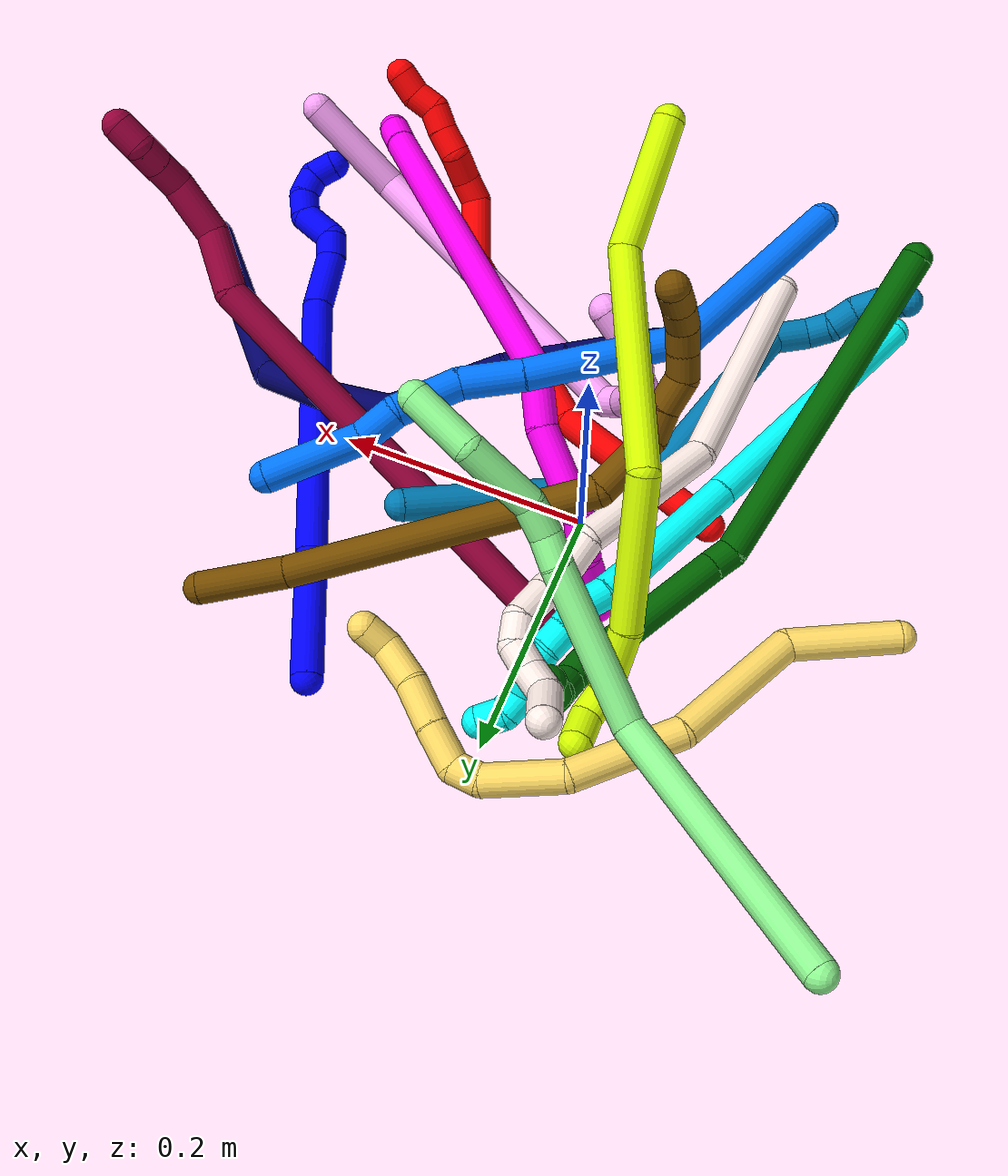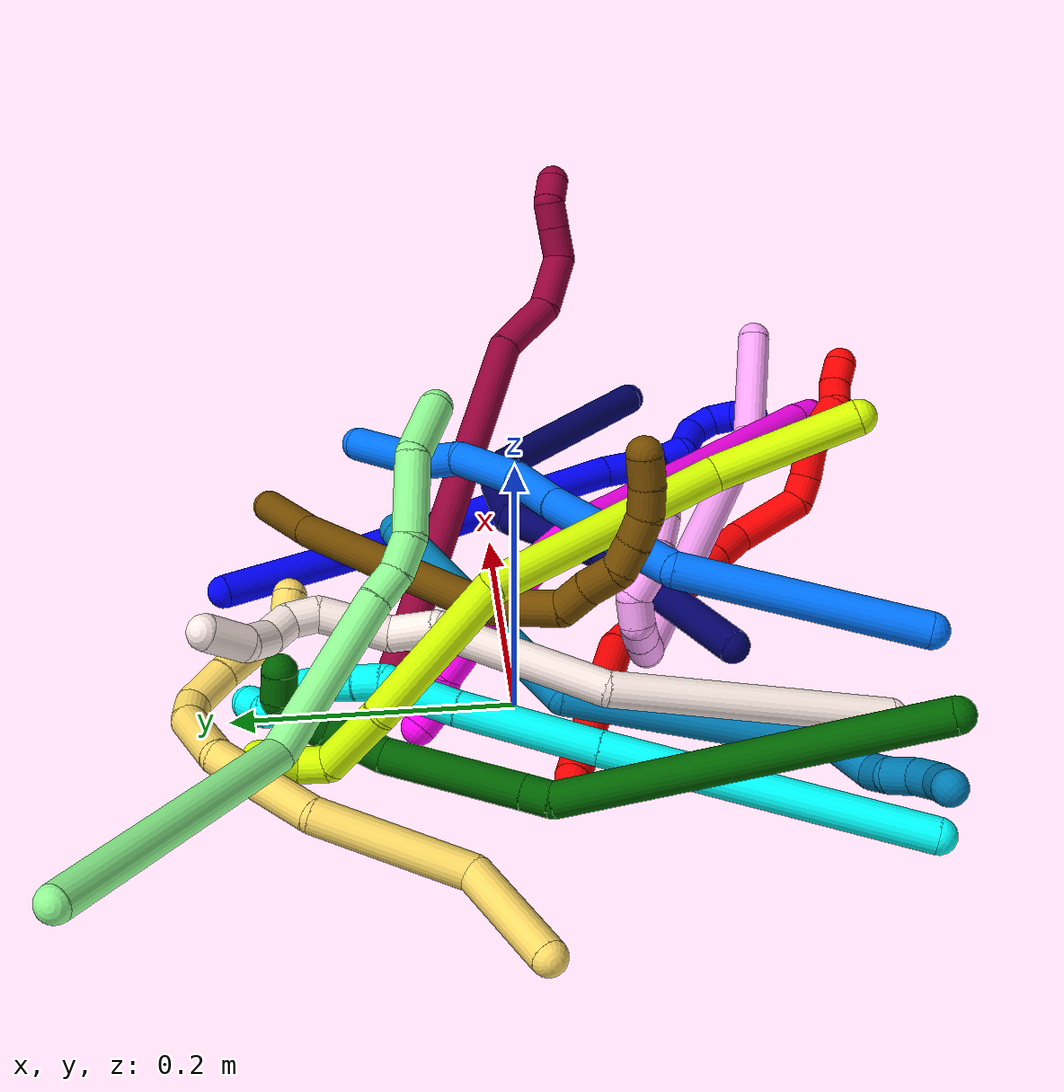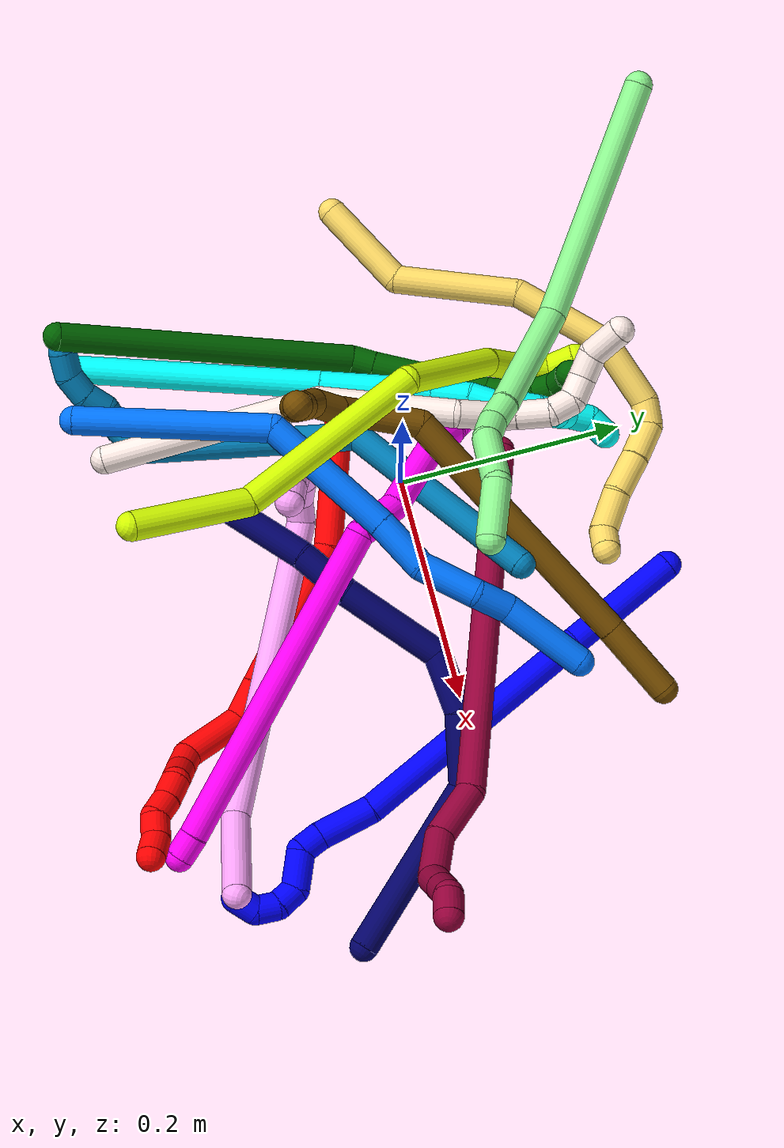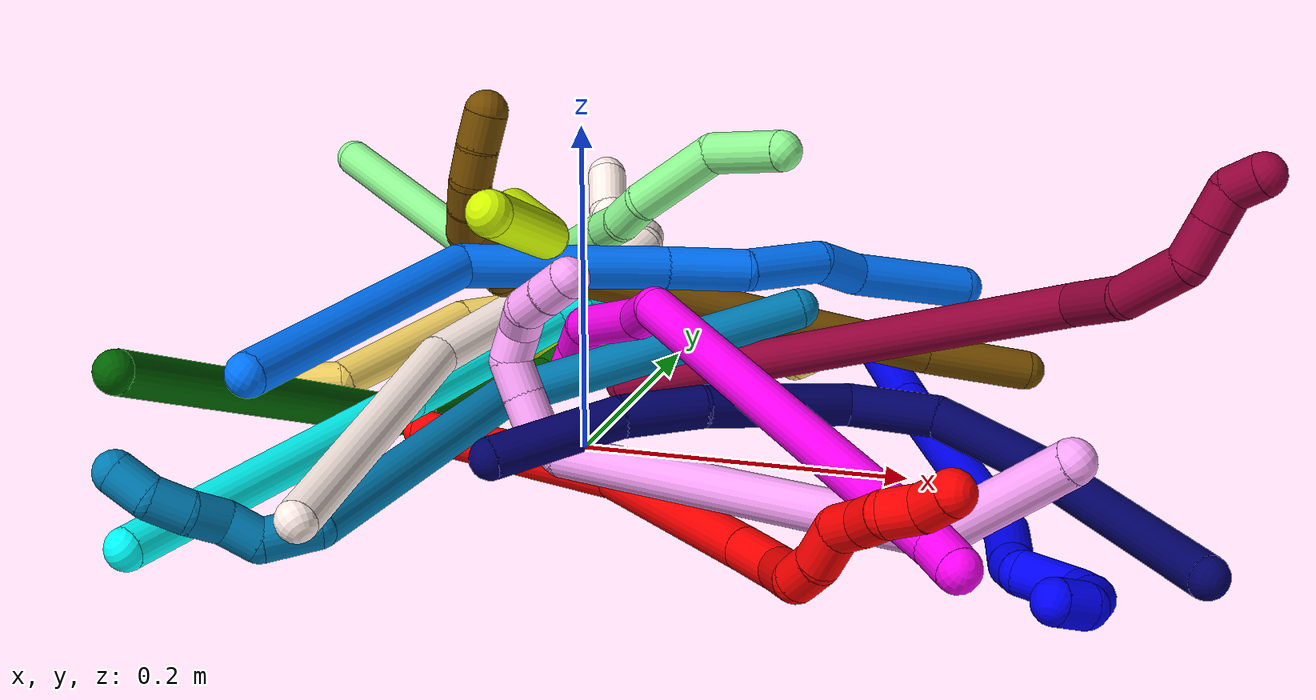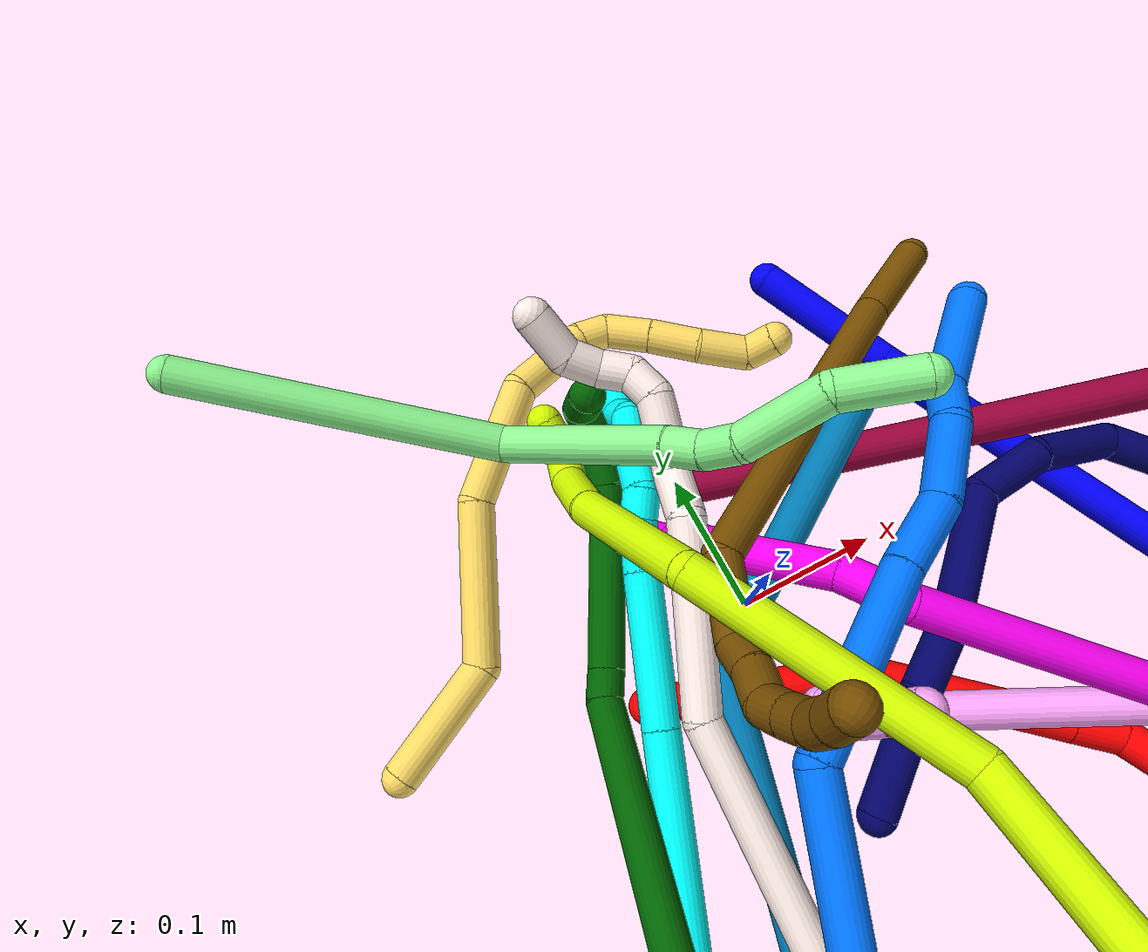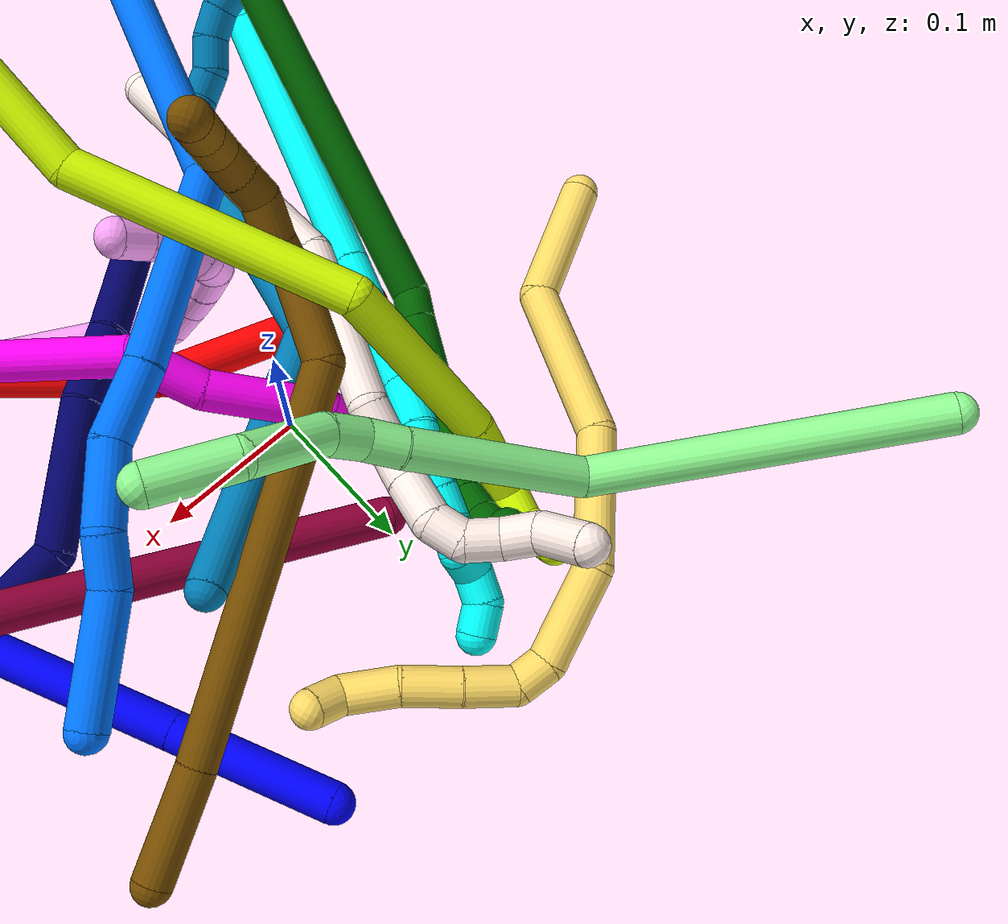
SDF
<sdf version="1.7">
 <world name="default">
  <plugin name="TubeGeneratorPlugin" filename="libtube_generator_plugin.so"/>
  <model name="photoneo_s_sensor">
   <static>1</static>
   <pose>0 0 2 1.57079 1.57079 3.14159</pose>
   <link name="link">
    <inertial><mass>0.1</mass></inertial>
    <sensor name="sensor" type="depth">
     <update_rate>30</update_rate>
     <camera>
      <horizontal_fov>1.22</horizontal_fov>
      <image><width>1920</width><height>1200</height><format>B8G8R8</format></image>
      <clip><near>0.1</near><far>4</far></clip>
      <depth_camera><output>points</output></depth_camera>
     </camera>
     <plugin name="camera_plugin" filename="libgazebo_ros_depth_camera.so">
      <baseline>0.2</baseline>
      <alwaysOn>1</alwaysOn>
      <updateRate>0.0</updateRate>
      <cameraName>camera_ir</cameraName>
      <imageTopicName>/camera/color/image_raw</imageTopicName>
      <cameraInfoTopicName>/camera/color/camera_info</cameraInfoTopicName>
      <depthImageTopicName>/camera/depth/image_raw</depthImageTopicName>
      <depthImageCameraInfoTopicName>/camera/depth/camera_info</depthImageCameraInfoTopicName>
      <pointCloudTopicName>/camera/depth/points</pointCloudTopicName>
      <frameName>fr_optical</frameName>
      <pointCloudCutoff>0.1</pointCloudCutoff>
      <pointCloudCutoffMax>2.0</pointCloudCutoffMax>
      <distortionK1>0</distortionK1>
      <distortionK2>0</distortionK2>
      <distortionK3>0</distortionK3>
      <distortionT1>0</distortionT1>
      <distortionT2>0</distortionT2>
      <CxPrime>0</CxPrime>
      <Cx>0</Cx>
      <Cy>0</Cy>
      <focalLength>0</focalLength>
      <hackBaseline>0</hackBaseline>
     </plugin>
    </sensor>
   </link>
  </model>
  <gravity>0 0 -9.8</gravity>
  <magnetic_field>6e-06 2.3e-05 -4.2e-05</magnetic_field>
  <atmosphere type="adiabatic"/>
  <physics name="default_physics" default="0" type="ode">
   <max_step_size>0.003</max_step_size>
   <real_time_factor>1</real_time_factor>
   <real_time_update_rate>1000</real_time_update_rate>
   <max_contacts>10000</max_contacts>
   <ode>
    <solver>
     <type>quick</type>
     <iters>100</iters>
     <sor>1.3</sor>
     <use_dynamic_moi_rescaling>0</use_dynamic_moi_rescaling>
    </solver>
    <constraints>
     <contact_max_correcting_vel>0</contact_max_correcting_vel>
     <contact_surface_layer>0.001</contact_surface_layer>
     <cfm>0</cfm>
     <erp>0.2</erp>
    </constraints>
   </ode>
  </physics>
  <scene><ambient>0.4 0.4 0.4 1</ambient><background>0.7 0.7 0.7 1</background><shadows>0</shadows></scene>
  <audio><device>default</device></audio>
  <spherical_coordinates>
   <surface_model>EARTH_WGS84</surface_model>
   <latitude_deg>0</latitude_deg>
   <longitude_deg>0</longitude_deg>
   <elevation>0</elevation>
   <heading_deg>0</heading_deg>
  </spherical_coordinates>
  <model name="bin">
   <static>1</static>
   <link name="bottom">
    <collision name="collision-bottom">
     <pose>0 0 -0.01 0 -0 0</pose>
     <geometry><box><size>0.8 0.6 0.02</size></box></geometry>
     <surface>
      <friction><ode><mu>100</mu><mu2>100</mu2></ode></friction>
      <contact><collide_bitmask>65535</collide_bitmask></contact>
     </surface>
    </collision>
   </link>
   <link name="west_wall">
    <collision name="collision-west_wall">
     <pose>-0.41 0 0.1 0 -0 0</pose>
     <geometry><box><size>0.02 0.6 0.2</size></box></geometry>
     <surface>
      <friction><ode><mu>100</mu><mu2>100</mu2></ode></friction>
      <contact><collide_bitmask>65535</collide_bitmask></contact>
     </surface>
    </collision>
   </link>
   <link name="east_wall">
    <collision name="collision-east_wall">
     <pose>0.41 0 0.1 0 -0 0</pose>
     <geometry><box><size>0.02 0.6 0.2</size></box></geometry>
     <surface>
      <friction><ode><mu>100</mu><mu2>100</mu2></ode></friction>
      <contact><collide_bitmask>65535</collide_bitmask></contact>
     </surface>
    </collision>
   </link>
   <link name="south_wall">
    <collision name="collision-south_wall">
     <pose>0 -0.31 0.1 0 -0 0</pose>
     <geometry><box><size>0.8 0.02 0.2</size></box></geometry>
     <surface>
      <friction><ode><mu>100</mu><mu2>100</mu2></ode></friction>
      <contact><collide_bitmask>65535</collide_bitmask></contact>
     </surface>
    </collision>
   </link>
   <link name="north_wall">
    <collision name="collision-north_wall">
     <pose>0 0.31 0.1 0 -0 0</pose>
     <geometry><box><size>0.8 0.02 0.2</size></box></geometry>
     <surface>
      <friction><ode><mu>100</mu><mu2>100</mu2></ode></friction>
      <contact><collide_bitmask>65535</collide_bitmask></contact>
     </surface>
    </collision>
   </link>
  </model>
  <model name="1">
   <static>0</static>
   <link name="1">
    <collision name="collision-cylinder-e_1_1_4">
     <pose>0.00842 -0.032595 0.040472 0.678008 0.160638 0.05675</pose>
     <geometry><cylinder><radius>0.0125</radius><length>0.105286</length></cylinder></geometry>
     <surface>
      <friction><ode><mu>1.16</mu><mu2>1.16</mu2><slip1>0</slip1><slip2>0</slip2></ode></friction>
      <contact><ode><kp>1e+06</kp><kd>1</kd><max_vel>0</max_vel><min_depth>0.001</min_depth></ode></contact>
     </surface>
    </collision>
    <visual name="visual-cylinder-e_1_1_4">
     <pose>0.00842 -0.032595 0.040472 0.678008 0.160638 0.05675</pose>
     <geometry><cylinder><radius>0.0125</radius><length>0.105286</length></cylinder></geometry>
     <material><ambient>0 0 1 1</ambient></material>
    </visual>
    <collision name="collision-cylinder-e_2_4_5">
     <pose>0.038405 -0.138295 0.167012 0.704136 0.188689 0.069498</pose>
     <geometry><cylinder><radius>0.0125</radius><length>0.229933</length></cylinder></geometry>
     <surface>
      <friction><ode><mu>1.16</mu><mu2>1.16</mu2><slip1>0</slip1><slip2>0</slip2></ode></friction>
      <contact><ode><kp>1e+06</kp><kd>1</kd><max_vel>0</max_vel><min_depth>0.001</min_depth></ode></contact>
     </surface>
    </collision>
    <visual name="visual-cylinder-e_2_4_5">
     <pose>0.038405 -0.138295 0.167012 0.704136 0.188689 0.069498</pose>
     <geometry><cylinder><radius>0.0125</radius><length>0.229933</length></cylinder></geometry>
     <material><ambient>0 0 1 1</ambient></material>
    </visual>
    <collision name="collision-cylinder-e_3_5_6">
     <pose>0.067471 -0.223268 0.273699 0.522296 0.305482 0.082235</pose>
     <geometry><cylinder><radius>0.0125</radius><length>0.049887</length></cylinder></geometry>
     <surface>
      <friction><ode><mu>1.16</mu><mu2>1.16</mu2><slip1>0</slip1><slip2>0</slip2></ode></friction>
      <contact><ode><kp>1e+06</kp><kd>1</kd><max_vel>0</max_vel><min_depth>0.001</min_depth></ode></contact>
     </surface>
    </collision>
    <visual name="visual-cylinder-e_3_5_6">
     <pose>0.067471 -0.223268 0.273699 0.522296 0.305482 0.082235</pose>
     <geometry><cylinder><radius>0.0125</radius><length>0.049887</length></cylinder></geometry>
     <material><ambient>0 0 1 1</ambient></material>
    </visual>
    <collision name="collision-cylinder-e_4_6_7">
     <pose>0.078415 -0.242066 0.301264 0.784094 0.337351 0.140584</pose>
     <geometry><cylinder><radius>0.0125</radius><length>0.0208</length></cylinder></geometry>
     <surface>
      <friction><ode><mu>1.16</mu><mu2>1.16</mu2><slip1>0</slip1><slip2>0</slip2></ode></friction>
      <contact><ode><kp>1e+06</kp><kd>1</kd><max_vel>0</max_vel><min_depth>0.001</min_depth></ode></contact>
     </surface>
    </collision>
    <visual name="visual-cylinder-e_4_6_7">
     <pose>0.078415 -0.242066 0.301264 0.784094 0.337351 0.140584</pose>
     <geometry><cylinder><radius>0.0125</radius><length>0.0208</length></cylinder></geometry>
     <material><ambient>0 0 1 1</ambient></material>
    </visual>
    <collision name="collision-cylinder-e_5_7_8">
     <pose>0.077604 -0.264694 0.31262 1.29707 -0.255186 -0.193851</pose>
     <geometry><cylinder><radius>0.0125</radius><length>0.0337</length></cylinder></geometry>
     <surface>
      <friction><ode><mu>1.16</mu><mu2>1.16</mu2><slip1>0</slip1><slip2>0</slip2></ode></friction>
      <contact><ode><kp>1e+06</kp><kd>1</kd><max_vel>0</max_vel><min_depth>0.001</min_depth></ode></contact>
     </surface>
    </collision>
    <visual name="visual-cylinder-e_5_7_8">
     <pose>0.077604 -0.264694 0.31262 1.29707 -0.255186 -0.193851</pose>
     <geometry><cylinder><radius>0.0125</radius><length>0.0337</length></cylinder></geometry>
     <material><ambient>0 0 1 1</ambient></material>
    </visual>
    <collision name="collision-cylinder-e_6_8_9">
     <pose>0.076498 -0.287865 0.323156 0.884018 0.314789 0.149931</pose>
     <geometry><cylinder><radius>0.0125</radius><length>0.02033</length></cylinder></geometry>
     <surface>
      <friction><ode><mu>1.16</mu><mu2>1.16</mu2><slip1>0</slip1><slip2>0</slip2></ode></friction>
      <contact><ode><kp>1e+06</kp><kd>1</kd><max_vel>0</max_vel><min_depth>0.001</min_depth></ode></contact>
     </surface>
    </collision>
    <visual name="visual-cylinder-e_6_8_9">
     <pose>0.076498 -0.287865 0.323156 0.884018 0.314789 0.149931</pose>
     <geometry><cylinder><radius>0.0125</radius><length>0.02033</length></cylinder></geometry>
     <material><ambient>0 0 1 1</ambient></material>
    </visual>
    <collision name="collision-cylinder-e_7_9_10">
     <pose>0.085223 -0.29841 0.337032 0.377341 0.589817 0.115873</pose>
     <geometry><cylinder><radius>0.0125</radius><length>0.020057</length></cylinder></geometry>
     <surface>
      <friction><ode><mu>1.16</mu><mu2>1.16</mu2><slip1>0</slip1><slip2>0</slip2></ode></friction>
      <contact><ode><kp>1e+06</kp><kd>1</kd><max_vel>0</max_vel><min_depth>0.001</min_depth></ode></contact>
     </surface>
    </collision>
    <visual name="visual-cylinder-e_7_9_10">
     <pose>0.085223 -0.29841 0.337032 0.377341 0.589817 0.115873</pose>
     <geometry><cylinder><radius>0.0125</radius><length>0.020057</length></cylinder></geometry>
     <material><ambient>0 0 1 1</ambient></material>
    </visual>
    <collision name="collision-cylinder-e_8_10_2">
     <pose>0.098576 -0.298027 0.350043 -0.580836 0.890154 -0.283211</pose>
     <geometry><cylinder><radius>0.0125</radius><length>0.020007</length></cylinder></geometry>
     <surface>
      <friction><ode><mu>1.16</mu><mu2>1.16</mu2><slip1>0</slip1><slip2>0</slip2></ode></friction>
      <contact><ode><kp>1e+06</kp><kd>1</kd><max_vel>0</max_vel><min_depth>0.001</min_depth></ode></contact>
     </surface>
    </collision>
    <visual name="visual-cylinder-e_8_10_2">
     <pose>0.098576 -0.298027 0.350043 -0.580836 0.890154 -0.283211</pose>
     <geometry><cylinder><radius>0.0125</radius><length>0.020007</length></cylinder></geometry>
     <material><ambient>0 0 1 1</ambient></material>
    </visual>
    <collision name="collision-sphere-2">
     <pose>0.10635 -0.294572 0.355305 0 -0 0</pose>
     <geometry><sphere><radius>0.0125</radius></sphere></geometry>
     <surface>
      <friction><ode><mu>1.16</mu><mu2>1.16</mu2><slip1>0</slip1><slip2>0</slip2></ode></friction>
      <contact><ode><kp>1e+06</kp><kd>1</kd><max_vel>0</max_vel><min_depth>0.001</min_depth></ode></contact>
     </surface>
    </collision>
    <visual name="visual-sphere-2">
     <pose>0.10635 -0.294572 0.355305 0 -0 0</pose>
     <geometry><sphere><radius>0.0125</radius></sphere></geometry>
     <material><ambient>0 0 1 1</ambient></material>
    </visual>
    <collision name="collision-sphere-10">
     <pose>0.090801 -0.301481 0.34478 0 -0 0</pose>
     <geometry><sphere><radius>0.0125</radius></sphere></geometry>
     <surface>
      <friction><ode><mu>1.16</mu><mu2>1.16</mu2><slip1>0</slip1><slip2>0</slip2></ode></friction>
      <contact><ode><kp>1e+06</kp><kd>1</kd><max_vel>0</max_vel><min_depth>0.001</min_depth></ode></contact>
     </surface>
    </collision>
    <visual name="visual-sphere-10">
     <pose>0.090801 -0.301481 0.34478 0 -0 0</pose>
     <geometry><sphere><radius>0.0125</radius></sphere></geometry>
     <material><ambient>0 0 1 1</ambient></material>
    </visual>
    <collision name="collision-sphere-9">
     <pose>0.079645 -0.29534 0.329285 0 -0 0</pose>
     <geometry><sphere><radius>0.0125</radius></sphere></geometry>
     <surface>
      <friction><ode><mu>1.16</mu><mu2>1.16</mu2><slip1>0</slip1><slip2>0</slip2></ode></friction>
      <contact><ode><kp>1e+06</kp><kd>1</kd><max_vel>0</max_vel><min_depth>0.001</min_depth></ode></contact>
     </surface>
    </collision>
    <visual name="visual-sphere-9">
     <pose>0.079645 -0.29534 0.329285 0 -0 0</pose>
     <geometry><sphere><radius>0.0125</radius></sphere></geometry>
     <material><ambient>0 0 1 1</ambient></material>
    </visual>
    <collision name="collision-sphere-4">
     <pose>0.01684 -0.06519 0.080943 0 -0 0</pose>
     <geometry><sphere><radius>0.0125</radius></sphere></geometry>
     <surface>
      <friction><ode><mu>1.16</mu><mu2>1.16</mu2><slip1>0</slip1><slip2>0</slip2></ode></friction>
      <contact><ode><kp>1e+06</kp><kd>1</kd><max_vel>0</max_vel><min_depth>0.001</min_depth></ode></contact>
     </surface>
    </collision>
    <visual name="visual-sphere-4">
     <pose>0.01684 -0.06519 0.080943 0 -0 0</pose>
     <geometry><sphere><radius>0.0125</radius></sphere></geometry>
     <material><ambient>0 0 1 1</ambient></material>
    </visual>
    <collision name="collision-sphere-1">
     <geometry><sphere><radius>0.0125</radius></sphere></geometry>
     <surface>
      <friction><ode><mu>1.16</mu><mu2>1.16</mu2><slip1>0</slip1><slip2>0</slip2></ode></friction>
      <contact><ode><kp>1e+06</kp><kd>1</kd><max_vel>0</max_vel><min_depth>0.001</min_depth></ode></contact>
     </surface>
    </collision>
    <visual name="visual-sphere-1">
     <geometry><sphere><radius>0.0125</radius></sphere></geometry>
     <material><ambient>0 0 1 1</ambient></material>
    </visual>
    <collision name="collision-sphere-8">
     <pose>0.073351 -0.280391 0.317028 0 -0 0</pose>
     <geometry><sphere><radius>0.0125</radius></sphere></geometry>
     <surface>
      <friction><ode><mu>1.16</mu><mu2>1.16</mu2><slip1>0</slip1><slip2>0</slip2></ode></friction>
      <contact><ode><kp>1e+06</kp><kd>1</kd><max_vel>0</max_vel><min_depth>0.001</min_depth></ode></contact>
     </surface>
    </collision>
    <visual name="visual-sphere-8">
     <pose>0.073351 -0.280391 0.317028 0 -0 0</pose>
     <geometry><sphere><radius>0.0125</radius></sphere></geometry>
     <material><ambient>0 0 1 1</ambient></material>
    </visual>
    <collision name="collision-sphere-5">
     <pose>0.059969 -0.211401 0.253081 0 -0 0</pose>
     <geometry><sphere><radius>0.0125</radius></sphere></geometry>
     <surface>
      <friction><ode><mu>1.16</mu><mu2>1.16</mu2><slip1>0</slip1><slip2>0</slip2></ode></friction>
      <contact><ode><kp>1e+06</kp><kd>1</kd><max_vel>0</max_vel><min_depth>0.001</min_depth></ode></contact>
     </surface>
    </collision>
    <visual name="visual-sphere-5">
     <pose>0.059969 -0.211401 0.253081 0 -0 0</pose>
     <geometry><sphere><radius>0.0125</radius></sphere></geometry>
     <material><ambient>0 0 1 1</ambient></material>
    </visual>
    <collision name="collision-sphere-6">
     <pose>0.074973 -0.235136 0.294316 0 -0 0</pose>
     <geometry><sphere><radius>0.0125</radius></sphere></geometry>
     <surface>
      <friction><ode><mu>1.16</mu><mu2>1.16</mu2><slip1>0</slip1><slip2>0</slip2></ode></friction>
      <contact><ode><kp>1e+06</kp><kd>1</kd><max_vel>0</max_vel><min_depth>0.001</min_depth></ode></contact>
     </surface>
    </collision>
    <visual name="visual-sphere-6">
     <pose>0.074973 -0.235136 0.294316 0 -0 0</pose>
     <geometry><sphere><radius>0.0125</radius></sphere></geometry>
     <material><ambient>0 0 1 1</ambient></material>
    </visual>
    <collision name="collision-sphere-7">
     <pose>0.081858 -0.248997 0.308213 0 -0 0</pose>
     <geometry><sphere><radius>0.0125</radius></sphere></geometry>
     <surface>
      <friction><ode><mu>1.16</mu><mu2>1.16</mu2><slip1>0</slip1><slip2>0</slip2></ode></friction>
      <contact><ode><kp>1e+06</kp><kd>1</kd><max_vel>0</max_vel><min_depth>0.001</min_depth></ode></contact>
     </surface>
    </collision>
    <visual name="visual-sphere-7">
     <pose>0.081858 -0.248997 0.308213 0 -0 0</pose>
     <geometry><sphere><radius>0.0125</radius></sphere></geometry>
     <material><ambient>0 0 1 1</ambient></material>
    </visual>
    <inertial>
     <pose>0.045132 -0.156248 0.186903 0 -0 0</pose>
     <mass>0.5</mass>
     <inertia>
      <ixx>0.001206</ixx>
      <ixy>0</ixy>
      <ixz>0</ixz>
      <iyy>0.000935</iyy>
      <iyz>0</iyz>
      <izz>0.000539</izz>
     </inertia>
    </inertial>
   </link>
   <pose>0.135492 0.204401 0.015534 -2.56899 -0.98763 -2.35992</pose>
  </model>
  <model name="2">
   <static>0</static>
   <link name="2">
    <collision name="collision-cylinder-e_1_1_4">
     <pose>0.017081 -0.0007 0.070695 0.009907 0.237054 0.00118</pose>
     <geometry><cylinder><radius>0.0125</radius><length>0.145466</length></cylinder></geometry>
     <surface>
      <friction><ode><mu>1.16</mu><mu2>1.16</mu2><slip1>0</slip1><slip2>0</slip2></ode></friction>
      <contact><ode><kp>1e+06</kp><kd>1</kd><max_vel>0</max_vel><min_depth>0.001</min_depth></ode></contact>
     </surface>
    </collision>
    <visual name="visual-cylinder-e_1_1_4">
     <pose>0.017081 -0.0007 0.070695 0.009907 0.237054 0.00118</pose>
     <geometry><cylinder><radius>0.0125</radius><length>0.145466</length></cylinder></geometry>
     <material><ambient>1 0 0 1</ambient></material>
    </visual>
    <collision name="collision-cylinder-e_2_4_5">
     <pose>0.050827 -0.027881 0.202049 0.411603 0.246675 0.051746</pose>
     <geometry><cylinder><radius>0.0125</radius><length>0.136505</length></cylinder></geometry>
     <surface>
      <friction><ode><mu>1.16</mu><mu2>1.16</mu2><slip1>0</slip1><slip2>0</slip2></ode></friction>
      <contact><ode><kp>1e+06</kp><kd>1</kd><max_vel>0</max_vel><min_depth>0.001</min_depth></ode></contact>
     </surface>
    </collision>
    <visual name="visual-cylinder-e_2_4_5">
     <pose>0.050827 -0.027881 0.202049 0.411603 0.246675 0.051746</pose>
     <geometry><cylinder><radius>0.0125</radius><length>0.136505</length></cylinder></geometry>
     <material><ambient>1 0 0 1</ambient></material>
    </visual>
    <collision name="collision-cylinder-e_3_5_6">
     <pose>0.072092 -0.060858 0.277934 0.403345 0.270946 0.055722</pose>
     <geometry><cylinder><radius>0.0125</radius><length>0.034363</length></cylinder></geometry>
     <surface>
      <friction><ode><mu>1.16</mu><mu2>1.16</mu2><slip1>0</slip1><slip2>0</slip2></ode></friction>
      <contact><ode><kp>1e+06</kp><kd>1</kd><max_vel>0</max_vel><min_depth>0.001</min_depth></ode></contact>
     </surface>
    </collision>
    <visual name="visual-cylinder-e_3_5_6">
     <pose>0.072092 -0.060858 0.277934 0.403345 0.270946 0.055722</pose>
     <geometry><cylinder><radius>0.0125</radius><length>0.034363</length></cylinder></geometry>
     <material><ambient>1 0 0 1</ambient></material>
    </visual>
    <collision name="collision-cylinder-e_4_6_7">
     <pose>0.075146 -0.088302 0.311835 0.842677 -0.054969 -0.024641</pose>
     <geometry><cylinder><radius>0.0125</radius><length>0.056209</length></cylinder></geometry>
     <surface>
      <friction><ode><mu>1.16</mu><mu2>1.16</mu2><slip1>0</slip1><slip2>0</slip2></ode></friction>
      <contact><ode><kp>1e+06</kp><kd>1</kd><max_vel>0</max_vel><min_depth>0.001</min_depth></ode></contact>
     </surface>
    </collision>
    <visual name="visual-cylinder-e_4_6_7">
     <pose>0.075146 -0.088302 0.311835 0.842677 -0.054969 -0.024641</pose>
     <geometry><cylinder><radius>0.0125</radius><length>0.056209</length></cylinder></geometry>
     <material><ambient>1 0 0 1</ambient></material>
    </visual>
    <collision name="collision-cylinder-e_5_7_8">
     <pose>0.068822 -0.111784 0.33939 0.278114 -0.477591 -0.068118</pose>
     <geometry><cylinder><radius>0.0125</radius><length>0.020798</length></cylinder></geometry>
     <surface>
      <friction><ode><mu>1.16</mu><mu2>1.16</mu2><slip1>0</slip1><slip2>0</slip2></ode></friction>
      <contact><ode><kp>1e+06</kp><kd>1</kd><max_vel>0</max_vel><min_depth>0.001</min_depth></ode></contact>
     </surface>
    </collision>
    <visual name="visual-cylinder-e_5_7_8">
     <pose>0.068822 -0.111784 0.33939 0.278114 -0.477591 -0.068118</pose>
     <geometry><cylinder><radius>0.0125</radius><length>0.020798</length></cylinder></geometry>
     <material><ambient>1 0 0 1</ambient></material>
    </visual>
    <collision name="collision-cylinder-e_6_8_9">
     <pose>0.055403 -0.116249 0.35684 0.221501 -0.777041 -0.090976</pose>
     <geometry><cylinder><radius>0.0125</radius><length>0.024641</length></cylinder></geometry>
     <surface>
      <friction><ode><mu>1.16</mu><mu2>1.16</mu2><slip1>0</slip1><slip2>0</slip2></ode></friction>
      <contact><ode><kp>1e+06</kp><kd>1</kd><max_vel>0</max_vel><min_depth>0.001</min_depth></ode></contact>
     </surface>
    </collision>
    <visual name="visual-cylinder-e_6_8_9">
     <pose>0.055403 -0.116249 0.35684 0.221501 -0.777041 -0.090976</pose>
     <geometry><cylinder><radius>0.0125</radius><length>0.024641</length></cylinder></geometry>
     <material><ambient>1 0 0 1</ambient></material>
    </visual>
    <collision name="collision-cylinder-e_7_9_10">
     <pose>0.044697 -0.121491 0.37547 0.31801 -0.19276 -0.031004</pose>
     <geometry><cylinder><radius>0.0125</radius><length>0.021581</length></cylinder></geometry>
     <surface>
      <friction><ode><mu>1.16</mu><mu2>1.16</mu2><slip1>0</slip1><slip2>0</slip2></ode></friction>
      <contact><ode><kp>1e+06</kp><kd>1</kd><max_vel>0</max_vel><min_depth>0.001</min_depth></ode></contact>
     </surface>
    </collision>
    <visual name="visual-cylinder-e_7_9_10">
     <pose>0.044697 -0.121491 0.37547 0.31801 -0.19276 -0.031004</pose>
     <geometry><cylinder><radius>0.0125</radius><length>0.021581</length></cylinder></geometry>
     <material><ambient>1 0 0 1</ambient></material>
    </visual>
    <collision name="collision-cylinder-e_8_10_11">
     <pose>0.040068 -0.129063 0.394318 0.451461 -0.256557 -0.059225</pose>
     <geometry><cylinder><radius>0.0125</radius><length>0.020194</length></cylinder></geometry>
     <surface>
      <friction><ode><mu>1.16</mu><mu2>1.16</mu2><slip1>0</slip1><slip2>0</slip2></ode></friction>
      <contact><ode><kp>1e+06</kp><kd>1</kd><max_vel>0</max_vel><min_depth>0.001</min_depth></ode></contact>
     </surface>
    </collision>
    <visual name="visual-cylinder-e_8_10_11">
     <pose>0.040068 -0.129063 0.394318 0.451461 -0.256557 -0.059225</pose>
     <geometry><cylinder><radius>0.0125</radius><length>0.020194</length></cylinder></geometry>
     <material><ambient>1 0 0 1</ambient></material>
    </visual>
    <collision name="collision-cylinder-e_9_11_12">
     <pose>0.03654 -0.132131 0.412994 -0.120107 -0.09667 0.005817</pose>
     <geometry><cylinder><radius>0.0125</radius><length>0.020013</length></cylinder></geometry>
     <surface>
      <friction><ode><mu>1.16</mu><mu2>1.16</mu2><slip1>0</slip1><slip2>0</slip2></ode></friction>
      <contact><ode><kp>1e+06</kp><kd>1</kd><max_vel>0</max_vel><min_depth>0.001</min_depth></ode></contact>
     </surface>
    </collision>
    <visual name="visual-cylinder-e_9_11_12">
     <pose>0.03654 -0.132131 0.412994 -0.120107 -0.09667 0.005817</pose>
     <geometry><cylinder><radius>0.0125</radius><length>0.020013</length></cylinder></geometry>
     <material><ambient>1 0 0 1</ambient></material>
    </visual>
    <collision name="collision-cylinder-e_10_12_2">
     <pose>0.032032 -0.132432 0.432237 0.158381 -0.35781 -0.028699</pose>
     <geometry><cylinder><radius>0.0125</radius><length>0.020229</length></cylinder></geometry>
     <surface>
      <friction><ode><mu>1.16</mu><mu2>1.16</mu2><slip1>0</slip1><slip2>0</slip2></ode></friction>
      <contact><ode><kp>1e+06</kp><kd>1</kd><max_vel>0</max_vel><min_depth>0.001</min_depth></ode></contact>
     </surface>
    </collision>
    <visual name="visual-cylinder-e_10_12_2">
     <pose>0.032032 -0.132432 0.432237 0.158381 -0.35781 -0.028699</pose>
     <geometry><cylinder><radius>0.0125</radius><length>0.020229</length></cylinder></geometry>
     <material><ambient>1 0 0 1</ambient></material>
    </visual>
    <collision name="collision-sphere-2">
     <pose>0.028489 -0.133926 0.441593 0 -0 0</pose>
     <geometry><sphere><radius>0.0125</radius></sphere></geometry>
     <surface>
      <friction><ode><mu>1.16</mu><mu2>1.16</mu2><slip1>0</slip1><slip2>0</slip2></ode></friction>
      <contact><ode><kp>1e+06</kp><kd>1</kd><max_vel>0</max_vel><min_depth>0.001</min_depth></ode></contact>
     </surface>
    </collision>
    <visual name="visual-sphere-2">
     <pose>0.028489 -0.133926 0.441593 0 -0 0</pose>
     <geometry><sphere><radius>0.0125</radius></sphere></geometry>
     <material><ambient>1 0 0 1</ambient></material>
    </visual>
    <collision name="collision-sphere-12">
     <pose>0.035574 -0.130938 0.422882 0 -0 0</pose>
     <geometry><sphere><radius>0.0125</radius></sphere></geometry>
     <surface>
      <friction><ode><mu>1.16</mu><mu2>1.16</mu2><slip1>0</slip1><slip2>0</slip2></ode></friction>
      <contact><ode><kp>1e+06</kp><kd>1</kd><max_vel>0</max_vel><min_depth>0.001</min_depth></ode></contact>
     </surface>
    </collision>
    <visual name="visual-sphere-12">
     <pose>0.035574 -0.130938 0.422882 0 -0 0</pose>
     <geometry><sphere><radius>0.0125</radius></sphere></geometry>
     <material><ambient>1 0 0 1</ambient></material>
    </visual>
    <collision name="collision-sphere-11">
     <pose>0.037506 -0.133324 0.403106 0 -0 0</pose>
     <geometry><sphere><radius>0.0125</radius></sphere></geometry>
     <surface>
      <friction><ode><mu>1.16</mu><mu2>1.16</mu2><slip1>0</slip1><slip2>0</slip2></ode></friction>
      <contact><ode><kp>1e+06</kp><kd>1</kd><max_vel>0</max_vel><min_depth>0.001</min_depth></ode></contact>
     </surface>
    </collision>
    <visual name="visual-sphere-11">
     <pose>0.037506 -0.133324 0.403106 0 -0 0</pose>
     <geometry><sphere><radius>0.0125</radius></sphere></geometry>
     <material><ambient>1 0 0 1</ambient></material>
    </visual>
    <collision name="collision-sphere-10">
     <pose>0.04263 -0.124802 0.38553 0 -0 0</pose>
     <geometry><sphere><radius>0.0125</radius></sphere></geometry>
     <surface>
      <friction><ode><mu>1.16</mu><mu2>1.16</mu2><slip1>0</slip1><slip2>0</slip2></ode></friction>
      <contact><ode><kp>1e+06</kp><kd>1</kd><max_vel>0</max_vel><min_depth>0.001</min_depth></ode></contact>
     </surface>
    </collision>
    <visual name="visual-sphere-10">
     <pose>0.04263 -0.124802 0.38553 0 -0 0</pose>
     <geometry><sphere><radius>0.0125</radius></sphere></geometry>
     <material><ambient>1 0 0 1</ambient></material>
    </visual>
    <collision name="collision-sphere-9">
     <pose>0.046764 -0.118179 0.36541 0 -0 0</pose>
     <geometry><sphere><radius>0.0125</radius></sphere></geometry>
     <surface>
      <friction><ode><mu>1.16</mu><mu2>1.16</mu2><slip1>0</slip1><slip2>0</slip2></ode></friction>
      <contact><ode><kp>1e+06</kp><kd>1</kd><max_vel>0</max_vel><min_depth>0.001</min_depth></ode></contact>
     </surface>
    </collision>
    <visual name="visual-sphere-9">
     <pose>0.046764 -0.118179 0.36541 0 -0 0</pose>
     <geometry><sphere><radius>0.0125</radius></sphere></geometry>
     <material><ambient>1 0 0 1</ambient></material>
    </visual>
    <collision name="collision-sphere-4">
     <pose>0.034161 -0.001401 0.14139 0 -0 0</pose>
     <geometry><sphere><radius>0.0125</radius></sphere></geometry>
     <surface>
      <friction><ode><mu>1.16</mu><mu2>1.16</mu2><slip1>0</slip1><slip2>0</slip2></ode></friction>
      <contact><ode><kp>1e+06</kp><kd>1</kd><max_vel>0</max_vel><min_depth>0.001</min_depth></ode></contact>
     </surface>
    </collision>
    <visual name="visual-sphere-4">
     <pose>0.034161 -0.001401 0.14139 0 -0 0</pose>
     <geometry><sphere><radius>0.0125</radius></sphere></geometry>
     <material><ambient>1 0 0 1</ambient></material>
    </visual>
    <collision name="collision-sphere-1">
     <geometry><sphere><radius>0.0125</radius></sphere></geometry>
     <surface>
      <friction><ode><mu>1.16</mu><mu2>1.16</mu2><slip1>0</slip1><slip2>0</slip2></ode></friction>
      <contact><ode><kp>1e+06</kp><kd>1</kd><max_vel>0</max_vel><min_depth>0.001</min_depth></ode></contact>
     </surface>
    </collision>
    <visual name="visual-sphere-1">
     <geometry><sphere><radius>0.0125</radius></sphere></geometry>
     <material><ambient>1 0 0 1</ambient></material>
    </visual>
    <collision name="collision-sphere-8">
     <pose>0.064042 -0.11432 0.348271 0 -0 0</pose>
     <geometry><sphere><radius>0.0125</radius></sphere></geometry>
     <surface>
      <friction><ode><mu>1.16</mu><mu2>1.16</mu2><slip1>0</slip1><slip2>0</slip2></ode></friction>
      <contact><ode><kp>1e+06</kp><kd>1</kd><max_vel>0</max_vel><min_depth>0.001</min_depth></ode></contact>
     </surface>
    </collision>
    <visual name="visual-sphere-8">
     <pose>0.064042 -0.11432 0.348271 0 -0 0</pose>
     <geometry><sphere><radius>0.0125</radius></sphere></geometry>
     <material><ambient>1 0 0 1</ambient></material>
    </visual>
    <collision name="collision-sphere-5">
     <pose>0.067493 -0.054361 0.262708 0 -0 0</pose>
     <geometry><sphere><radius>0.0125</radius></sphere></geometry>
     <surface>
      <friction><ode><mu>1.16</mu><mu2>1.16</mu2><slip1>0</slip1><slip2>0</slip2></ode></friction>
      <contact><ode><kp>1e+06</kp><kd>1</kd><max_vel>0</max_vel><min_depth>0.001</min_depth></ode></contact>
     </surface>
    </collision>
    <visual name="visual-sphere-5">
     <pose>0.067493 -0.054361 0.262708 0 -0 0</pose>
     <geometry><sphere><radius>0.0125</radius></sphere></geometry>
     <material><ambient>1 0 0 1</ambient></material>
    </visual>
    <collision name="collision-sphere-6">
     <pose>0.07669 -0.067356 0.29316 0 -0 0</pose>
     <geometry><sphere><radius>0.0125</radius></sphere></geometry>
     <surface>
      <friction><ode><mu>1.16</mu><mu2>1.16</mu2><slip1>0</slip1><slip2>0</slip2></ode></friction>
      <contact><ode><kp>1e+06</kp><kd>1</kd><max_vel>0</max_vel><min_depth>0.001</min_depth></ode></contact>
     </surface>
    </collision>
    <visual name="visual-sphere-6">
     <pose>0.07669 -0.067356 0.29316 0 -0 0</pose>
     <geometry><sphere><radius>0.0125</radius></sphere></geometry>
     <material><ambient>1 0 0 1</ambient></material>
    </visual>
    <collision name="collision-sphere-7">
     <pose>0.073602 -0.109248 0.330509 0 -0 0</pose>
     <geometry><sphere><radius>0.0125</radius></sphere></geometry>
     <surface>
      <friction><ode><mu>1.16</mu><mu2>1.16</mu2><slip1>0</slip1><slip2>0</slip2></ode></friction>
      <contact><ode><kp>1e+06</kp><kd>1</kd><max_vel>0</max_vel><min_depth>0.001</min_depth></ode></contact>
     </surface>
    </collision>
    <visual name="visual-sphere-7">
     <pose>0.073602 -0.109248 0.330509 0 -0 0</pose>
     <geometry><sphere><radius>0.0125</radius></sphere></geometry>
     <material><ambient>1 0 0 1</ambient></material>
    </visual>
    <inertial>
     <pose>0.044147 -0.053407 0.22774 0 -0 0</pose>
     <mass>0.5</mass>
     <inertia>
      <ixx>0.000509</ixx>
      <ixy>0</ixy>
      <ixz>0</ixz>
      <iyy>0.000488</iyy>
      <iyz>0</iyz>
      <izz>2.6e-05</izz>
     </inertia>
    </inertial>
   </link>
   <pose>-0.093564 -0.029596 0.011491 -0.417653 1.31339 -0.732692</pose>
  </model>
  <model name="3">
   <static>0</static>
   <link name="3">
    <collision name="collision-cylinder-e_1_1_4">
     <pose>0.027121 0.092461 -0.059635 -2.14363 0.241683 -0.43848</pose>
     <geometry><cylinder><radius>0.0125</radius><length>0.226637</length></cylinder></geometry>
     <surface>
      <friction><ode><mu>1.16</mu><mu2>1.16</mu2><slip1>0</slip1><slip2>0</slip2></ode></friction>
      <contact><ode><kp>1e+06</kp><kd>1</kd><max_vel>0</max_vel><min_depth>0.001</min_depth></ode></contact>
     </surface>
    </collision>
    <visual name="visual-cylinder-e_1_1_4">
     <pose>0.027121 0.092461 -0.059635 -2.14363 0.241683 -0.43848</pose>
     <geometry><cylinder><radius>0.0125</radius><length>0.226637</length></cylinder></geometry>
     <material><ambient>0.003922 1 0.996078 1</ambient></material>
    </visual>
    <collision name="collision-cylinder-e_2_4_5">
     <pose>0.066819 0.225521 -0.144763 -2.13149 0.25657 -0.458422</pose>
     <geometry><cylinder><radius>0.0125</radius><length>0.099121</length></cylinder></geometry>
     <surface>
      <friction><ode><mu>1.16</mu><mu2>1.16</mu2><slip1>0</slip1><slip2>0</slip2></ode></friction>
      <contact><ode><kp>1e+06</kp><kd>1</kd><max_vel>0</max_vel><min_depth>0.001</min_depth></ode></contact>
     </surface>
    </collision>
    <visual name="visual-cylinder-e_2_4_5">
     <pose>0.066819 0.225521 -0.144763 -2.13149 0.25657 -0.458422</pose>
     <geometry><cylinder><radius>0.0125</radius><length>0.099121</length></cylinder></geometry>
     <material><ambient>0.003922 1 0.996078 1</ambient></material>
    </visual>
    <collision name="collision-cylinder-e_3_5_6">
     <pose>0.084578 0.27975 -0.178401 -2.10943 0.315432 -0.546584</pose>
     <geometry><cylinder><radius>0.0125</radius><length>0.033407</length></cylinder></geometry>
     <surface>
      <friction><ode><mu>1.16</mu><mu2>1.16</mu2><slip1>0</slip1><slip2>0</slip2></ode></friction>
      <contact><ode><kp>1e+06</kp><kd>1</kd><max_vel>0</max_vel><min_depth>0.001</min_depth></ode></contact>
     </surface>
    </collision>
    <visual name="visual-cylinder-e_3_5_6">
     <pose>0.084578 0.27975 -0.178401 -2.10943 0.315432 -0.546584</pose>
     <geometry><cylinder><radius>0.0125</radius><length>0.033407</length></cylinder></geometry>
     <material><ambient>0.003922 1 0.996078 1</ambient></material>
    </visual>
    <collision name="collision-cylinder-e_4_6_7">
     <pose>0.094262 0.300587 -0.192546 -2.2651 0.447669 -0.90439</pose>
     <geometry><cylinder><radius>0.0125</radius><length>0.020802</length></cylinder></geometry>
     <surface>
      <friction><ode><mu>1.16</mu><mu2>1.16</mu2><slip1>0</slip1><slip2>0</slip2></ode></friction>
      <contact><ode><kp>1e+06</kp><kd>1</kd><max_vel>0</max_vel><min_depth>0.001</min_depth></ode></contact>
     </surface>
    </collision>
    <visual name="visual-cylinder-e_4_6_7">
     <pose>0.094262 0.300587 -0.192546 -2.2651 0.447669 -0.90439</pose>
     <geometry><cylinder><radius>0.0125</radius><length>0.020802</length></cylinder></geometry>
     <material><ambient>0.003922 1 0.996078 1</ambient></material>
    </visual>
    <collision name="collision-cylinder-e_5_7_8">
     <pose>0.099321 0.314411 -0.206028 -2.41741 0.055673 -0.146751</pose>
     <geometry><cylinder><radius>0.0125</radius><length>0.020012</length></cylinder></geometry>
     <surface>
      <friction><ode><mu>1.16</mu><mu2>1.16</mu2><slip1>0</slip1><slip2>0</slip2></ode></friction>
      <contact><ode><kp>1e+06</kp><kd>1</kd><max_vel>0</max_vel><min_depth>0.001</min_depth></ode></contact>
     </surface>
    </collision>
    <visual name="visual-cylinder-e_5_7_8">
     <pose>0.099321 0.314411 -0.206028 -2.41741 0.055673 -0.146751</pose>
     <geometry><cylinder><radius>0.0125</radius><length>0.020012</length></cylinder></geometry>
     <material><ambient>0.003922 1 0.996078 1</ambient></material>
    </visual>
    <collision name="collision-cylinder-e_6_8_9">
     <pose>0.101226 0.327421 -0.22109 -2.44094 0.135225 -0.366485</pose>
     <geometry><cylinder><radius>0.0125</radius><length>0.020011</length></cylinder></geometry>
     <surface>
      <friction><ode><mu>1.16</mu><mu2>1.16</mu2><slip1>0</slip1><slip2>0</slip2></ode></friction>
      <contact><ode><kp>1e+06</kp><kd>1</kd><max_vel>0</max_vel><min_depth>0.001</min_depth></ode></contact>
     </surface>
    </collision>
    <visual name="visual-cylinder-e_6_8_9">
     <pose>0.101226 0.327421 -0.22109 -2.44094 0.135225 -0.366485</pose>
     <geometry><cylinder><radius>0.0125</radius><length>0.020011</length></cylinder></geometry>
     <material><ambient>0.003922 1 0.996078 1</ambient></material>
    </visual>
    <collision name="collision-cylinder-e_7_9_10">
     <pose>0.103558 0.338393 -0.237505 -2.66345 0.098452 -0.39889</pose>
     <geometry><cylinder><radius>0.0125</radius><length>0.020002</length></cylinder></geometry>
     <surface>
      <friction><ode><mu>1.16</mu><mu2>1.16</mu2><slip1>0</slip1><slip2>0</slip2></ode></friction>
      <contact><ode><kp>1e+06</kp><kd>1</kd><max_vel>0</max_vel><min_depth>0.001</min_depth></ode></contact>
     </surface>
    </collision>
    <visual name="visual-cylinder-e_7_9_10">
     <pose>0.103558 0.338393 -0.237505 -2.66345 0.098452 -0.39889</pose>
     <geometry><cylinder><radius>0.0125</radius><length>0.020002</length></cylinder></geometry>
     <material><ambient>0.003922 1 0.996078 1</ambient></material>
    </visual>
    <collision name="collision-cylinder-e_8_10_11">
     <pose>0.100326 0.343352 -0.255403 -3.09973 -0.435082 2.95272</pose>
     <geometry><cylinder><radius>0.0125</radius><length>0.020003</length></cylinder></geometry>
     <surface>
      <friction><ode><mu>1.16</mu><mu2>1.16</mu2><slip1>0</slip1><slip2>0</slip2></ode></friction>
      <contact><ode><kp>1e+06</kp><kd>1</kd><max_vel>0</max_vel><min_depth>0.001</min_depth></ode></contact>
     </surface>
    </collision>
    <visual name="visual-cylinder-e_8_10_11">
     <pose>0.100326 0.343352 -0.255403 -3.09973 -0.435082 2.95272</pose>
     <geometry><cylinder><radius>0.0125</radius><length>0.020003</length></cylinder></geometry>
     <material><ambient>0.003922 1 0.996078 1</ambient></material>
    </visual>
    <collision name="collision-cylinder-e_9_11_12">
     <pose>0.097224 0.349244 -0.272734 -2.55358 0.11161 -0.364897</pose>
     <geometry><cylinder><radius>0.0125</radius><length>0.02</length></cylinder></geometry>
     <surface>
      <friction><ode><mu>1.16</mu><mu2>1.16</mu2><slip1>0</slip1><slip2>0</slip2></ode></friction>
      <contact><ode><kp>1e+06</kp><kd>1</kd><max_vel>0</max_vel><min_depth>0.001</min_depth></ode></contact>
     </surface>
    </collision>
    <visual name="visual-cylinder-e_9_11_12">
     <pose>0.097224 0.349244 -0.272734 -2.55358 0.11161 -0.364897</pose>
     <geometry><cylinder><radius>0.0125</radius><length>0.02</length></cylinder></geometry>
     <material><ambient>0.003922 1 0.996078 1</ambient></material>
    </visual>
    <collision name="collision-cylinder-e_10_12_2">
     <pose>0.103957 0.357213 -0.288905 -2.84019 0.59654 -2.22405</pose>
     <geometry><cylinder><radius>0.0125</radius><length>0.020005</length></cylinder></geometry>
     <surface>
      <friction><ode><mu>1.16</mu><mu2>1.16</mu2><slip1>0</slip1><slip2>0</slip2></ode></friction>
      <contact><ode><kp>1e+06</kp><kd>1</kd><max_vel>0</max_vel><min_depth>0.001</min_depth></ode></contact>
     </surface>
    </collision>
    <visual name="visual-cylinder-e_10_12_2">
     <pose>0.103957 0.357213 -0.288905 -2.84019 0.59654 -2.22405</pose>
     <geometry><cylinder><radius>0.0125</radius><length>0.020005</length></cylinder></geometry>
     <material><ambient>0.003922 1 0.996078 1</ambient></material>
    </visual>
    <collision name="collision-sphere-2">
     <pose>0.109576 0.35967 -0.296807 0 -0 0</pose>
     <geometry><sphere><radius>0.0125</radius></sphere></geometry>
     <surface>
      <friction><ode><mu>1.16</mu><mu2>1.16</mu2><slip1>0</slip1><slip2>0</slip2></ode></friction>
      <contact><ode><kp>1e+06</kp><kd>1</kd><max_vel>0</max_vel><min_depth>0.001</min_depth></ode></contact>
     </surface>
    </collision>
    <visual name="visual-sphere-2">
     <pose>0.109576 0.35967 -0.296807 0 -0 0</pose>
     <geometry><sphere><radius>0.0125</radius></sphere></geometry>
     <material><ambient>0.003922 1 0.996078 1</ambient></material>
    </visual>
    <collision name="collision-sphere-12">
     <pose>0.098338 0.354757 -0.281003 0 -0 0</pose>
     <geometry><sphere><radius>0.0125</radius></sphere></geometry>
     <surface>
      <friction><ode><mu>1.16</mu><mu2>1.16</mu2><slip1>0</slip1><slip2>0</slip2></ode></friction>
      <contact><ode><kp>1e+06</kp><kd>1</kd><max_vel>0</max_vel><min_depth>0.001</min_depth></ode></contact>
     </surface>
    </collision>
    <visual name="visual-sphere-12">
     <pose>0.098338 0.354757 -0.281003 0 -0 0</pose>
     <geometry><sphere><radius>0.0125</radius></sphere></geometry>
     <material><ambient>0.003922 1 0.996078 1</ambient></material>
    </visual>
    <collision name="collision-sphere-11">
     <pose>0.09611 0.343732 -0.264465 0 -0 0</pose>
     <geometry><sphere><radius>0.0125</radius></sphere></geometry>
     <surface>
      <friction><ode><mu>1.16</mu><mu2>1.16</mu2><slip1>0</slip1><slip2>0</slip2></ode></friction>
      <contact><ode><kp>1e+06</kp><kd>1</kd><max_vel>0</max_vel><min_depth>0.001</min_depth></ode></contact>
     </surface>
    </collision>
    <visual name="visual-sphere-11">
     <pose>0.09611 0.343732 -0.264465 0 -0 0</pose>
     <geometry><sphere><radius>0.0125</radius></sphere></geometry>
     <material><ambient>0.003922 1 0.996078 1</ambient></material>
    </visual>
    <collision name="collision-sphere-10">
     <pose>0.104541 0.342972 -0.246342 0 -0 0</pose>
     <geometry><sphere><radius>0.0125</radius></sphere></geometry>
     <surface>
      <friction><ode><mu>1.16</mu><mu2>1.16</mu2><slip1>0</slip1><slip2>0</slip2></ode></friction>
      <contact><ode><kp>1e+06</kp><kd>1</kd><max_vel>0</max_vel><min_depth>0.001</min_depth></ode></contact>
     </surface>
    </collision>
    <visual name="visual-sphere-10">
     <pose>0.104541 0.342972 -0.246342 0 -0 0</pose>
     <geometry><sphere><radius>0.0125</radius></sphere></geometry>
     <material><ambient>0.003922 1 0.996078 1</ambient></material>
    </visual>
    <collision name="collision-sphere-9">
     <pose>0.102575 0.333813 -0.228668 0 -0 0</pose>
     <geometry><sphere><radius>0.0125</radius></sphere></geometry>
     <surface>
      <friction><ode><mu>1.16</mu><mu2>1.16</mu2><slip1>0</slip1><slip2>0</slip2></ode></friction>
      <contact><ode><kp>1e+06</kp><kd>1</kd><max_vel>0</max_vel><min_depth>0.001</min_depth></ode></contact>
     </surface>
    </collision>
    <visual name="visual-sphere-9">
     <pose>0.102575 0.333813 -0.228668 0 -0 0</pose>
     <geometry><sphere><radius>0.0125</radius></sphere></geometry>
     <material><ambient>0.003922 1 0.996078 1</ambient></material>
    </visual>
    <collision name="collision-sphere-4">
     <pose>0.054242 0.184923 -0.119271 0 -0 0</pose>
     <geometry><sphere><radius>0.0125</radius></sphere></geometry>
     <surface>
      <friction><ode><mu>1.16</mu><mu2>1.16</mu2><slip1>0</slip1><slip2>0</slip2></ode></friction>
      <contact><ode><kp>1e+06</kp><kd>1</kd><max_vel>0</max_vel><min_depth>0.001</min_depth></ode></contact>
     </surface>
    </collision>
    <visual name="visual-sphere-4">
     <pose>0.054242 0.184923 -0.119271 0 -0 0</pose>
     <geometry><sphere><radius>0.0125</radius></sphere></geometry>
     <material><ambient>0.003922 1 0.996078 1</ambient></material>
    </visual>
    <collision name="collision-sphere-1">
     <geometry><sphere><radius>0.0125</radius></sphere></geometry>
     <surface>
      <friction><ode><mu>1.16</mu><mu2>1.16</mu2><slip1>0</slip1><slip2>0</slip2></ode></friction>
      <contact><ode><kp>1e+06</kp><kd>1</kd><max_vel>0</max_vel><min_depth>0.001</min_depth></ode></contact>
     </surface>
    </collision>
    <visual name="visual-sphere-1">
     <geometry><sphere><radius>0.0125</radius></sphere></geometry>
     <material><ambient>0.003922 1 0.996078 1</ambient></material>
    </visual>
    <collision name="collision-sphere-8">
     <pose>0.099877 0.32103 -0.213511 0 -0 0</pose>
     <geometry><sphere><radius>0.0125</radius></sphere></geometry>
     <surface>
      <friction><ode><mu>1.16</mu><mu2>1.16</mu2><slip1>0</slip1><slip2>0</slip2></ode></friction>
      <contact><ode><kp>1e+06</kp><kd>1</kd><max_vel>0</max_vel><min_depth>0.001</min_depth></ode></contact>
     </surface>
    </collision>
    <visual name="visual-sphere-8">
     <pose>0.099877 0.32103 -0.213511 0 -0 0</pose>
     <geometry><sphere><radius>0.0125</radius></sphere></geometry>
     <material><ambient>0.003922 1 0.996078 1</ambient></material>
    </visual>
    <collision name="collision-sphere-5">
     <pose>0.079396 0.266119 -0.170255 0 -0 0</pose>
     <geometry><sphere><radius>0.0125</radius></sphere></geometry>
     <surface>
      <friction><ode><mu>1.16</mu><mu2>1.16</mu2><slip1>0</slip1><slip2>0</slip2></ode></friction>
      <contact><ode><kp>1e+06</kp><kd>1</kd><max_vel>0</max_vel><min_depth>0.001</min_depth></ode></contact>
     </surface>
    </collision>
    <visual name="visual-sphere-5">
     <pose>0.079396 0.266119 -0.170255 0 -0 0</pose>
     <geometry><sphere><radius>0.0125</radius></sphere></geometry>
     <material><ambient>0.003922 1 0.996078 1</ambient></material>
    </visual>
    <collision name="collision-sphere-6">
     <pose>0.08976 0.293381 -0.186547 0 -0 0</pose>
     <geometry><sphere><radius>0.0125</radius></sphere></geometry>
     <surface>
      <friction><ode><mu>1.16</mu><mu2>1.16</mu2><slip1>0</slip1><slip2>0</slip2></ode></friction>
      <contact><ode><kp>1e+06</kp><kd>1</kd><max_vel>0</max_vel><min_depth>0.001</min_depth></ode></contact>
     </surface>
    </collision>
    <visual name="visual-sphere-6">
     <pose>0.08976 0.293381 -0.186547 0 -0 0</pose>
     <geometry><sphere><radius>0.0125</radius></sphere></geometry>
     <material><ambient>0.003922 1 0.996078 1</ambient></material>
    </visual>
    <collision name="collision-sphere-7">
     <pose>0.098764 0.307792 -0.198545 0 -0 0</pose>
     <geometry><sphere><radius>0.0125</radius></sphere></geometry>
     <surface>
      <friction><ode><mu>1.16</mu><mu2>1.16</mu2><slip1>0</slip1><slip2>0</slip2></ode></friction>
      <contact><ode><kp>1e+06</kp><kd>1</kd><max_vel>0</max_vel><min_depth>0.001</min_depth></ode></contact>
     </surface>
    </collision>
    <visual name="visual-sphere-7">
     <pose>0.098764 0.307792 -0.198545 0 -0 0</pose>
     <geometry><sphere><radius>0.0125</radius></sphere></geometry>
     <material><ambient>0.003922 1 0.996078 1</ambient></material>
    </visual>
    <inertial>
     <pose>0.059344 0.199038 -0.134942 0 -0 0</pose>
     <mass>0.5</mass>
     <inertia>
      <ixx>0.000505</ixx>
      <ixy>0</ixy>
      <ixz>0</ixz>
      <iyy>-0.00085</iyy>
      <iyz>0</iyz>
      <izz>-0.001159</izz>
     </inertia>
    </inertial>
   </link>
   <pose>-0.173647 -0.258258 0.011508 0.604984 -0.346524 -0.140121</pose>
  </model>
  <model name="4">
   <static>0</static>
   <link name="4">
    <collision name="collision-cylinder-e_1_1_4">
     <pose>-0.004775 0.033525 -0.026576 -2.24107 -0.111151 0.229174</pose>
     <geometry><cylinder><radius>0.0125</radius><length>0.086093</length></cylinder></geometry>
     <surface>
      <friction><ode><mu>1.16</mu><mu2>1.16</mu2><slip1>0</slip1><slip2>0</slip2></ode></friction>
      <contact><ode><kp>1e+06</kp><kd>1</kd><max_vel>0</max_vel><min_depth>0.001</min_depth></ode></contact>
     </surface>
    </collision>
    <visual name="visual-cylinder-e_1_1_4">
     <pose>-0.004775 0.033525 -0.026576 -2.24107 -0.111151 0.229174</pose>
     <geometry><cylinder><radius>0.0125</radius><length>0.086093</length></cylinder></geometry>
     <material><ambient>1 0.65098 0.996078 1</ambient></material>
    </visual>
    <collision name="collision-cylinder-e_2_4_5">
     <pose>-0.085385 0.172377 -0.087226 -1.88369 -0.600622 0.804871</pose>
     <geometry><cylinder><radius>0.0125</radius><length>0.268371</length></cylinder></geometry>
     <surface>
      <friction><ode><mu>1.16</mu><mu2>1.16</mu2><slip1>0</slip1><slip2>0</slip2></ode></friction>
      <contact><ode><kp>1e+06</kp><kd>1</kd><max_vel>0</max_vel><min_depth>0.001</min_depth></ode></contact>
     </surface>
    </collision>
    <visual name="visual-cylinder-e_2_4_5">
     <pose>-0.085385 0.172377 -0.087226 -1.88369 -0.600622 0.804871</pose>
     <geometry><cylinder><radius>0.0125</radius><length>0.268371</length></cylinder></geometry>
     <material><ambient>1 0.65098 0.996078 1</ambient></material>
    </visual>
    <collision name="collision-cylinder-e_3_5_6">
     <pose>-0.171091 0.279448 -0.122405 -2.13455 -1.36452 1.94986</pose>
     <geometry><cylinder><radius>0.0125</radius><length>0.020167</length></cylinder></geometry>
     <surface>
      <friction><ode><mu>1.16</mu><mu2>1.16</mu2><slip1>0</slip1><slip2>0</slip2></ode></friction>
      <contact><ode><kp>1e+06</kp><kd>1</kd><max_vel>0</max_vel><min_depth>0.001</min_depth></ode></contact>
     </surface>
    </collision>
    <visual name="visual-cylinder-e_3_5_6">
     <pose>-0.171091 0.279448 -0.122405 -2.13455 -1.36452 1.94986</pose>
     <geometry><cylinder><radius>0.0125</radius><length>0.020167</length></cylinder></geometry>
     <material><ambient>1 0.65098 0.996078 1</ambient></material>
    </visual>
    <collision name="collision-cylinder-e_4_6_7">
     <pose>-0.191858 0.281121 -0.120037 0.021175 -1.26235 -0.015478</pose>
     <geometry><cylinder><radius>0.0125</radius><length>0.022875</length></cylinder></geometry>
     <surface>
      <friction><ode><mu>1.16</mu><mu2>1.16</mu2><slip1>0</slip1><slip2>0</slip2></ode></friction>
      <contact><ode><kp>1e+06</kp><kd>1</kd><max_vel>0</max_vel><min_depth>0.001</min_depth></ode></contact>
     </surface>
    </collision>
    <visual name="visual-cylinder-e_4_6_7">
     <pose>-0.191858 0.281121 -0.120037 0.021175 -1.26235 -0.015478</pose>
     <geometry><cylinder><radius>0.0125</radius><length>0.022875</length></cylinder></geometry>
     <material><ambient>1 0.65098 0.996078 1</ambient></material>
    </visual>
    <collision name="collision-cylinder-e_5_7_8">
     <pose>-0.213172 0.280173 -0.113319 0.26307 -1.25856 -0.192039</pose>
     <geometry><cylinder><radius>0.0125</radius><length>0.021891</length></cylinder></geometry>
     <surface>
      <friction><ode><mu>1.16</mu><mu2>1.16</mu2><slip1>0</slip1><slip2>0</slip2></ode></friction>
      <contact><ode><kp>1e+06</kp><kd>1</kd><max_vel>0</max_vel><min_depth>0.001</min_depth></ode></contact>
     </surface>
    </collision>
    <visual name="visual-cylinder-e_5_7_8">
     <pose>-0.213172 0.280173 -0.113319 0.26307 -1.25856 -0.192039</pose>
     <geometry><cylinder><radius>0.0125</radius><length>0.021891</length></cylinder></geometry>
     <material><ambient>1 0.65098 0.996078 1</ambient></material>
    </visual>
    <collision name="collision-cylinder-e_6_8_9">
     <pose>-0.228829 0.274072 -0.103312 0.658063 -0.550118 -0.192126</pose>
     <geometry><cylinder><radius>0.0125</radius><length>0.020047</length></cylinder></geometry>
     <surface>
      <friction><ode><mu>1.16</mu><mu2>1.16</mu2><slip1>0</slip1><slip2>0</slip2></ode></friction>
      <contact><ode><kp>1e+06</kp><kd>1</kd><max_vel>0</max_vel><min_depth>0.001</min_depth></ode></contact>
     </surface>
    </collision>
    <visual name="visual-cylinder-e_6_8_9">
     <pose>-0.228829 0.274072 -0.103312 0.658063 -0.550118 -0.192126</pose>
     <geometry><cylinder><radius>0.0125</radius><length>0.020047</length></cylinder></geometry>
     <material><ambient>1 0.65098 0.996078 1</ambient></material>
    </visual>
    <collision name="collision-cylinder-e_7_9_10">
     <pose>-0.236751 0.259312 -0.094807 1.3898 -0.269882 -0.225392</pose>
     <geometry><cylinder><radius>0.0125</radius><length>0.020115</length></cylinder></geometry>
     <surface>
      <friction><ode><mu>1.16</mu><mu2>1.16</mu2><slip1>0</slip1><slip2>0</slip2></ode></friction>
      <contact><ode><kp>1e+06</kp><kd>1</kd><max_vel>0</max_vel><min_depth>0.001</min_depth></ode></contact>
     </surface>
    </collision>
    <visual name="visual-cylinder-e_7_9_10">
     <pose>-0.236751 0.259312 -0.094807 1.3898 -0.269882 -0.225392</pose>
     <geometry><cylinder><radius>0.0125</radius><length>0.020115</length></cylinder></geometry>
     <material><ambient>1 0.65098 0.996078 1</ambient></material>
    </visual>
    <collision name="collision-cylinder-e_8_10_11">
     <pose>-0.238579 0.240911 -0.088483 1.09404 0.085311 0.051976</pose>
     <geometry><cylinder><radius>0.0125</radius><length>0.020029</length></cylinder></geometry>
     <surface>
      <friction><ode><mu>1.16</mu><mu2>1.16</mu2><slip1>0</slip1><slip2>0</slip2></ode></friction>
      <contact><ode><kp>1e+06</kp><kd>1</kd><max_vel>0</max_vel><min_depth>0.001</min_depth></ode></contact>
     </surface>
    </collision>
    <visual name="visual-cylinder-e_8_10_11">
     <pose>-0.238579 0.240911 -0.088483 1.09404 0.085311 0.051976</pose>
     <geometry><cylinder><radius>0.0125</radius><length>0.020029</length></cylinder></geometry>
     <material><ambient>1 0.65098 0.996078 1</ambient></material>
    </visual>
    <collision name="collision-cylinder-e_9_11_2">
     <pose>-0.236995 0.223281 -0.078727 1.03724 0.071682 0.040923</pose>
     <geometry><cylinder><radius>0.0125</radius><length>0.020412</length></cylinder></geometry>
     <surface>
      <friction><ode><mu>1.16</mu><mu2>1.16</mu2><slip1>0</slip1><slip2>0</slip2></ode></friction>
      <contact><ode><kp>1e+06</kp><kd>1</kd><max_vel>0</max_vel><min_depth>0.001</min_depth></ode></contact>
     </surface>
    </collision>
    <visual name="visual-cylinder-e_9_11_2">
     <pose>-0.236995 0.223281 -0.078727 1.03724 0.071682 0.040923</pose>
     <geometry><cylinder><radius>0.0125</radius><length>0.020412</length></cylinder></geometry>
     <material><ambient>1 0.65098 0.996078 1</ambient></material>
    </visual>
    <collision name="collision-sphere-2">
     <pose>-0.236264 0.214516 -0.07355 0 -0 0</pose>
     <geometry><sphere><radius>0.0125</radius></sphere></geometry>
     <surface>
      <friction><ode><mu>1.16</mu><mu2>1.16</mu2><slip1>0</slip1><slip2>0</slip2></ode></friction>
      <contact><ode><kp>1e+06</kp><kd>1</kd><max_vel>0</max_vel><min_depth>0.001</min_depth></ode></contact>
     </surface>
    </collision>
    <visual name="visual-sphere-2">
     <pose>-0.236264 0.214516 -0.07355 0 -0 0</pose>
     <geometry><sphere><radius>0.0125</radius></sphere></geometry>
     <material><ambient>1 0.65098 0.996078 1</ambient></material>
    </visual>
    <collision name="collision-sphere-11">
     <pose>-0.237725 0.232046 -0.083905 0 -0 0</pose>
     <geometry><sphere><radius>0.0125</radius></sphere></geometry>
     <surface>
      <friction><ode><mu>1.16</mu><mu2>1.16</mu2><slip1>0</slip1><slip2>0</slip2></ode></friction>
      <contact><ode><kp>1e+06</kp><kd>1</kd><max_vel>0</max_vel><min_depth>0.001</min_depth></ode></contact>
     </surface>
    </collision>
    <visual name="visual-sphere-11">
     <pose>-0.237725 0.232046 -0.083905 0 -0 0</pose>
     <geometry><sphere><radius>0.0125</radius></sphere></geometry>
     <material><ambient>1 0.65098 0.996078 1</ambient></material>
    </visual>
    <collision name="collision-sphere-10">
     <pose>-0.239432 0.249777 -0.093062 0 -0 0</pose>
     <geometry><sphere><radius>0.0125</radius></sphere></geometry>
     <surface>
      <friction><ode><mu>1.16</mu><mu2>1.16</mu2><slip1>0</slip1><slip2>0</slip2></ode></friction>
      <contact><ode><kp>1e+06</kp><kd>1</kd><max_vel>0</max_vel><min_depth>0.001</min_depth></ode></contact>
     </surface>
    </collision>
    <visual name="visual-sphere-10">
     <pose>-0.239432 0.249777 -0.093062 0 -0 0</pose>
     <geometry><sphere><radius>0.0125</radius></sphere></geometry>
     <material><ambient>1 0.65098 0.996078 1</ambient></material>
    </visual>
    <collision name="collision-sphere-9">
     <pose>-0.234069 0.268847 -0.096552 0 -0 0</pose>
     <geometry><sphere><radius>0.0125</radius></sphere></geometry>
     <surface>
      <friction><ode><mu>1.16</mu><mu2>1.16</mu2><slip1>0</slip1><slip2>0</slip2></ode></friction>
      <contact><ode><kp>1e+06</kp><kd>1</kd><max_vel>0</max_vel><min_depth>0.001</min_depth></ode></contact>
     </surface>
    </collision>
    <visual name="visual-sphere-9">
     <pose>-0.234069 0.268847 -0.096552 0 -0 0</pose>
     <geometry><sphere><radius>0.0125</radius></sphere></geometry>
     <material><ambient>1 0.65098 0.996078 1</ambient></material>
    </visual>
    <collision name="collision-sphere-4">
     <pose>-0.00955 0.067051 -0.053151 0 -0 0</pose>
     <geometry><sphere><radius>0.0125</radius></sphere></geometry>
     <surface>
      <friction><ode><mu>1.16</mu><mu2>1.16</mu2><slip1>0</slip1><slip2>0</slip2></ode></friction>
      <contact><ode><kp>1e+06</kp><kd>1</kd><max_vel>0</max_vel><min_depth>0.001</min_depth></ode></contact>
     </surface>
    </collision>
    <visual name="visual-sphere-4">
     <pose>-0.00955 0.067051 -0.053151 0 -0 0</pose>
     <geometry><sphere><radius>0.0125</radius></sphere></geometry>
     <material><ambient>1 0.65098 0.996078 1</ambient></material>
    </visual>
    <collision name="collision-sphere-1">
     <geometry><sphere><radius>0.0125</radius></sphere></geometry>
     <surface>
      <friction><ode><mu>1.16</mu><mu2>1.16</mu2><slip1>0</slip1><slip2>0</slip2></ode></friction>
      <contact><ode><kp>1e+06</kp><kd>1</kd><max_vel>0</max_vel><min_depth>0.001</min_depth></ode></contact>
     </surface>
    </collision>
    <visual name="visual-sphere-1">
     <geometry><sphere><radius>0.0125</radius></sphere></geometry>
     <material><ambient>1 0.65098 0.996078 1</ambient></material>
    </visual>
    <collision name="collision-sphere-8">
     <pose>-0.223589 0.279298 -0.110073 0 -0 0</pose>
     <geometry><sphere><radius>0.0125</radius></sphere></geometry>
     <surface>
      <friction><ode><mu>1.16</mu><mu2>1.16</mu2><slip1>0</slip1><slip2>0</slip2></ode></friction>
      <contact><ode><kp>1e+06</kp><kd>1</kd><max_vel>0</max_vel><min_depth>0.001</min_depth></ode></contact>
     </surface>
    </collision>
    <visual name="visual-sphere-8">
     <pose>-0.223589 0.279298 -0.110073 0 -0 0</pose>
     <geometry><sphere><radius>0.0125</radius></sphere></geometry>
     <material><ambient>1 0.65098 0.996078 1</ambient></material>
    </visual>
    <collision name="collision-sphere-5">
     <pose>-0.161221 0.277703 -0.121302 0 -0 0</pose>
     <geometry><sphere><radius>0.0125</radius></sphere></geometry>
     <surface>
      <friction><ode><mu>1.16</mu><mu2>1.16</mu2><slip1>0</slip1><slip2>0</slip2></ode></friction>
      <contact><ode><kp>1e+06</kp><kd>1</kd><max_vel>0</max_vel><min_depth>0.001</min_depth></ode></contact>
     </surface>
    </collision>
    <visual name="visual-sphere-5">
     <pose>-0.161221 0.277703 -0.121302 0 -0 0</pose>
     <geometry><sphere><radius>0.0125</radius></sphere></geometry>
     <material><ambient>1 0.65098 0.996078 1</ambient></material>
    </visual>
    <collision name="collision-sphere-6">
     <pose>-0.180961 0.281194 -0.123509 0 -0 0</pose>
     <geometry><sphere><radius>0.0125</radius></sphere></geometry>
     <surface>
      <friction><ode><mu>1.16</mu><mu2>1.16</mu2><slip1>0</slip1><slip2>0</slip2></ode></friction>
      <contact><ode><kp>1e+06</kp><kd>1</kd><max_vel>0</max_vel><min_depth>0.001</min_depth></ode></contact>
     </surface>
    </collision>
    <visual name="visual-sphere-6">
     <pose>-0.180961 0.281194 -0.123509 0 -0 0</pose>
     <geometry><sphere><radius>0.0125</radius></sphere></geometry>
     <material><ambient>1 0.65098 0.996078 1</ambient></material>
    </visual>
    <collision name="collision-sphere-7">
     <pose>-0.202756 0.281047 -0.116566 0 -0 0</pose>
     <geometry><sphere><radius>0.0125</radius></sphere></geometry>
     <surface>
      <friction><ode><mu>1.16</mu><mu2>1.16</mu2><slip1>0</slip1><slip2>0</slip2></ode></friction>
      <contact><ode><kp>1e+06</kp><kd>1</kd><max_vel>0</max_vel><min_depth>0.001</min_depth></ode></contact>
     </surface>
    </collision>
    <visual name="visual-sphere-7">
     <pose>-0.202756 0.281047 -0.116566 0 -0 0</pose>
     <geometry><sphere><radius>0.0125</radius></sphere></geometry>
     <material><ambient>1 0.65098 0.996078 1</ambient></material>
    </visual>
    <inertial>
     <pose>-0.109595 0.17488 -0.081499 0 -0 0</pose>
     <mass>0.5</mass>
     <inertia>
      <ixx>0.001946</ixx>
      <ixy>0</ixy>
      <ixz>0</ixz>
      <iyy>0.001251</iyy>
      <iyz>0</iyz>
      <izz>-0.000389</izz>
     </inertia>
    </inertial>
   </link>
   <pose>0.326947 -0.227912 0.100222 -0.818842 0.835628 -0.100466</pose>
  </model>
  <model name="5">
   <static>0</static>
   <link name="5">
    <collision name="collision-cylinder-e_1_1_4">
     <pose>0.003102 0.017378 0.038913 -0.420007 0.072659 -0.015493</pose>
     <geometry><cylinder><radius>0.0125</radius><length>0.085461</length></cylinder></geometry>
     <surface>
      <friction><ode><mu>1.16</mu><mu2>1.16</mu2><slip1>0</slip1><slip2>0</slip2></ode></friction>
      <contact><ode><kp>1e+06</kp><kd>1</kd><max_vel>0</max_vel><min_depth>0.001</min_depth></ode></contact>
     </surface>
    </collision>
    <visual name="visual-cylinder-e_1_1_4">
     <pose>0.003102 0.017378 0.038913 -0.420007 0.072659 -0.015493</pose>
     <geometry><cylinder><radius>0.0125</radius><length>0.085461</length></cylinder></geometry>
     <material><ambient>1 0.858824 0.4 1</ambient></material>
    </visual>
    <collision name="collision-cylinder-e_2_4_5">
     <pose>0.039671 0.067335 0.1081 -0.822071 0.645108 -0.289319</pose>
     <geometry><cylinder><radius>0.0125</radius><length>0.111318</length></cylinder></geometry>
     <surface>
      <friction><ode><mu>1.16</mu><mu2>1.16</mu2><slip1>0</slip1><slip2>0</slip2></ode></friction>
      <contact><ode><kp>1e+06</kp><kd>1</kd><max_vel>0</max_vel><min_depth>0.001</min_depth></ode></contact>
     </surface>
    </collision>
    <visual name="visual-cylinder-e_2_4_5">
     <pose>0.039671 0.067335 0.1081 -0.822071 0.645108 -0.289319</pose>
     <geometry><cylinder><radius>0.0125</radius><length>0.111318</length></cylinder></geometry>
     <material><ambient>1 0.858824 0.4 1</ambient></material>
    </visual>
    <collision name="collision-cylinder-e_3_5_6">
     <pose>0.088772 0.120001 0.174683 -0.505291 0.360321 -0.093972</pose>
     <geometry><cylinder><radius>0.0125</radius><length>0.088686</length></cylinder></geometry>
     <surface>
      <friction><ode><mu>1.16</mu><mu2>1.16</mu2><slip1>0</slip1><slip2>0</slip2></ode></friction>
      <contact><ode><kp>1e+06</kp><kd>1</kd><max_vel>0</max_vel><min_depth>0.001</min_depth></ode></contact>
     </surface>
    </collision>
    <visual name="visual-cylinder-e_3_5_6">
     <pose>0.088772 0.120001 0.174683 -0.505291 0.360321 -0.093972</pose>
     <geometry><cylinder><radius>0.0125</radius><length>0.088686</length></cylinder></geometry>
     <material><ambient>1 0.858824 0.4 1</ambient></material>
    </visual>
    <collision name="collision-cylinder-e_4_6_7">
     <pose>0.105421 0.144696 0.242353 -0.145916 0.032011 -0.00234</pose>
     <geometry><cylinder><radius>0.0125</radius><length>0.063425</length></cylinder></geometry>
     <surface>
      <friction><ode><mu>1.16</mu><mu2>1.16</mu2><slip1>0</slip1><slip2>0</slip2></ode></friction>
      <contact><ode><kp>1e+06</kp><kd>1</kd><max_vel>0</max_vel><min_depth>0.001</min_depth></ode></contact>
     </surface>
    </collision>
    <visual name="visual-cylinder-e_4_6_7">
     <pose>0.105421 0.144696 0.242353 -0.145916 0.032011 -0.00234</pose>
     <geometry><cylinder><radius>0.0125</radius><length>0.063425</length></cylinder></geometry>
     <material><ambient>1 0.858824 0.4 1</ambient></material>
    </visual>
    <collision name="collision-cylinder-e_5_7_8">
     <pose>0.101678 0.150593 0.283842 -0.126508 -0.436055 0.028063</pose>
     <geometry><cylinder><radius>0.0125</radius><length>0.022531</length></cylinder></geometry>
     <surface>
      <friction><ode><mu>1.16</mu><mu2>1.16</mu2><slip1>0</slip1><slip2>0</slip2></ode></friction>
      <contact><ode><kp>1e+06</kp><kd>1</kd><max_vel>0</max_vel><min_depth>0.001</min_depth></ode></contact>
     </surface>
    </collision>
    <visual name="visual-cylinder-e_5_7_8">
     <pose>0.101678 0.150593 0.283842 -0.126508 -0.436055 0.028063</pose>
     <geometry><cylinder><radius>0.0125</radius><length>0.022531</length></cylinder></geometry>
     <material><ambient>1 0.858824 0.4 1</ambient></material>
    </visual>
    <collision name="collision-cylinder-e_6_8_9">
     <pose>0.082377 0.152958 0.30204 -0.132622 -1.06054 0.077828</pose>
     <geometry><cylinder><radius>0.0125</radius><length>0.033332</length></cylinder></geometry>
     <surface>
      <friction><ode><mu>1.16</mu><mu2>1.16</mu2><slip1>0</slip1><slip2>0</slip2></ode></friction>
      <contact><ode><kp>1e+06</kp><kd>1</kd><max_vel>0</max_vel><min_depth>0.001</min_depth></ode></contact>
     </surface>
    </collision>
    <visual name="visual-cylinder-e_6_8_9">
     <pose>0.082377 0.152958 0.30204 -0.132622 -1.06054 0.077828</pose>
     <geometry><cylinder><radius>0.0125</radius><length>0.033332</length></cylinder></geometry>
     <material><ambient>1 0.858824 0.4 1</ambient></material>
    </visual>
    <collision name="collision-cylinder-e_7_9_10">
     <pose>0.051699 0.153849 0.318523 0.021949 -1.08999 -0.013306</pose>
     <geometry><cylinder><radius>0.0125</radius><length>0.036397</length></cylinder></geometry>
     <surface>
      <friction><ode><mu>1.16</mu><mu2>1.16</mu2><slip1>0</slip1><slip2>0</slip2></ode></friction>
      <contact><ode><kp>1e+06</kp><kd>1</kd><max_vel>0</max_vel><min_depth>0.001</min_depth></ode></contact>
     </surface>
    </collision>
    <visual name="visual-cylinder-e_7_9_10">
     <pose>0.051699 0.153849 0.318523 0.021949 -1.08999 -0.013306</pose>
     <geometry><cylinder><radius>0.0125</radius><length>0.036397</length></cylinder></geometry>
     <material><ambient>1 0.858824 0.4 1</ambient></material>
    </visual>
    <collision name="collision-cylinder-e_8_10_11">
     <pose>0.021428 0.151836 0.338367 0.158673 -0.88467 -0.075276</pose>
     <geometry><cylinder><radius>0.0125</radius><length>0.03654</length></cylinder></geometry>
     <surface>
      <friction><ode><mu>1.16</mu><mu2>1.16</mu2><slip1>0</slip1><slip2>0</slip2></ode></friction>
      <contact><ode><kp>1e+06</kp><kd>1</kd><max_vel>0</max_vel><min_depth>0.001</min_depth></ode></contact>
     </surface>
    </collision>
    <visual name="visual-cylinder-e_8_10_11">
     <pose>0.021428 0.151836 0.338367 0.158673 -0.88467 -0.075276</pose>
     <geometry><cylinder><radius>0.0125</radius><length>0.03654</length></cylinder></geometry>
     <material><ambient>1 0.858824 0.4 1</ambient></material>
    </visual>
    <collision name="collision-cylinder-e_9_11_2">
     <pose>0.000686 0.156653 0.355849 -0.832077 -0.633816 0.287803</pose>
     <geometry><cylinder><radius>0.0125</radius><length>0.022311</length></cylinder></geometry>
     <surface>
      <friction><ode><mu>1.16</mu><mu2>1.16</mu2><slip1>0</slip1><slip2>0</slip2></ode></friction>
      <contact><ode><kp>1e+06</kp><kd>1</kd><max_vel>0</max_vel><min_depth>0.001</min_depth></ode></contact>
     </surface>
    </collision>
    <visual name="visual-cylinder-e_9_11_2">
     <pose>0.000686 0.156653 0.355849 -0.832077 -0.633816 0.287803</pose>
     <geometry><cylinder><radius>0.0125</radius><length>0.022311</length></cylinder></geometry>
     <material><ambient>1 0.858824 0.4 1</ambient></material>
    </visual>
    <collision name="collision-sphere-2">
     <pose>-0.00592 0.163298 0.361901 0 -0 0</pose>
     <geometry><sphere><radius>0.0125</radius></sphere></geometry>
     <surface>
      <friction><ode><mu>1.16</mu><mu2>1.16</mu2><slip1>0</slip1><slip2>0</slip2></ode></friction>
      <contact><ode><kp>1e+06</kp><kd>1</kd><max_vel>0</max_vel><min_depth>0.001</min_depth></ode></contact>
     </surface>
    </collision>
    <visual name="visual-sphere-2">
     <pose>-0.00592 0.163298 0.361901 0 -0 0</pose>
     <geometry><sphere><radius>0.0125</radius></sphere></geometry>
     <material><ambient>1 0.858824 0.4 1</ambient></material>
    </visual>
    <collision name="collision-sphere-11">
     <pose>0.007293 0.150007 0.349796 0 -0 0</pose>
     <geometry><sphere><radius>0.0125</radius></sphere></geometry>
     <surface>
      <friction><ode><mu>1.16</mu><mu2>1.16</mu2><slip1>0</slip1><slip2>0</slip2></ode></friction>
      <contact><ode><kp>1e+06</kp><kd>1</kd><max_vel>0</max_vel><min_depth>0.001</min_depth></ode></contact>
     </surface>
    </collision>
    <visual name="visual-sphere-11">
     <pose>0.007293 0.150007 0.349796 0 -0 0</pose>
     <geometry><sphere><radius>0.0125</radius></sphere></geometry>
     <material><ambient>1 0.858824 0.4 1</ambient></material>
    </visual>
    <collision name="collision-sphere-10">
     <pose>0.035564 0.153665 0.326937 0 -0 0</pose>
     <geometry><sphere><radius>0.0125</radius></sphere></geometry>
     <surface>
      <friction><ode><mu>1.16</mu><mu2>1.16</mu2><slip1>0</slip1><slip2>0</slip2></ode></friction>
      <contact><ode><kp>1e+06</kp><kd>1</kd><max_vel>0</max_vel><min_depth>0.001</min_depth></ode></contact>
     </surface>
    </collision>
    <visual name="visual-sphere-10">
     <pose>0.035564 0.153665 0.326937 0 -0 0</pose>
     <geometry><sphere><radius>0.0125</radius></sphere></geometry>
     <material><ambient>1 0.858824 0.4 1</ambient></material>
    </visual>
    <collision name="collision-sphere-9">
     <pose>0.067834 0.154034 0.310108 0 -0 0</pose>
     <geometry><sphere><radius>0.0125</radius></sphere></geometry>
     <surface>
      <friction><ode><mu>1.16</mu><mu2>1.16</mu2><slip1>0</slip1><slip2>0</slip2></ode></friction>
      <contact><ode><kp>1e+06</kp><kd>1</kd><max_vel>0</max_vel><min_depth>0.001</min_depth></ode></contact>
     </surface>
    </collision>
    <visual name="visual-sphere-9">
     <pose>0.067834 0.154034 0.310108 0 -0 0</pose>
     <geometry><sphere><radius>0.0125</radius></sphere></geometry>
     <material><ambient>1 0.858824 0.4 1</ambient></material>
    </visual>
    <collision name="collision-sphere-4">
     <pose>0.006204 0.034756 0.077827 0 -0 0</pose>
     <geometry><sphere><radius>0.0125</radius></sphere></geometry>
     <surface>
      <friction><ode><mu>1.16</mu><mu2>1.16</mu2><slip1>0</slip1><slip2>0</slip2></ode></friction>
      <contact><ode><kp>1e+06</kp><kd>1</kd><max_vel>0</max_vel><min_depth>0.001</min_depth></ode></contact>
     </surface>
    </collision>
    <visual name="visual-sphere-4">
     <pose>0.006204 0.034756 0.077827 0 -0 0</pose>
     <geometry><sphere><radius>0.0125</radius></sphere></geometry>
     <material><ambient>1 0.858824 0.4 1</ambient></material>
    </visual>
    <collision name="collision-sphere-1">
     <geometry><sphere><radius>0.0125</radius></sphere></geometry>
     <surface>
      <friction><ode><mu>1.16</mu><mu2>1.16</mu2><slip1>0</slip1><slip2>0</slip2></ode></friction>
      <contact><ode><kp>1e+06</kp><kd>1</kd><max_vel>0</max_vel><min_depth>0.001</min_depth></ode></contact>
     </surface>
    </collision>
    <visual name="visual-sphere-1">
     <geometry><sphere><radius>0.0125</radius></sphere></geometry>
     <material><ambient>1 0.858824 0.4 1</ambient></material>
    </visual>
    <collision name="collision-sphere-8">
     <pose>0.09692 0.151881 0.293972 0 -0 0</pose>
     <geometry><sphere><radius>0.0125</radius></sphere></geometry>
     <surface>
      <friction><ode><mu>1.16</mu><mu2>1.16</mu2><slip1>0</slip1><slip2>0</slip2></ode></friction>
      <contact><ode><kp>1e+06</kp><kd>1</kd><max_vel>0</max_vel><min_depth>0.001</min_depth></ode></contact>
     </surface>
    </collision>
    <visual name="visual-sphere-8">
     <pose>0.09692 0.151881 0.293972 0 -0 0</pose>
     <geometry><sphere><radius>0.0125</radius></sphere></geometry>
     <material><ambient>1 0.858824 0.4 1</ambient></material>
    </visual>
    <collision name="collision-sphere-5">
     <pose>0.073138 0.099915 0.138374 0 -0 0</pose>
     <geometry><sphere><radius>0.0125</radius></sphere></geometry>
     <surface>
      <friction><ode><mu>1.16</mu><mu2>1.16</mu2><slip1>0</slip1><slip2>0</slip2></ode></friction>
      <contact><ode><kp>1e+06</kp><kd>1</kd><max_vel>0</max_vel><min_depth>0.001</min_depth></ode></contact>
     </surface>
    </collision>
    <visual name="visual-sphere-5">
     <pose>0.073138 0.099915 0.138374 0 -0 0</pose>
     <geometry><sphere><radius>0.0125</radius></sphere></geometry>
     <material><ambient>1 0.858824 0.4 1</ambient></material>
    </visual>
    <collision name="collision-sphere-6">
     <pose>0.104406 0.140087 0.210993 0 -0 0</pose>
     <geometry><sphere><radius>0.0125</radius></sphere></geometry>
     <surface>
      <friction><ode><mu>1.16</mu><mu2>1.16</mu2><slip1>0</slip1><slip2>0</slip2></ode></friction>
      <contact><ode><kp>1e+06</kp><kd>1</kd><max_vel>0</max_vel><min_depth>0.001</min_depth></ode></contact>
     </surface>
    </collision>
    <visual name="visual-sphere-6">
     <pose>0.104406 0.140087 0.210993 0 -0 0</pose>
     <geometry><sphere><radius>0.0125</radius></sphere></geometry>
     <material><ambient>1 0.858824 0.4 1</ambient></material>
    </visual>
    <collision name="collision-sphere-7">
     <pose>0.106436 0.149305 0.273712 0 -0 0</pose>
     <geometry><sphere><radius>0.0125</radius></sphere></geometry>
     <surface>
      <friction><ode><mu>1.16</mu><mu2>1.16</mu2><slip1>0</slip1><slip2>0</slip2></ode></friction>
      <contact><ode><kp>1e+06</kp><kd>1</kd><max_vel>0</max_vel><min_depth>0.001</min_depth></ode></contact>
     </surface>
    </collision>
    <visual name="visual-sphere-7">
     <pose>0.106436 0.149305 0.273712 0 -0 0</pose>
     <geometry><sphere><radius>0.0125</radius></sphere></geometry>
     <material><ambient>1 0.858824 0.4 1</ambient></material>
    </visual>
    <inertial>
     <pose>0.053914 0.103869 0.189163 0 -0 0</pose>
     <mass>0.5</mass>
     <inertia>
      <ixx>0.000205</ixx>
      <ixy>0</ixy>
      <ixz>0</ixz>
      <iyy>0.00022</iyy>
      <iyz>0</iyz>
      <izz>-0.00018</izz>
     </inertia>
    </inertial>
   </link>
   <pose>-0.255884 0.004661 0.012343 1.96152 0.286349 1.96568</pose>
  </model>
  <model name="6">
   <static>0</static>
   <link name="6">
    <collision name="collision-cylinder-e_1_1_4">
     <pose>0.061625 0.099304 -0.066845 -2.16326 0.475417 -0.854277</pose>
     <geometry><cylinder><radius>0.0125</radius><length>0.269275</length></cylinder></geometry>
     <surface>
      <friction><ode><mu>1.16</mu><mu2>1.16</mu2><slip1>0</slip1><slip2>0</slip2></ode></friction>
      <contact><ode><kp>1e+06</kp><kd>1</kd><max_vel>0</max_vel><min_depth>0.001</min_depth></ode></contact>
     </surface>
    </collision>
    <visual name="visual-cylinder-e_1_1_4">
     <pose>0.061625 0.099304 -0.066845 -2.16326 0.475417 -0.854277</pose>
     <geometry><cylinder><radius>0.0125</radius><length>0.269275</length></cylinder></geometry>
     <material><ambient>0 0.392157 0.003922 1</ambient></material>
    </visual>
    <collision name="collision-cylinder-e_2_4_5">
     <pose>0.124412 0.208407 -0.136911 -1.88835 0.112263 -0.154923</pose>
     <geometry><cylinder><radius>0.0125</radius><length>0.02076</length></cylinder></geometry>
     <surface>
      <friction><ode><mu>1.16</mu><mu2>1.16</mu2><slip1>0</slip1><slip2>0</slip2></ode></friction>
      <contact><ode><kp>1e+06</kp><kd>1</kd><max_vel>0</max_vel><min_depth>0.001</min_depth></ode></contact>
     </surface>
    </collision>
    <visual name="visual-cylinder-e_2_4_5">
     <pose>0.124412 0.208407 -0.136911 -1.88835 0.112263 -0.154923</pose>
     <geometry><cylinder><radius>0.0125</radius><length>0.02076</length></cylinder></geometry>
     <material><ambient>0 0.392157 0.003922 1</ambient></material>
    </visual>
    <collision name="collision-cylinder-e_3_5_6">
     <pose>0.130229 0.26613 -0.15859 -1.93843 0.090365 -0.131539</pose>
     <geometry><cylinder><radius>0.0125</radius><length>0.103131</length></cylinder></geometry>
     <surface>
      <friction><ode><mu>1.16</mu><mu2>1.16</mu2><slip1>0</slip1><slip2>0</slip2></ode></friction>
      <contact><ode><kp>1e+06</kp><kd>1</kd><max_vel>0</max_vel><min_depth>0.001</min_depth></ode></contact>
     </surface>
    </collision>
    <visual name="visual-cylinder-e_3_5_6">
     <pose>0.130229 0.26613 -0.15859 -1.93843 0.090365 -0.131539</pose>
     <geometry><cylinder><radius>0.0125</radius><length>0.103131</length></cylinder></geometry>
     <material><ambient>0 0.392157 0.003922 1</ambient></material>
    </visual>
    <collision name="collision-cylinder-e_4_6_7">
     <pose>0.132425 0.325406 -0.182297 -2.00391 -0.193923 0.30196</pose>
     <geometry><cylinder><radius>0.0125</radius><length>0.025494</length></cylinder></geometry>
     <surface>
      <friction><ode><mu>1.16</mu><mu2>1.16</mu2><slip1>0</slip1><slip2>0</slip2></ode></friction>
      <contact><ode><kp>1e+06</kp><kd>1</kd><max_vel>0</max_vel><min_depth>0.001</min_depth></ode></contact>
     </surface>
    </collision>
    <visual name="visual-cylinder-e_4_6_7">
     <pose>0.132425 0.325406 -0.182297 -2.00391 -0.193923 0.30196</pose>
     <geometry><cylinder><radius>0.0125</radius><length>0.025494</length></cylinder></geometry>
     <material><ambient>0 0.392157 0.003922 1</ambient></material>
    </visual>
    <collision name="collision-cylinder-e_5_7_8">
     <pose>0.128073 0.344513 -0.193688 -2.24072 -0.189402 0.387894</pose>
     <geometry><cylinder><radius>0.0125</radius><length>0.020142</length></cylinder></geometry>
     <surface>
      <friction><ode><mu>1.16</mu><mu2>1.16</mu2><slip1>0</slip1><slip2>0</slip2></ode></friction>
      <contact><ode><kp>1e+06</kp><kd>1</kd><max_vel>0</max_vel><min_depth>0.001</min_depth></ode></contact>
     </surface>
    </collision>
    <visual name="visual-cylinder-e_5_7_8">
     <pose>0.128073 0.344513 -0.193688 -2.24072 -0.189402 0.387894</pose>
     <geometry><cylinder><radius>0.0125</radius><length>0.020142</length></cylinder></geometry>
     <material><ambient>0 0.392157 0.003922 1</ambient></material>
    </visual>
    <collision name="collision-cylinder-e_6_8_9">
     <pose>0.121507 0.358731 -0.206496 -2.37154 -0.465949 1.0594</pose>
     <geometry><cylinder><radius>0.0125</radius><length>0.020789</length></cylinder></geometry>
     <surface>
      <friction><ode><mu>1.16</mu><mu2>1.16</mu2><slip1>0</slip1><slip2>0</slip2></ode></friction>
      <contact><ode><kp>1e+06</kp><kd>1</kd><max_vel>0</max_vel><min_depth>0.001</min_depth></ode></contact>
     </surface>
    </collision>
    <visual name="visual-cylinder-e_6_8_9">
     <pose>0.121507 0.358731 -0.206496 -2.37154 -0.465949 1.0594</pose>
     <geometry><cylinder><radius>0.0125</radius><length>0.020789</length></cylinder></geometry>
     <material><ambient>0 0.392157 0.003922 1</ambient></material>
    </visual>
    <collision name="collision-cylinder-e_7_9_10">
     <pose>0.10906 0.368233 -0.218801 -2.64745 -0.881817 2.15986</pose>
     <geometry><cylinder><radius>0.0125</radius><length>0.02015</length></cylinder></geometry>
     <surface>
      <friction><ode><mu>1.16</mu><mu2>1.16</mu2><slip1>0</slip1><slip2>0</slip2></ode></friction>
      <contact><ode><kp>1e+06</kp><kd>1</kd><max_vel>0</max_vel><min_depth>0.001</min_depth></ode></contact>
     </surface>
    </collision>
    <visual name="visual-cylinder-e_7_9_10">
     <pose>0.10906 0.368233 -0.218801 -2.64745 -0.881817 2.15986</pose>
     <geometry><cylinder><radius>0.0125</radius><length>0.02015</length></cylinder></geometry>
     <material><ambient>0 0.392157 0.003922 1</ambient></material>
    </visual>
    <collision name="collision-cylinder-e_8_10_2">
     <pose>0.091272 0.372703 -0.223866 -1.18959 -1.41789 1.05154</pose>
     <geometry><cylinder><radius>0.0125</radius><length>0.02026</length></cylinder></geometry>
     <surface>
      <friction><ode><mu>1.16</mu><mu2>1.16</mu2><slip1>0</slip1><slip2>0</slip2></ode></friction>
      <contact><ode><kp>1e+06</kp><kd>1</kd><max_vel>0</max_vel><min_depth>0.001</min_depth></ode></contact>
     </surface>
    </collision>
    <visual name="visual-cylinder-e_8_10_2">
     <pose>0.091272 0.372703 -0.223866 -1.18959 -1.41789 1.05154</pose>
     <geometry><cylinder><radius>0.0125</radius><length>0.02026</length></cylinder></geometry>
     <material><ambient>0 0.392157 0.003922 1</ambient></material>
    </visual>
    <collision name="collision-sphere-2">
     <pose>0.08126 0.374136 -0.223292 0 -0 0</pose>
     <geometry><sphere><radius>0.0125</radius></sphere></geometry>
     <surface>
      <friction><ode><mu>1.16</mu><mu2>1.16</mu2><slip1>0</slip1><slip2>0</slip2></ode></friction>
      <contact><ode><kp>1e+06</kp><kd>1</kd><max_vel>0</max_vel><min_depth>0.001</min_depth></ode></contact>
     </surface>
    </collision>
    <visual name="visual-sphere-2">
     <pose>0.08126 0.374136 -0.223292 0 -0 0</pose>
     <geometry><sphere><radius>0.0125</radius></sphere></geometry>
     <material><ambient>0 0.392157 0.003922 1</ambient></material>
    </visual>
    <collision name="collision-sphere-10">
     <pose>0.101284 0.371271 -0.22444 0 -0 0</pose>
     <geometry><sphere><radius>0.0125</radius></sphere></geometry>
     <surface>
      <friction><ode><mu>1.16</mu><mu2>1.16</mu2><slip1>0</slip1><slip2>0</slip2></ode></friction>
      <contact><ode><kp>1e+06</kp><kd>1</kd><max_vel>0</max_vel><min_depth>0.001</min_depth></ode></contact>
     </surface>
    </collision>
    <visual name="visual-sphere-10">
     <pose>0.101284 0.371271 -0.22444 0 -0 0</pose>
     <geometry><sphere><radius>0.0125</radius></sphere></geometry>
     <material><ambient>0 0.392157 0.003922 1</ambient></material>
    </visual>
    <collision name="collision-sphere-9">
     <pose>0.116837 0.365195 -0.213162 0 -0 0</pose>
     <geometry><sphere><radius>0.0125</radius></sphere></geometry>
     <surface>
      <friction><ode><mu>1.16</mu><mu2>1.16</mu2><slip1>0</slip1><slip2>0</slip2></ode></friction>
      <contact><ode><kp>1e+06</kp><kd>1</kd><max_vel>0</max_vel><min_depth>0.001</min_depth></ode></contact>
     </surface>
    </collision>
    <visual name="visual-sphere-9">
     <pose>0.116837 0.365195 -0.213162 0 -0 0</pose>
     <geometry><sphere><radius>0.0125</radius></sphere></geometry>
     <material><ambient>0 0.392157 0.003922 1</ambient></material>
    </visual>
    <collision name="collision-sphere-4">
     <pose>0.123249 0.198608 -0.133691 0 -0 0</pose>
     <geometry><sphere><radius>0.0125</radius></sphere></geometry>
     <surface>
      <friction><ode><mu>1.16</mu><mu2>1.16</mu2><slip1>0</slip1><slip2>0</slip2></ode></friction>
      <contact><ode><kp>1e+06</kp><kd>1</kd><max_vel>0</max_vel><min_depth>0.001</min_depth></ode></contact>
     </surface>
    </collision>
    <visual name="visual-sphere-4">
     <pose>0.123249 0.198608 -0.133691 0 -0 0</pose>
     <geometry><sphere><radius>0.0125</radius></sphere></geometry>
     <material><ambient>0 0.392157 0.003922 1</ambient></material>
    </visual>
    <collision name="collision-sphere-1">
     <geometry><sphere><radius>0.0125</radius></sphere></geometry>
     <surface>
      <friction><ode><mu>1.16</mu><mu2>1.16</mu2><slip1>0</slip1><slip2>0</slip2></ode></friction>
      <contact><ode><kp>1e+06</kp><kd>1</kd><max_vel>0</max_vel><min_depth>0.001</min_depth></ode></contact>
     </surface>
    </collision>
    <visual name="visual-sphere-1">
     <geometry><sphere><radius>0.0125</radius></sphere></geometry>
     <material><ambient>0 0.392157 0.003922 1</ambient></material>
    </visual>
    <collision name="collision-sphere-8">
     <pose>0.126177 0.352266 -0.199829 0 -0 0</pose>
     <geometry><sphere><radius>0.0125</radius></sphere></geometry>
     <surface>
      <friction><ode><mu>1.16</mu><mu2>1.16</mu2><slip1>0</slip1><slip2>0</slip2></ode></friction>
      <contact><ode><kp>1e+06</kp><kd>1</kd><max_vel>0</max_vel><min_depth>0.001</min_depth></ode></contact>
     </surface>
    </collision>
    <visual name="visual-sphere-8">
     <pose>0.126177 0.352266 -0.199829 0 -0 0</pose>
     <geometry><sphere><radius>0.0125</radius></sphere></geometry>
     <material><ambient>0 0.392157 0.003922 1</ambient></material>
    </visual>
    <collision name="collision-sphere-5">
     <pose>0.125575 0.218206 -0.140132 0 -0 0</pose>
     <geometry><sphere><radius>0.0125</radius></sphere></geometry>
     <surface>
      <friction><ode><mu>1.16</mu><mu2>1.16</mu2><slip1>0</slip1><slip2>0</slip2></ode></friction>
      <contact><ode><kp>1e+06</kp><kd>1</kd><max_vel>0</max_vel><min_depth>0.001</min_depth></ode></contact>
     </surface>
    </collision>
    <visual name="visual-sphere-5">
     <pose>0.125575 0.218206 -0.140132 0 -0 0</pose>
     <geometry><sphere><radius>0.0125</radius></sphere></geometry>
     <material><ambient>0 0.392157 0.003922 1</ambient></material>
    </visual>
    <collision name="collision-sphere-6">
     <pose>0.134882 0.314053 -0.177047 0 -0 0</pose>
     <geometry><sphere><radius>0.0125</radius></sphere></geometry>
     <surface>
      <friction><ode><mu>1.16</mu><mu2>1.16</mu2><slip1>0</slip1><slip2>0</slip2></ode></friction>
      <contact><ode><kp>1e+06</kp><kd>1</kd><max_vel>0</max_vel><min_depth>0.001</min_depth></ode></contact>
     </surface>
    </collision>
    <visual name="visual-sphere-6">
     <pose>0.134882 0.314053 -0.177047 0 -0 0</pose>
     <geometry><sphere><radius>0.0125</radius></sphere></geometry>
     <material><ambient>0 0.392157 0.003922 1</ambient></material>
    </visual>
    <collision name="collision-sphere-7">
     <pose>0.129969 0.33676 -0.187546 0 -0 0</pose>
     <geometry><sphere><radius>0.0125</radius></sphere></geometry>
     <surface>
      <friction><ode><mu>1.16</mu><mu2>1.16</mu2><slip1>0</slip1><slip2>0</slip2></ode></friction>
      <contact><ode><kp>1e+06</kp><kd>1</kd><max_vel>0</max_vel><min_depth>0.001</min_depth></ode></contact>
     </surface>
    </collision>
    <visual name="visual-sphere-7">
     <pose>0.129969 0.33676 -0.187546 0 -0 0</pose>
     <geometry><sphere><radius>0.0125</radius></sphere></geometry>
     <material><ambient>0 0.392157 0.003922 1</ambient></material>
    </visual>
    <inertial>
     <pose>0.090271 0.192352 -0.117967 0 -0 0</pose>
     <mass>0.5</mass>
     <inertia>
      <ixx>-4.5e-05</ixx>
      <ixy>0</ixy>
      <ixz>0</ixz>
      <iyy>-0.001242</iyy>
      <iyz>0</iyz>
      <izz>-0.002075</izz>
     </inertia>
    </inertial>
   </link>
   <pose>-0.172916 -0.259023 0.111437 2.99782 1.41863 2.1334</pose>
  </model>
  <model name="7">
   <static>0</static>
   <link name="7">
    <collision name="collision-cylinder-e_1_1_4">
     <pose>-0.004893 0.006458 -0.079387 -3.06042 -0.06136 1.29437</pose>
     <geometry><cylinder><radius>0.0125</radius><length>0.159599</length></cylinder></geometry>
     <surface>
      <friction><ode><mu>1.16</mu><mu2>1.16</mu2><slip1>0</slip1><slip2>0</slip2></ode></friction>
      <contact><ode><kp>1e+06</kp><kd>1</kd><max_vel>0</max_vel><min_depth>0.001</min_depth></ode></contact>
     </surface>
    </collision>
    <visual name="visual-cylinder-e_1_1_4">
     <pose>-0.004893 0.006458 -0.079387 -3.06042 -0.06136 1.29437</pose>
     <geometry><cylinder><radius>0.0125</radius><length>0.159599</length></cylinder></geometry>
     <material><ambient>0.003922 0 0.403922 1</ambient></material>
    </visual>
    <collision name="collision-cylinder-e_2_4_5">
     <pose>-0.030837 0.010778 -0.18361 3.05572 -0.701262 -2.90773</pose>
     <geometry><cylinder><radius>0.0125</radius><length>0.065253</length></cylinder></geometry>
     <surface>
      <friction><ode><mu>1.16</mu><mu2>1.16</mu2><slip1>0</slip1><slip2>0</slip2></ode></friction>
      <contact><ode><kp>1e+06</kp><kd>1</kd><max_vel>0</max_vel><min_depth>0.001</min_depth></ode></contact>
     </surface>
    </collision>
    <visual name="visual-cylinder-e_2_4_5">
     <pose>-0.030837 0.010778 -0.18361 3.05572 -0.701262 -2.90773</pose>
     <geometry><cylinder><radius>0.0125</radius><length>0.065253</length></cylinder></geometry>
     <material><ambient>0.003922 0 0.403922 1</ambient></material>
    </visual>
    <collision name="collision-cylinder-e_3_5_6">
     <pose>-0.070132 -0.001814 -0.224445 2.56282 -0.762209 -1.86349</pose>
     <geometry><cylinder><radius>0.0125</radius><length>0.052845</length></cylinder></geometry>
     <surface>
      <friction><ode><mu>1.16</mu><mu2>1.16</mu2><slip1>0</slip1><slip2>0</slip2></ode></friction>
      <contact><ode><kp>1e+06</kp><kd>1</kd><max_vel>0</max_vel><min_depth>0.001</min_depth></ode></contact>
     </surface>
    </collision>
    <visual name="visual-cylinder-e_3_5_6">
     <pose>-0.070132 -0.001814 -0.224445 2.56282 -0.762209 -1.86349</pose>
     <geometry><cylinder><radius>0.0125</radius><length>0.052845</length></cylinder></geometry>
     <material><ambient>0.003922 0 0.403922 1</ambient></material>
    </visual>
    <collision name="collision-cylinder-e_4_6_7">
     <pose>-0.129335 -0.035337 -0.24126 1.60616 -1.05758 -1.08866</pose>
     <geometry><cylinder><radius>0.0125</radius><length>0.09403</length></cylinder></geometry>
     <surface>
      <friction><ode><mu>1.16</mu><mu2>1.16</mu2><slip1>0</slip1><slip2>0</slip2></ode></friction>
      <contact><ode><kp>1e+06</kp><kd>1</kd><max_vel>0</max_vel><min_depth>0.001</min_depth></ode></contact>
     </surface>
    </collision>
    <visual name="visual-cylinder-e_4_6_7">
     <pose>-0.129335 -0.035337 -0.24126 1.60616 -1.05758 -1.08866</pose>
     <geometry><cylinder><radius>0.0125</radius><length>0.09403</length></cylinder></geometry>
     <material><ambient>0.003922 0 0.403922 1</ambient></material>
    </visual>
    <collision name="collision-cylinder-e_5_7_8">
     <pose>-0.189476 -0.073311 -0.245822 1.81705 -0.895342 -1.10394</pose>
     <geometry><cylinder><radius>0.0125</radius><length>0.049159</length></cylinder></geometry>
     <surface>
      <friction><ode><mu>1.16</mu><mu2>1.16</mu2><slip1>0</slip1><slip2>0</slip2></ode></friction>
      <contact><ode><kp>1e+06</kp><kd>1</kd><max_vel>0</max_vel><min_depth>0.001</min_depth></ode></contact>
     </surface>
    </collision>
    <visual name="visual-cylinder-e_5_7_8">
     <pose>-0.189476 -0.073311 -0.245822 1.81705 -0.895342 -1.10394</pose>
     <geometry><cylinder><radius>0.0125</radius><length>0.049159</length></cylinder></geometry>
     <material><ambient>0.003922 0 0.403922 1</ambient></material>
    </visual>
    <collision name="collision-cylinder-e_6_8_2">
     <pose>-0.235846 -0.116886 -0.251466 1.63687 -0.757751 -0.804291</pose>
     <geometry><cylinder><radius>0.0125</radius><length>0.079114</length></cylinder></geometry>
     <surface>
      <friction><ode><mu>1.16</mu><mu2>1.16</mu2><slip1>0</slip1><slip2>0</slip2></ode></friction>
      <contact><ode><kp>1e+06</kp><kd>1</kd><max_vel>0</max_vel><min_depth>0.001</min_depth></ode></contact>
     </surface>
    </collision>
    <visual name="visual-cylinder-e_6_8_2">
     <pose>-0.235846 -0.116886 -0.251466 1.63687 -0.757751 -0.804291</pose>
     <geometry><cylinder><radius>0.0125</radius><length>0.079114</length></cylinder></geometry>
     <material><ambient>0.003922 0 0.403922 1</ambient></material>
    </visual>
    <collision name="collision-sphere-2">
     <pose>-0.263033 -0.145557 -0.253363 0 -0 0</pose>
     <geometry><sphere><radius>0.0125</radius></sphere></geometry>
     <surface>
      <friction><ode><mu>1.16</mu><mu2>1.16</mu2><slip1>0</slip1><slip2>0</slip2></ode></friction>
      <contact><ode><kp>1e+06</kp><kd>1</kd><max_vel>0</max_vel><min_depth>0.001</min_depth></ode></contact>
     </surface>
    </collision>
    <visual name="visual-sphere-2">
     <pose>-0.263033 -0.145557 -0.253363 0 -0 0</pose>
     <geometry><sphere><radius>0.0125</radius></sphere></geometry>
     <material><ambient>0.003922 0 0.403922 1</ambient></material>
    </visual>
    <collision name="collision-sphere-4">
     <pose>-0.009787 0.012916 -0.158774 0 -0 0</pose>
     <geometry><sphere><radius>0.0125</radius></sphere></geometry>
     <surface>
      <friction><ode><mu>1.16</mu><mu2>1.16</mu2><slip1>0</slip1><slip2>0</slip2></ode></friction>
      <contact><ode><kp>1e+06</kp><kd>1</kd><max_vel>0</max_vel><min_depth>0.001</min_depth></ode></contact>
     </surface>
    </collision>
    <visual name="visual-sphere-4">
     <pose>-0.009787 0.012916 -0.158774 0 -0 0</pose>
     <geometry><sphere><radius>0.0125</radius></sphere></geometry>
     <material><ambient>0.003922 0 0.403922 1</ambient></material>
    </visual>
    <collision name="collision-sphere-1">
     <geometry><sphere><radius>0.0125</radius></sphere></geometry>
     <surface>
      <friction><ode><mu>1.16</mu><mu2>1.16</mu2><slip1>0</slip1><slip2>0</slip2></ode></friction>
      <contact><ode><kp>1e+06</kp><kd>1</kd><max_vel>0</max_vel><min_depth>0.001</min_depth></ode></contact>
     </surface>
    </collision>
    <visual name="visual-sphere-1">
     <geometry><sphere><radius>0.0125</radius></sphere></geometry>
     <material><ambient>0.003922 0 0.403922 1</ambient></material>
    </visual>
    <collision name="collision-sphere-8">
     <pose>-0.208658 -0.088215 -0.249569 0 -0 0</pose>
     <geometry><sphere><radius>0.0125</radius></sphere></geometry>
     <surface>
      <friction><ode><mu>1.16</mu><mu2>1.16</mu2><slip1>0</slip1><slip2>0</slip2></ode></friction>
      <contact><ode><kp>1e+06</kp><kd>1</kd><max_vel>0</max_vel><min_depth>0.001</min_depth></ode></contact>
     </surface>
    </collision>
    <visual name="visual-sphere-8">
     <pose>-0.208658 -0.088215 -0.249569 0 -0 0</pose>
     <geometry><sphere><radius>0.0125</radius></sphere></geometry>
     <material><ambient>0.003922 0 0.403922 1</ambient></material>
    </visual>
    <collision name="collision-sphere-5">
     <pose>-0.051887 0.00864 -0.208445 0 -0 0</pose>
     <geometry><sphere><radius>0.0125</radius></sphere></geometry>
     <surface>
      <friction><ode><mu>1.16</mu><mu2>1.16</mu2><slip1>0</slip1><slip2>0</slip2></ode></friction>
      <contact><ode><kp>1e+06</kp><kd>1</kd><max_vel>0</max_vel><min_depth>0.001</min_depth></ode></contact>
     </surface>
    </collision>
    <visual name="visual-sphere-5">
     <pose>-0.051887 0.00864 -0.208445 0 -0 0</pose>
     <geometry><sphere><radius>0.0125</radius></sphere></geometry>
     <material><ambient>0.003922 0 0.403922 1</ambient></material>
    </visual>
    <collision name="collision-sphere-6">
     <pose>-0.088377 -0.012268 -0.240444 0 -0 0</pose>
     <geometry><sphere><radius>0.0125</radius></sphere></geometry>
     <surface>
      <friction><ode><mu>1.16</mu><mu2>1.16</mu2><slip1>0</slip1><slip2>0</slip2></ode></friction>
      <contact><ode><kp>1e+06</kp><kd>1</kd><max_vel>0</max_vel><min_depth>0.001</min_depth></ode></contact>
     </surface>
    </collision>
    <visual name="visual-sphere-6">
     <pose>-0.088377 -0.012268 -0.240444 0 -0 0</pose>
     <geometry><sphere><radius>0.0125</radius></sphere></geometry>
     <material><ambient>0.003922 0 0.403922 1</ambient></material>
    </visual>
    <collision name="collision-sphere-7">
     <pose>-0.170293 -0.058406 -0.242076 0 -0 0</pose>
     <geometry><sphere><radius>0.0125</radius></sphere></geometry>
     <surface>
      <friction><ode><mu>1.16</mu><mu2>1.16</mu2><slip1>0</slip1><slip2>0</slip2></ode></friction>
      <contact><ode><kp>1e+06</kp><kd>1</kd><max_vel>0</max_vel><min_depth>0.001</min_depth></ode></contact>
     </surface>
    </collision>
    <visual name="visual-sphere-7">
     <pose>-0.170293 -0.058406 -0.242076 0 -0 0</pose>
     <geometry><sphere><radius>0.0125</radius></sphere></geometry>
     <material><ambient>0.003922 0 0.403922 1</ambient></material>
    </visual>
    <inertial>
     <pose>-0.093268 -0.029072 -0.182353 0 -0 0</pose>
     <mass>0.5</mass>
     <inertia>
      <ixx>0.000349</ixx>
      <ixy>0</ixy>
      <ixz>0</ixz>
      <iyy>0.000267</iyy>
      <iyz>0</iyz>
      <izz>0.000186</izz>
     </inertia>
    </inertial>
   </link>
   <pose>0.387655 -0.136277 0.011559 1.53006 0.641423 0.724694</pose>
  </model>
  <model name="8">
   <static>0</static>
   <link name="8">
    <collision name="collision-cylinder-e_1_1_4">
     <pose>0.074338 -0.017445 0.151364 0.114743 0.453915 0.026526</pose>
     <geometry><cylinder><radius>0.0125</radius><length>0.339066</length></cylinder></geometry>
     <surface>
      <friction><ode><mu>1.16</mu><mu2>1.16</mu2><slip1>0</slip1><slip2>0</slip2></ode></friction>
      <contact><ode><kp>1e+06</kp><kd>1</kd><max_vel>0</max_vel><min_depth>0.001</min_depth></ode></contact>
     </surface>
    </collision>
    <visual name="visual-cylinder-e_1_1_4">
     <pose>0.074338 -0.017445 0.151364 0.114743 0.453915 0.026526</pose>
     <geometry><cylinder><radius>0.0125</radius><length>0.339066</length></cylinder></geometry>
     <material><ambient>0.584314 0 0.227451 1</ambient></material>
    </visual>
    <collision name="collision-cylinder-e_2_4_5">
     <pose>0.154272 -0.047307 0.323325 0.542533 0.228588 0.063832</pose>
     <geometry><cylinder><radius>0.0125</radius><length>0.049388</length></cylinder></geometry>
     <surface>
      <friction><ode><mu>1.16</mu><mu2>1.16</mu2><slip1>0</slip1><slip2>0</slip2></ode></friction>
      <contact><ode><kp>1e+06</kp><kd>1</kd><max_vel>0</max_vel><min_depth>0.001</min_depth></ode></contact>
     </surface>
    </collision>
    <visual name="visual-cylinder-e_2_4_5">
     <pose>0.154272 -0.047307 0.323325 0.542533 0.228588 0.063832</pose>
     <geometry><cylinder><radius>0.0125</radius><length>0.049388</length></cylinder></geometry>
     <material><ambient>0.584314 0 0.227451 1</ambient></material>
    </visual>
    <collision name="collision-cylinder-e_3_5_6">
     <pose>0.16407 -0.06146 0.366074 0.078151 0.186928 0.007329</pose>
     <geometry><cylinder><radius>0.0125</radius><length>0.045225</length></cylinder></geometry>
     <surface>
      <friction><ode><mu>1.16</mu><mu2>1.16</mu2><slip1>0</slip1><slip2>0</slip2></ode></friction>
      <contact><ode><kp>1e+06</kp><kd>1</kd><max_vel>0</max_vel><min_depth>0.001</min_depth></ode></contact>
     </surface>
    </collision>
    <visual name="visual-cylinder-e_3_5_6">
     <pose>0.16407 -0.06146 0.366074 0.078151 0.186928 0.007329</pose>
     <geometry><cylinder><radius>0.0125</radius><length>0.045225</length></cylinder></geometry>
     <material><ambient>0.584314 0 0.227451 1</ambient></material>
    </visual>
    <collision name="collision-cylinder-e_4_6_7">
     <pose>0.165016 -0.0579 0.399357 -0.443932 -0.258225 0.058587</pose>
     <geometry><cylinder><radius>0.0125</radius><length>0.0255</length></cylinder></geometry>
     <surface>
      <friction><ode><mu>1.16</mu><mu2>1.16</mu2><slip1>0</slip1><slip2>0</slip2></ode></friction>
      <contact><ode><kp>1e+06</kp><kd>1</kd><max_vel>0</max_vel><min_depth>0.001</min_depth></ode></contact>
     </surface>
    </collision>
    <visual name="visual-cylinder-e_4_6_7">
     <pose>0.165016 -0.0579 0.399357 -0.443932 -0.258225 0.058587</pose>
     <geometry><cylinder><radius>0.0125</radius><length>0.0255</length></cylinder></geometry>
     <material><ambient>0.584314 0 0.227451 1</ambient></material>
    </visual>
    <collision name="collision-cylinder-e_5_7_8">
     <pose>0.159074 -0.048516 0.419268 -0.435971 -0.270554 0.060279</pose>
     <geometry><cylinder><radius>0.0125</radius><length>0.020101</length></cylinder></geometry>
     <surface>
      <friction><ode><mu>1.16</mu><mu2>1.16</mu2><slip1>0</slip1><slip2>0</slip2></ode></friction>
      <contact><ode><kp>1e+06</kp><kd>1</kd><max_vel>0</max_vel><min_depth>0.001</min_depth></ode></contact>
     </surface>
    </collision>
    <visual name="visual-cylinder-e_5_7_8">
     <pose>0.159074 -0.048516 0.419268 -0.435971 -0.270554 0.060279</pose>
     <geometry><cylinder><radius>0.0125</radius><length>0.020101</length></cylinder></geometry>
     <material><ambient>0.584314 0 0.227451 1</ambient></material>
    </visual>
    <collision name="collision-cylinder-e_6_8_2">
     <pose>0.159431 -0.044067 0.437944 -0.036267 0.298117 -0.005447</pose>
     <geometry><cylinder><radius>0.0125</radius><length>0.020721</length></cylinder></geometry>
     <surface>
      <friction><ode><mu>1.16</mu><mu2>1.16</mu2><slip1>0</slip1><slip2>0</slip2></ode></friction>
      <contact><ode><kp>1e+06</kp><kd>1</kd><max_vel>0</max_vel><min_depth>0.001</min_depth></ode></contact>
     </surface>
    </collision>
    <visual name="visual-cylinder-e_6_8_2">
     <pose>0.159431 -0.044067 0.437944 -0.036267 0.298117 -0.005447</pose>
     <geometry><cylinder><radius>0.0125</radius><length>0.020721</length></cylinder></geometry>
     <material><ambient>0.584314 0 0.227451 1</ambient></material>
    </visual>
    <collision name="collision-sphere-2">
     <pose>0.162474 -0.043708 0.447841 0 -0 0</pose>
     <geometry><sphere><radius>0.0125</radius></sphere></geometry>
     <surface>
      <friction><ode><mu>1.16</mu><mu2>1.16</mu2><slip1>0</slip1><slip2>0</slip2></ode></friction>
      <contact><ode><kp>1e+06</kp><kd>1</kd><max_vel>0</max_vel><min_depth>0.001</min_depth></ode></contact>
     </surface>
    </collision>
    <visual name="visual-sphere-2">
     <pose>0.162474 -0.043708 0.447841 0 -0 0</pose>
     <geometry><sphere><radius>0.0125</radius></sphere></geometry>
     <material><ambient>0.584314 0 0.227451 1</ambient></material>
    </visual>
    <collision name="collision-sphere-4">
     <pose>0.148676 -0.034889 0.302727 0 -0 0</pose>
     <geometry><sphere><radius>0.0125</radius></sphere></geometry>
     <surface>
      <friction><ode><mu>1.16</mu><mu2>1.16</mu2><slip1>0</slip1><slip2>0</slip2></ode></friction>
      <contact><ode><kp>1e+06</kp><kd>1</kd><max_vel>0</max_vel><min_depth>0.001</min_depth></ode></contact>
     </surface>
    </collision>
    <visual name="visual-sphere-4">
     <pose>0.148676 -0.034889 0.302727 0 -0 0</pose>
     <geometry><sphere><radius>0.0125</radius></sphere></geometry>
     <material><ambient>0.584314 0 0.227451 1</ambient></material>
    </visual>
    <collision name="collision-sphere-1">
     <geometry><sphere><radius>0.0125</radius></sphere></geometry>
     <surface>
      <friction><ode><mu>1.16</mu><mu2>1.16</mu2><slip1>0</slip1><slip2>0</slip2></ode></friction>
      <contact><ode><kp>1e+06</kp><kd>1</kd><max_vel>0</max_vel><min_depth>0.001</min_depth></ode></contact>
     </surface>
    </collision>
    <visual name="visual-sphere-1">
     <geometry><sphere><radius>0.0125</radius></sphere></geometry>
     <material><ambient>0.584314 0 0.227451 1</ambient></material>
    </visual>
    <collision name="collision-sphere-8">
     <pose>0.156388 -0.044426 0.428047 0 -0 0</pose>
     <geometry><sphere><radius>0.0125</radius></sphere></geometry>
     <surface>
      <friction><ode><mu>1.16</mu><mu2>1.16</mu2><slip1>0</slip1><slip2>0</slip2></ode></friction>
      <contact><ode><kp>1e+06</kp><kd>1</kd><max_vel>0</max_vel><min_depth>0.001</min_depth></ode></contact>
     </surface>
    </collision>
    <visual name="visual-sphere-8">
     <pose>0.156388 -0.044426 0.428047 0 -0 0</pose>
     <geometry><sphere><radius>0.0125</radius></sphere></geometry>
     <material><ambient>0.584314 0 0.227451 1</ambient></material>
    </visual>
    <collision name="collision-sphere-5">
     <pose>0.159867 -0.059725 0.343923 0 -0 0</pose>
     <geometry><sphere><radius>0.0125</radius></sphere></geometry>
     <surface>
      <friction><ode><mu>1.16</mu><mu2>1.16</mu2><slip1>0</slip1><slip2>0</slip2></ode></friction>
      <contact><ode><kp>1e+06</kp><kd>1</kd><max_vel>0</max_vel><min_depth>0.001</min_depth></ode></contact>
     </surface>
    </collision>
    <visual name="visual-sphere-5">
     <pose>0.159867 -0.059725 0.343923 0 -0 0</pose>
     <geometry><sphere><radius>0.0125</radius></sphere></geometry>
     <material><ambient>0.584314 0 0.227451 1</ambient></material>
    </visual>
    <collision name="collision-sphere-6">
     <pose>0.168272 -0.063194 0.388225 0 -0 0</pose>
     <geometry><sphere><radius>0.0125</radius></sphere></geometry>
     <surface>
      <friction><ode><mu>1.16</mu><mu2>1.16</mu2><slip1>0</slip1><slip2>0</slip2></ode></friction>
      <contact><ode><kp>1e+06</kp><kd>1</kd><max_vel>0</max_vel><min_depth>0.001</min_depth></ode></contact>
     </surface>
    </collision>
    <visual name="visual-sphere-6">
     <pose>0.168272 -0.063194 0.388225 0 -0 0</pose>
     <geometry><sphere><radius>0.0125</radius></sphere></geometry>
     <material><ambient>0.584314 0 0.227451 1</ambient></material>
    </visual>
    <collision name="collision-sphere-7">
     <pose>0.16176 -0.052606 0.410489 0 -0 0</pose>
     <geometry><sphere><radius>0.0125</radius></sphere></geometry>
     <surface>
      <friction><ode><mu>1.16</mu><mu2>1.16</mu2><slip1>0</slip1><slip2>0</slip2></ode></friction>
      <contact><ode><kp>1e+06</kp><kd>1</kd><max_vel>0</max_vel><min_depth>0.001</min_depth></ode></contact>
     </surface>
    </collision>
    <visual name="visual-sphere-7">
     <pose>0.16176 -0.052606 0.410489 0 -0 0</pose>
     <geometry><sphere><radius>0.0125</radius></sphere></geometry>
     <material><ambient>0.584314 0 0.227451 1</ambient></material>
    </visual>
    <inertial>
     <pose>0.101907 -0.028791 0.223064 0 -0 0</pose>
     <mass>0.5</mass>
     <inertia>
      <ixx>0.003048</ixx>
      <ixy>0</ixy>
      <ixz>0</ixz>
      <iyy>0.003344</iyy>
      <iyz>0</iyz>
      <izz>-0.001058</izz>
     </inertia>
    </inertial>
   </link>
   <pose>-0.003083 0.091939 0.01149 0.318059 0.722325 0.048547</pose>
  </model>
  <model name="9">
   <static>0</static>
   <link name="9">
    <collision name="collision-cylinder-e_1_1_4">
     <pose>-5.7e-05 -0.005621 0.095264 0.058941 -0.000593 -1.7e-05</pose>
     <geometry><cylinder><radius>0.0125</radius><length>0.19086</length></cylinder></geometry>
     <surface>
      <friction><ode><mu>1.16</mu><mu2>1.16</mu2><slip1>0</slip1><slip2>0</slip2></ode></friction>
      <contact><ode><kp>1e+06</kp><kd>1</kd><max_vel>0</max_vel><min_depth>0.001</min_depth></ode></contact>
     </surface>
    </collision>
    <visual name="visual-cylinder-e_1_1_4">
     <pose>-5.7e-05 -0.005621 0.095264 0.058941 -0.000593 -1.7e-05</pose>
     <geometry><cylinder><radius>0.0125</radius><length>0.19086</length></cylinder></geometry>
     <material><ambient>0 0.490196 0.709804 1</ambient></material>
    </visual>
    <collision name="collision-cylinder-e_2_4_5">
     <pose>-0.061748 -0.033069 0.257906 0.313269 -0.716132 -0.118055</pose>
     <geometry><cylinder><radius>0.0125</radius><length>0.187776</length></cylinder></geometry>
     <surface>
      <friction><ode><mu>1.16</mu><mu2>1.16</mu2><slip1>0</slip1><slip2>0</slip2></ode></friction>
      <contact><ode><kp>1e+06</kp><kd>1</kd><max_vel>0</max_vel><min_depth>0.001</min_depth></ode></contact>
     </surface>
    </collision>
    <visual name="visual-cylinder-e_2_4_5">
     <pose>-0.061748 -0.033069 0.257906 0.313269 -0.716132 -0.118055</pose>
     <geometry><cylinder><radius>0.0125</radius><length>0.187776</length></cylinder></geometry>
     <material><ambient>0 0.490196 0.709804 1</ambient></material>
    </visual>
    <collision name="collision-cylinder-e_3_5_6">
     <pose>-0.123884 -0.057405 0.341334 0.155139 -0.030867 -0.002399</pose>
     <geometry><cylinder><radius>0.0125</radius><length>0.032505</length></cylinder></geometry>
     <surface>
      <friction><ode><mu>1.16</mu><mu2>1.16</mu2><slip1>0</slip1><slip2>0</slip2></ode></friction>
      <contact><ode><kp>1e+06</kp><kd>1</kd><max_vel>0</max_vel><min_depth>0.001</min_depth></ode></contact>
     </surface>
    </collision>
    <visual name="visual-cylinder-e_3_5_6">
     <pose>-0.123884 -0.057405 0.341334 0.155139 -0.030867 -0.002399</pose>
     <geometry><cylinder><radius>0.0125</radius><length>0.032505</length></cylinder></geometry>
     <material><ambient>0 0.490196 0.709804 1</ambient></material>
    </visual>
    <collision name="collision-cylinder-e_4_6_7">
     <pose>-0.120499 -0.066988 0.364592 0.775915 0.367404 0.151568</pose>
     <geometry><cylinder><radius>0.0125</radius><length>0.021642</length></cylinder></geometry>
     <surface>
      <friction><ode><mu>1.16</mu><mu2>1.16</mu2><slip1>0</slip1><slip2>0</slip2></ode></friction>
      <contact><ode><kp>1e+06</kp><kd>1</kd><max_vel>0</max_vel><min_depth>0.001</min_depth></ode></contact>
     </surface>
    </collision>
    <visual name="visual-cylinder-e_4_6_7">
     <pose>-0.120499 -0.066988 0.364592 0.775915 0.367404 0.151568</pose>
     <geometry><cylinder><radius>0.0125</radius><length>0.021642</length></cylinder></geometry>
     <material><ambient>0 0.490196 0.709804 1</ambient></material>
    </visual>
    <collision name="collision-cylinder-e_5_7_8">
     <pose>-0.117496 -0.081501 0.379969 0.738728 -0.079841 -0.030923</pose>
     <geometry><cylinder><radius>0.0125</radius><length>0.02217</length></cylinder></geometry>
     <surface>
      <friction><ode><mu>1.16</mu><mu2>1.16</mu2><slip1>0</slip1><slip2>0</slip2></ode></friction>
      <contact><ode><kp>1e+06</kp><kd>1</kd><max_vel>0</max_vel><min_depth>0.001</min_depth></ode></contact>
     </surface>
    </collision>
    <visual name="visual-cylinder-e_5_7_8">
     <pose>-0.117496 -0.081501 0.379969 0.738728 -0.079841 -0.030923</pose>
     <geometry><cylinder><radius>0.0125</radius><length>0.02217</length></cylinder></geometry>
     <material><ambient>0 0.490196 0.709804 1</ambient></material>
    </visual>
    <collision name="collision-cylinder-e_6_8_9">
     <pose>-0.115682 -0.095899 0.396452 0.696851 0.243965 0.089003</pose>
     <geometry><cylinder><radius>0.0125</radius><length>0.022344</length></cylinder></geometry>
     <surface>
      <friction><ode><mu>1.16</mu><mu2>1.16</mu2><slip1>0</slip1><slip2>0</slip2></ode></friction>
      <contact><ode><kp>1e+06</kp><kd>1</kd><max_vel>0</max_vel><min_depth>0.001</min_depth></ode></contact>
     </surface>
    </collision>
    <visual name="visual-cylinder-e_6_8_9">
     <pose>-0.115682 -0.095899 0.396452 0.696851 0.243965 0.089003</pose>
     <geometry><cylinder><radius>0.0125</radius><length>0.022344</length></cylinder></geometry>
     <material><ambient>0 0.490196 0.709804 1</ambient></material>
    </visual>
    <collision name="collision-cylinder-e_7_9_2">
     <pose>-0.105995 -0.109358 0.410911 0.813554 0.663128 0.294483</pose>
     <geometry><cylinder><radius>0.0125</radius><length>0.022703</length></cylinder></geometry>
     <surface>
      <friction><ode><mu>1.16</mu><mu2>1.16</mu2><slip1>0</slip1><slip2>0</slip2></ode></friction>
      <contact><ode><kp>1e+06</kp><kd>1</kd><max_vel>0</max_vel><min_depth>0.001</min_depth></ode></contact>
     </surface>
    </collision>
    <visual name="visual-cylinder-e_7_9_2">
     <pose>-0.105995 -0.109358 0.410911 0.813554 0.663128 0.294483</pose>
     <geometry><cylinder><radius>0.0125</radius><length>0.022703</length></cylinder></geometry>
     <material><ambient>0 0.490196 0.709804 1</ambient></material>
    </visual>
    <collision name="collision-sphere-2">
     <pose>-0.099008 -0.115859 0.417056 0 -0 0</pose>
     <geometry><sphere><radius>0.0125</radius></sphere></geometry>
     <surface>
      <friction><ode><mu>1.16</mu><mu2>1.16</mu2><slip1>0</slip1><slip2>0</slip2></ode></friction>
      <contact><ode><kp>1e+06</kp><kd>1</kd><max_vel>0</max_vel><min_depth>0.001</min_depth></ode></contact>
     </surface>
    </collision>
    <visual name="visual-sphere-2">
     <pose>-0.099008 -0.115859 0.417056 0 -0 0</pose>
     <geometry><sphere><radius>0.0125</radius></sphere></geometry>
     <material><ambient>0 0.490196 0.709804 1</ambient></material>
    </visual>
    <collision name="collision-sphere-9">
     <pose>-0.112983 -0.102857 0.404766 0 -0 0</pose>
     <geometry><sphere><radius>0.0125</radius></sphere></geometry>
     <surface>
      <friction><ode><mu>1.16</mu><mu2>1.16</mu2><slip1>0</slip1><slip2>0</slip2></ode></friction>
      <contact><ode><kp>1e+06</kp><kd>1</kd><max_vel>0</max_vel><min_depth>0.001</min_depth></ode></contact>
     </surface>
    </collision>
    <visual name="visual-sphere-9">
     <pose>-0.112983 -0.102857 0.404766 0 -0 0</pose>
     <geometry><sphere><radius>0.0125</radius></sphere></geometry>
     <material><ambient>0 0.490196 0.709804 1</ambient></material>
    </visual>
    <collision name="collision-sphere-4">
     <pose>-0.000113 -0.011243 0.190529 0 -0 0</pose>
     <geometry><sphere><radius>0.0125</radius></sphere></geometry>
     <surface>
      <friction><ode><mu>1.16</mu><mu2>1.16</mu2><slip1>0</slip1><slip2>0</slip2></ode></friction>
      <contact><ode><kp>1e+06</kp><kd>1</kd><max_vel>0</max_vel><min_depth>0.001</min_depth></ode></contact>
     </surface>
    </collision>
    <visual name="visual-sphere-4">
     <pose>-0.000113 -0.011243 0.190529 0 -0 0</pose>
     <geometry><sphere><radius>0.0125</radius></sphere></geometry>
     <material><ambient>0 0.490196 0.709804 1</ambient></material>
    </visual>
    <collision name="collision-sphere-1">
     <geometry><sphere><radius>0.0125</radius></sphere></geometry>
     <surface>
      <friction><ode><mu>1.16</mu><mu2>1.16</mu2><slip1>0</slip1><slip2>0</slip2></ode></friction>
      <contact><ode><kp>1e+06</kp><kd>1</kd><max_vel>0</max_vel><min_depth>0.001</min_depth></ode></contact>
     </surface>
    </collision>
    <visual name="visual-sphere-1">
     <geometry><sphere><radius>0.0125</radius></sphere></geometry>
     <material><ambient>0 0.490196 0.709804 1</ambient></material>
    </visual>
    <collision name="collision-sphere-8">
     <pose>-0.11838 -0.088941 0.388138 0 -0 0</pose>
     <geometry><sphere><radius>0.0125</radius></sphere></geometry>
     <surface>
      <friction><ode><mu>1.16</mu><mu2>1.16</mu2><slip1>0</slip1><slip2>0</slip2></ode></friction>
      <contact><ode><kp>1e+06</kp><kd>1</kd><max_vel>0</max_vel><min_depth>0.001</min_depth></ode></contact>
     </surface>
    </collision>
    <visual name="visual-sphere-8">
     <pose>-0.11838 -0.088941 0.388138 0 -0 0</pose>
     <geometry><sphere><radius>0.0125</radius></sphere></geometry>
     <material><ambient>0 0.490196 0.709804 1</ambient></material>
    </visual>
    <collision name="collision-sphere-5">
     <pose>-0.123383 -0.054895 0.325284 0 -0 0</pose>
     <geometry><sphere><radius>0.0125</radius></sphere></geometry>
     <surface>
      <friction><ode><mu>1.16</mu><mu2>1.16</mu2><slip1>0</slip1><slip2>0</slip2></ode></friction>
      <contact><ode><kp>1e+06</kp><kd>1</kd><max_vel>0</max_vel><min_depth>0.001</min_depth></ode></contact>
     </surface>
    </collision>
    <visual name="visual-sphere-5">
     <pose>-0.123383 -0.054895 0.325284 0 -0 0</pose>
     <geometry><sphere><radius>0.0125</radius></sphere></geometry>
     <material><ambient>0 0.490196 0.709804 1</ambient></material>
    </visual>
    <collision name="collision-sphere-6">
     <pose>-0.124386 -0.059915 0.357383 0 -0 0</pose>
     <geometry><sphere><radius>0.0125</radius></sphere></geometry>
     <surface>
      <friction><ode><mu>1.16</mu><mu2>1.16</mu2><slip1>0</slip1><slip2>0</slip2></ode></friction>
      <contact><ode><kp>1e+06</kp><kd>1</kd><max_vel>0</max_vel><min_depth>0.001</min_depth></ode></contact>
     </surface>
    </collision>
    <visual name="visual-sphere-6">
     <pose>-0.124386 -0.059915 0.357383 0 -0 0</pose>
     <geometry><sphere><radius>0.0125</radius></sphere></geometry>
     <material><ambient>0 0.490196 0.709804 1</ambient></material>
    </visual>
    <collision name="collision-sphere-7">
     <pose>-0.116612 -0.074061 0.3718 0 -0 0</pose>
     <geometry><sphere><radius>0.0125</radius></sphere></geometry>
     <surface>
      <friction><ode><mu>1.16</mu><mu2>1.16</mu2><slip1>0</slip1><slip2>0</slip2></ode></friction>
      <contact><ode><kp>1e+06</kp><kd>1</kd><max_vel>0</max_vel><min_depth>0.001</min_depth></ode></contact>
     </surface>
    </collision>
    <visual name="visual-sphere-7">
     <pose>-0.116612 -0.074061 0.3718 0 -0 0</pose>
     <geometry><sphere><radius>0.0125</radius></sphere></geometry>
     <material><ambient>0 0.490196 0.709804 1</ambient></material>
    </visual>
    <inertial>
     <pose>-0.051673 -0.034061 0.224415 0 -0 0</pose>
     <mass>0.5</mass>
     <inertia>
      <ixx>0.00096</ixx>
      <ixy>0</ixy>
      <ixz>0</ixz>
      <iyy>0.001079</iyy>
      <iyz>0</iyz>
      <izz>0.000568</izz>
     </inertia>
    </inertial>
   </link>
   <pose>0.114473 0.074778 0.076576 -1.84011 -0.224264 2.20564</pose>
  </model>
  <model name="10">
   <static>0</static>
   <link name="10">
    <collision name="collision-cylinder-e_1_1_4">
     <pose>-0.004528 0.006545 -0.007478 -2.42261 -0.427503 1.04755</pose>
     <geometry><cylinder><radius>0.0125</radius><length>0.021842</length></cylinder></geometry>
     <surface>
      <friction><ode><mu>1.16</mu><mu2>1.16</mu2><slip1>0</slip1><slip2>0</slip2></ode></friction>
      <contact><ode><kp>1e+06</kp><kd>1</kd><max_vel>0</max_vel><min_depth>0.001</min_depth></ode></contact>
     </surface>
    </collision>
    <visual name="visual-cylinder-e_1_1_4">
     <pose>-0.004528 0.006545 -0.007478 -2.42261 -0.427503 1.04755</pose>
     <geometry><cylinder><radius>0.0125</radius><length>0.021842</length></cylinder></geometry>
     <material><ambient>1 0 0.964706 1</ambient></material>
    </visual>
    <collision name="collision-cylinder-e_2_4_5">
     <pose>-0.075175 0.089849 -0.117795 -2.5004 -0.475772 1.26147</pose>
     <geometry><cylinder><radius>0.0125</radius><length>0.288717</length></cylinder></geometry>
     <surface>
      <friction><ode><mu>1.16</mu><mu2>1.16</mu2><slip1>0</slip1><slip2>0</slip2></ode></friction>
      <contact><ode><kp>1e+06</kp><kd>1</kd><max_vel>0</max_vel><min_depth>0.001</min_depth></ode></contact>
     </surface>
    </collision>
    <visual name="visual-cylinder-e_2_4_5">
     <pose>-0.075175 0.089849 -0.117795 -2.5004 -0.475772 1.26147</pose>
     <geometry><cylinder><radius>0.0125</radius><length>0.288717</length></cylinder></geometry>
     <material><ambient>1 0 0.964706 1</ambient></material>
    </visual>
    <collision name="collision-cylinder-e_3_5_6">
     <pose>-0.140295 0.172003 -0.242431 -2.89892 0.044519 -0.361175</pose>
     <geometry><cylinder><radius>0.0125</radius><length>0.044955</length></cylinder></geometry>
     <surface>
      <friction><ode><mu>1.16</mu><mu2>1.16</mu2><slip1>0</slip1><slip2>0</slip2></ode></friction>
      <contact><ode><kp>1e+06</kp><kd>1</kd><max_vel>0</max_vel><min_depth>0.001</min_depth></ode></contact>
     </surface>
    </collision>
    <visual name="visual-cylinder-e_3_5_6">
     <pose>-0.140295 0.172003 -0.242431 -2.89892 0.044519 -0.361175</pose>
     <geometry><cylinder><radius>0.0125</radius><length>0.044955</length></cylinder></geometry>
     <material><ambient>1 0 0.964706 1</ambient></material>
    </visual>
    <collision name="collision-cylinder-e_4_6_7">
     <pose>-0.147924 0.183848 -0.299697 -2.96174 -0.234956 1.83679</pose>
     <geometry><cylinder><radius>0.0125</radius><length>0.074138</length></cylinder></geometry>
     <surface>
      <friction><ode><mu>1.16</mu><mu2>1.16</mu2><slip1>0</slip1><slip2>0</slip2></ode></friction>
      <contact><ode><kp>1e+06</kp><kd>1</kd><max_vel>0</max_vel><min_depth>0.001</min_depth></ode></contact>
     </surface>
    </collision>
    <visual name="visual-cylinder-e_4_6_7">
     <pose>-0.147924 0.183848 -0.299697 -2.96174 -0.234956 1.83679</pose>
     <geometry><cylinder><radius>0.0125</radius><length>0.074138</length></cylinder></geometry>
     <material><ambient>1 0 0.964706 1</ambient></material>
    </visual>
    <collision name="collision-cylinder-e_5_7_8">
     <pose>-0.154119 0.189419 -0.350058 3.08272 0.161813 2.44492</pose>
     <geometry><cylinder><radius>0.0125</radius><length>0.030231</length></cylinder></geometry>
     <surface>
      <friction><ode><mu>1.16</mu><mu2>1.16</mu2><slip1>0</slip1><slip2>0</slip2></ode></friction>
      <contact><ode><kp>1e+06</kp><kd>1</kd><max_vel>0</max_vel><min_depth>0.001</min_depth></ode></contact>
     </surface>
    </collision>
    <visual name="visual-cylinder-e_5_7_8">
     <pose>-0.154119 0.189419 -0.350058 3.08272 0.161813 2.44492</pose>
     <geometry><cylinder><radius>0.0125</radius><length>0.030231</length></cylinder></geometry>
     <material><ambient>1 0 0.964706 1</ambient></material>
    </visual>
    <collision name="collision-cylinder-e_6_8_9">
     <pose>-0.150343 0.183906 -0.373709 2.65483 0.134456 0.529585</pose>
     <geometry><cylinder><radius>0.0125</radius><length>0.020001</length></cylinder></geometry>
     <surface>
      <friction><ode><mu>1.16</mu><mu2>1.16</mu2><slip1>0</slip1><slip2>0</slip2></ode></friction>
      <contact><ode><kp>1e+06</kp><kd>1</kd><max_vel>0</max_vel><min_depth>0.001</min_depth></ode></contact>
     </surface>
    </collision>
    <visual name="visual-cylinder-e_6_8_9">
     <pose>-0.150343 0.183906 -0.373709 2.65483 0.134456 0.529585</pose>
     <geometry><cylinder><radius>0.0125</radius><length>0.020001</length></cylinder></geometry>
     <material><ambient>1 0 0.964706 1</ambient></material>
    </visual>
    <collision name="collision-cylinder-e_7_9_2">
     <pose>-0.14883 0.179707 -0.392516 -3.09816 0.017135 -0.751495</pose>
     <geometry><cylinder><radius>0.0125</radius><length>0.020116</length></cylinder></geometry>
     <surface>
      <friction><ode><mu>1.16</mu><mu2>1.16</mu2><slip1>0</slip1><slip2>0</slip2></ode></friction>
      <contact><ode><kp>1e+06</kp><kd>1</kd><max_vel>0</max_vel><min_depth>0.001</min_depth></ode></contact>
     </surface>
    </collision>
    <visual name="visual-cylinder-e_7_9_2">
     <pose>-0.14883 0.179707 -0.392516 -3.09816 0.017135 -0.751495</pose>
     <geometry><cylinder><radius>0.0125</radius><length>0.020116</length></cylinder></geometry>
     <material><ambient>1 0 0.964706 1</ambient></material>
    </visual>
    <collision name="collision-sphere-2">
     <pose>-0.148658 0.180143 -0.402563 0 -0 0</pose>
     <geometry><sphere><radius>0.0125</radius></sphere></geometry>
     <surface>
      <friction><ode><mu>1.16</mu><mu2>1.16</mu2><slip1>0</slip1><slip2>0</slip2></ode></friction>
      <contact><ode><kp>1e+06</kp><kd>1</kd><max_vel>0</max_vel><min_depth>0.001</min_depth></ode></contact>
     </surface>
    </collision>
    <visual name="visual-sphere-2">
     <pose>-0.148658 0.180143 -0.402563 0 -0 0</pose>
     <geometry><sphere><radius>0.0125</radius></sphere></geometry>
     <material><ambient>1 0 0.964706 1</ambient></material>
    </visual>
    <collision name="collision-sphere-9">
     <pose>-0.149002 0.17927 -0.382468 0 -0 0</pose>
     <geometry><sphere><radius>0.0125</radius></sphere></geometry>
     <surface>
      <friction><ode><mu>1.16</mu><mu2>1.16</mu2><slip1>0</slip1><slip2>0</slip2></ode></friction>
      <contact><ode><kp>1e+06</kp><kd>1</kd><max_vel>0</max_vel><min_depth>0.001</min_depth></ode></contact>
     </surface>
    </collision>
    <visual name="visual-sphere-9">
     <pose>-0.149002 0.17927 -0.382468 0 -0 0</pose>
     <geometry><sphere><radius>0.0125</radius></sphere></geometry>
     <material><ambient>1 0 0.964706 1</ambient></material>
    </visual>
    <collision name="collision-sphere-4">
     <pose>-0.009055 0.013091 -0.014956 0 -0 0</pose>
     <geometry><sphere><radius>0.0125</radius></sphere></geometry>
     <surface>
      <friction><ode><mu>1.16</mu><mu2>1.16</mu2><slip1>0</slip1><slip2>0</slip2></ode></friction>
      <contact><ode><kp>1e+06</kp><kd>1</kd><max_vel>0</max_vel><min_depth>0.001</min_depth></ode></contact>
     </surface>
    </collision>
    <visual name="visual-sphere-4">
     <pose>-0.009055 0.013091 -0.014956 0 -0 0</pose>
     <geometry><sphere><radius>0.0125</radius></sphere></geometry>
     <material><ambient>1 0 0.964706 1</ambient></material>
    </visual>
    <collision name="collision-sphere-1">
     <geometry><sphere><radius>0.0125</radius></sphere></geometry>
     <surface>
      <friction><ode><mu>1.16</mu><mu2>1.16</mu2><slip1>0</slip1><slip2>0</slip2></ode></friction>
      <contact><ode><kp>1e+06</kp><kd>1</kd><max_vel>0</max_vel><min_depth>0.001</min_depth></ode></contact>
     </surface>
    </collision>
    <visual name="visual-sphere-1">
     <geometry><sphere><radius>0.0125</radius></sphere></geometry>
     <material><ambient>1 0 0.964706 1</ambient></material>
    </visual>
    <collision name="collision-sphere-8">
     <pose>-0.151683 0.188541 -0.36495 0 -0 0</pose>
     <geometry><sphere><radius>0.0125</radius></sphere></geometry>
     <surface>
      <friction><ode><mu>1.16</mu><mu2>1.16</mu2><slip1>0</slip1><slip2>0</slip2></ode></friction>
      <contact><ode><kp>1e+06</kp><kd>1</kd><max_vel>0</max_vel><min_depth>0.001</min_depth></ode></contact>
     </surface>
    </collision>
    <visual name="visual-sphere-8">
     <pose>-0.151683 0.188541 -0.36495 0 -0 0</pose>
     <geometry><sphere><radius>0.0125</radius></sphere></geometry>
     <material><ambient>1 0 0.964706 1</ambient></material>
    </visual>
    <collision name="collision-sphere-5">
     <pose>-0.141295 0.166607 -0.220633 0 -0 0</pose>
     <geometry><sphere><radius>0.0125</radius></sphere></geometry>
     <surface>
      <friction><ode><mu>1.16</mu><mu2>1.16</mu2><slip1>0</slip1><slip2>0</slip2></ode></friction>
      <contact><ode><kp>1e+06</kp><kd>1</kd><max_vel>0</max_vel><min_depth>0.001</min_depth></ode></contact>
     </surface>
    </collision>
    <visual name="visual-sphere-5">
     <pose>-0.141295 0.166607 -0.220633 0 -0 0</pose>
     <geometry><sphere><radius>0.0125</radius></sphere></geometry>
     <material><ambient>1 0 0.964706 1</ambient></material>
    </visual>
    <collision name="collision-sphere-6">
     <pose>-0.139295 0.177399 -0.264228 0 -0 0</pose>
     <geometry><sphere><radius>0.0125</radius></sphere></geometry>
     <surface>
      <friction><ode><mu>1.16</mu><mu2>1.16</mu2><slip1>0</slip1><slip2>0</slip2></ode></friction>
      <contact><ode><kp>1e+06</kp><kd>1</kd><max_vel>0</max_vel><min_depth>0.001</min_depth></ode></contact>
     </surface>
    </collision>
    <visual name="visual-sphere-6">
     <pose>-0.139295 0.177399 -0.264228 0 -0 0</pose>
     <geometry><sphere><radius>0.0125</radius></sphere></geometry>
     <material><ambient>1 0 0.964706 1</ambient></material>
    </visual>
    <collision name="collision-sphere-7">
     <pose>-0.156554 0.190297 -0.335166 0 -0 0</pose>
     <geometry><sphere><radius>0.0125</radius></sphere></geometry>
     <surface>
      <friction><ode><mu>1.16</mu><mu2>1.16</mu2><slip1>0</slip1><slip2>0</slip2></ode></friction>
      <contact><ode><kp>1e+06</kp><kd>1</kd><max_vel>0</max_vel><min_depth>0.001</min_depth></ode></contact>
     </surface>
    </collision>
    <visual name="visual-sphere-7">
     <pose>-0.156554 0.190297 -0.335166 0 -0 0</pose>
     <geometry><sphere><radius>0.0125</radius></sphere></geometry>
     <material><ambient>1 0 0.964706 1</ambient></material>
    </visual>
    <inertial>
     <pose>-0.099474 0.120932 -0.186486 0 -0 0</pose>
     <mass>0.5</mass>
     <inertia>
      <ixx>0.002276</ixx>
      <ixy>0</ixy>
      <ixz>0</ixz>
      <iyy>0.001794</iyy>
      <iyz>0</iyz>
      <izz>-0.000181</izz>
     </inertia>
    </inertial>
   </link>
   <pose>0.279167 -0.267436 0.054148 0.892641 0.453429 0.352449</pose>
  </model>
  <model name="11">
   <static>0</static>
   <link name="11">
    <collision name="collision-cylinder-e_1_1_4">
     <pose>0.008237 0.083383 0.050917 -1.02259 0.084109 -0.04721</pose>
     <geometry><cylinder><radius>0.0125</radius><length>0.196093</length></cylinder></geometry>
     <surface>
      <friction><ode><mu>1.16</mu><mu2>1.16</mu2><slip1>0</slip1><slip2>0</slip2></ode></friction>
      <contact><ode><kp>1e+06</kp><kd>1</kd><max_vel>0</max_vel><min_depth>0.001</min_depth></ode></contact>
     </surface>
    </collision>
    <visual name="visual-cylinder-e_1_1_4">
     <pose>0.008237 0.083383 0.050917 -1.02259 0.084109 -0.04721</pose>
     <geometry><cylinder><radius>0.0125</radius><length>0.196093</length></cylinder></geometry>
     <material><ambient>1 0.933333 0.909804 1</ambient></material>
    </visual>
    <collision name="collision-cylinder-e_2_4_5">
     <pose>0.036549 0.222361 0.116623 -1.31079 0.335759 -0.259109</pose>
     <geometry><cylinder><radius>0.0125</radius><length>0.121859</length></cylinder></geometry>
     <surface>
      <friction><ode><mu>1.16</mu><mu2>1.16</mu2><slip1>0</slip1><slip2>0</slip2></ode></friction>
      <contact><ode><kp>1e+06</kp><kd>1</kd><max_vel>0</max_vel><min_depth>0.001</min_depth></ode></contact>
     </surface>
    </collision>
    <visual name="visual-cylinder-e_2_4_5">
     <pose>0.036549 0.222361 0.116623 -1.31079 0.335759 -0.259109</pose>
     <geometry><cylinder><radius>0.0125</radius><length>0.121859</length></cylinder></geometry>
     <material><ambient>1 0.933333 0.909804 1</ambient></material>
    </visual>
    <collision name="collision-cylinder-e_3_5_6">
     <pose>0.054729 0.293906 0.132895 -1.47808 -0.117826 0.1074</pose>
     <geometry><cylinder><radius>0.0125</radius><length>0.032263</length></cylinder></geometry>
     <surface>
      <friction><ode><mu>1.16</mu><mu2>1.16</mu2><slip1>0</slip1><slip2>0</slip2></ode></friction>
      <contact><ode><kp>1e+06</kp><kd>1</kd><max_vel>0</max_vel><min_depth>0.001</min_depth></ode></contact>
     </surface>
    </collision>
    <visual name="visual-cylinder-e_3_5_6">
     <pose>0.054729 0.293906 0.132895 -1.47808 -0.117826 0.1074</pose>
     <geometry><cylinder><radius>0.0125</radius><length>0.032263</length></cylinder></geometry>
     <material><ambient>1 0.933333 0.909804 1</ambient></material>
    </visual>
    <collision name="collision-cylinder-e_4_6_7">
     <pose>0.055872 0.319783 0.138276 -1.19661 0.277722 -0.189962</pose>
     <geometry><cylinder><radius>0.0125</radius><length>0.022178</length></cylinder></geometry>
     <surface>
      <friction><ode><mu>1.16</mu><mu2>1.16</mu2><slip1>0</slip1><slip2>0</slip2></ode></friction>
      <contact><ode><kp>1e+06</kp><kd>1</kd><max_vel>0</max_vel><min_depth>0.001</min_depth></ode></contact>
     </surface>
    </collision>
    <visual name="visual-cylinder-e_4_6_7">
     <pose>0.055872 0.319783 0.138276 -1.19661 0.277722 -0.189962</pose>
     <geometry><cylinder><radius>0.0125</radius><length>0.022178</length></cylinder></geometry>
     <material><ambient>1 0.933333 0.909804 1</ambient></material>
    </visual>
    <collision name="collision-cylinder-e_5_7_8">
     <pose>0.062586 0.342558 0.148026 -1.14343 0.254503 -0.164264</pose>
     <geometry><cylinder><radius>0.0125</radius><length>0.029178</length></cylinder></geometry>
     <surface>
      <friction><ode><mu>1.16</mu><mu2>1.16</mu2><slip1>0</slip1><slip2>0</slip2></ode></friction>
      <contact><ode><kp>1e+06</kp><kd>1</kd><max_vel>0</max_vel><min_depth>0.001</min_depth></ode></contact>
     </surface>
    </collision>
    <visual name="visual-cylinder-e_5_7_8">
     <pose>0.062586 0.342558 0.148026 -1.14343 0.254503 -0.164264</pose>
     <geometry><cylinder><radius>0.0125</radius><length>0.029178</length></cylinder></geometry>
     <material><ambient>1 0.933333 0.909804 1</ambient></material>
    </visual>
    <collision name="collision-cylinder-e_6_8_9">
     <pose>0.063683 0.363528 0.160024 -0.922965 -0.247713 0.123663</pose>
     <geometry><cylinder><radius>0.0125</radius><length>0.021009</length></cylinder></geometry>
     <surface>
      <friction><ode><mu>1.16</mu><mu2>1.16</mu2><slip1>0</slip1><slip2>0</slip2></ode></friction>
      <contact><ode><kp>1e+06</kp><kd>1</kd><max_vel>0</max_vel><min_depth>0.001</min_depth></ode></contact>
     </surface>
    </collision>
    <visual name="visual-cylinder-e_6_8_9">
     <pose>0.063683 0.363528 0.160024 -0.922965 -0.247713 0.123663</pose>
     <geometry><cylinder><radius>0.0125</radius><length>0.021009</length></cylinder></geometry>
     <material><ambient>1 0.933333 0.909804 1</ambient></material>
    </visual>
    <collision name="collision-cylinder-e_7_9_10">
     <pose>0.055002 0.374532 0.174877 -0.319785 -0.587212 0.09744</pose>
     <geometry><cylinder><radius>0.0125</radius><length>0.022038</length></cylinder></geometry>
     <surface>
      <friction><ode><mu>1.16</mu><mu2>1.16</mu2><slip1>0</slip1><slip2>0</slip2></ode></friction>
      <contact><ode><kp>1e+06</kp><kd>1</kd><max_vel>0</max_vel><min_depth>0.001</min_depth></ode></contact>
     </surface>
    </collision>
    <visual name="visual-cylinder-e_7_9_10">
     <pose>0.055002 0.374532 0.174877 -0.319785 -0.587212 0.09744</pose>
     <geometry><cylinder><radius>0.0125</radius><length>0.022038</length></cylinder></geometry>
     <material><ambient>1 0.933333 0.909804 1</ambient></material>
    </visual>
    <collision name="collision-cylinder-e_8_10_11">
     <pose>0.046462 0.379355 0.194631 -0.173787 -0.213874 0.018702</pose>
     <geometry><cylinder><radius>0.0125</radius><length>0.022952</length></cylinder></geometry>
     <surface>
      <friction><ode><mu>1.16</mu><mu2>1.16</mu2><slip1>0</slip1><slip2>0</slip2></ode></friction>
      <contact><ode><kp>1e+06</kp><kd>1</kd><max_vel>0</max_vel><min_depth>0.001</min_depth></ode></contact>
     </surface>
    </collision>
    <visual name="visual-cylinder-e_8_10_11">
     <pose>0.046462 0.379355 0.194631 -0.173787 -0.213874 0.018702</pose>
     <geometry><cylinder><radius>0.0125</radius><length>0.022952</length></cylinder></geometry>
     <material><ambient>1 0.933333 0.909804 1</ambient></material>
    </visual>
    <collision name="collision-cylinder-e_9_11_2">
     <pose>0.047259 0.388818 0.219671 -0.493296 0.20077 -0.050708</pose>
     <geometry><cylinder><radius>0.0125</radius><length>0.03243</length></cylinder></geometry>
     <surface>
      <friction><ode><mu>1.16</mu><mu2>1.16</mu2><slip1>0</slip1><slip2>0</slip2></ode></friction>
      <contact><ode><kp>1e+06</kp><kd>1</kd><max_vel>0</max_vel><min_depth>0.001</min_depth></ode></contact>
     </surface>
    </collision>
    <visual name="visual-cylinder-e_9_11_2">
     <pose>0.047259 0.388818 0.219671 -0.493296 0.20077 -0.050708</pose>
     <geometry><cylinder><radius>0.0125</radius><length>0.03243</length></cylinder></geometry>
     <material><ambient>1 0.933333 0.909804 1</ambient></material>
    </visual>
    <collision name="collision-sphere-2">
     <pose>0.050493 0.396342 0.233666 0 -0 0</pose>
     <geometry><sphere><radius>0.0125</radius></sphere></geometry>
     <surface>
      <friction><ode><mu>1.16</mu><mu2>1.16</mu2><slip1>0</slip1><slip2>0</slip2></ode></friction>
      <contact><ode><kp>1e+06</kp><kd>1</kd><max_vel>0</max_vel><min_depth>0.001</min_depth></ode></contact>
     </surface>
    </collision>
    <visual name="visual-sphere-2">
     <pose>0.050493 0.396342 0.233666 0 -0 0</pose>
     <geometry><sphere><radius>0.0125</radius></sphere></geometry>
     <material><ambient>1 0.933333 0.909804 1</ambient></material>
    </visual>
    <collision name="collision-sphere-11">
     <pose>0.044026 0.381294 0.205676 0 -0 0</pose>
     <geometry><sphere><radius>0.0125</radius></sphere></geometry>
     <surface>
      <friction><ode><mu>1.16</mu><mu2>1.16</mu2><slip1>0</slip1><slip2>0</slip2></ode></friction>
      <contact><ode><kp>1e+06</kp><kd>1</kd><max_vel>0</max_vel><min_depth>0.001</min_depth></ode></contact>
     </surface>
    </collision>
    <visual name="visual-sphere-11">
     <pose>0.044026 0.381294 0.205676 0 -0 0</pose>
     <geometry><sphere><radius>0.0125</radius></sphere></geometry>
     <material><ambient>1 0.933333 0.909804 1</ambient></material>
    </visual>
    <collision name="collision-sphere-10">
     <pose>0.048897 0.377416 0.183586 0 -0 0</pose>
     <geometry><sphere><radius>0.0125</radius></sphere></geometry>
     <surface>
      <friction><ode><mu>1.16</mu><mu2>1.16</mu2><slip1>0</slip1><slip2>0</slip2></ode></friction>
      <contact><ode><kp>1e+06</kp><kd>1</kd><max_vel>0</max_vel><min_depth>0.001</min_depth></ode></contact>
     </surface>
    </collision>
    <visual name="visual-sphere-10">
     <pose>0.048897 0.377416 0.183586 0 -0 0</pose>
     <geometry><sphere><radius>0.0125</radius></sphere></geometry>
     <material><ambient>1 0.933333 0.909804 1</ambient></material>
    </visual>
    <collision name="collision-sphere-9">
     <pose>0.061107 0.371648 0.166169 0 -0 0</pose>
     <geometry><sphere><radius>0.0125</radius></sphere></geometry>
     <surface>
      <friction><ode><mu>1.16</mu><mu2>1.16</mu2><slip1>0</slip1><slip2>0</slip2></ode></friction>
      <contact><ode><kp>1e+06</kp><kd>1</kd><max_vel>0</max_vel><min_depth>0.001</min_depth></ode></contact>
     </surface>
    </collision>
    <visual name="visual-sphere-9">
     <pose>0.061107 0.371648 0.166169 0 -0 0</pose>
     <geometry><sphere><radius>0.0125</radius></sphere></geometry>
     <material><ambient>1 0.933333 0.909804 1</ambient></material>
    </visual>
    <collision name="collision-sphere-4">
     <pose>0.016474 0.166767 0.101833 0 -0 0</pose>
     <geometry><sphere><radius>0.0125</radius></sphere></geometry>
     <surface>
      <friction><ode><mu>1.16</mu><mu2>1.16</mu2><slip1>0</slip1><slip2>0</slip2></ode></friction>
      <contact><ode><kp>1e+06</kp><kd>1</kd><max_vel>0</max_vel><min_depth>0.001</min_depth></ode></contact>
     </surface>
    </collision>
    <visual name="visual-sphere-4">
     <pose>0.016474 0.166767 0.101833 0 -0 0</pose>
     <geometry><sphere><radius>0.0125</radius></sphere></geometry>
     <material><ambient>1 0.933333 0.909804 1</ambient></material>
    </visual>
    <collision name="collision-sphere-1">
     <geometry><sphere><radius>0.0125</radius></sphere></geometry>
     <surface>
      <friction><ode><mu>1.16</mu><mu2>1.16</mu2><slip1>0</slip1><slip2>0</slip2></ode></friction>
      <contact><ode><kp>1e+06</kp><kd>1</kd><max_vel>0</max_vel><min_depth>0.001</min_depth></ode></contact>
     </surface>
    </collision>
    <visual name="visual-sphere-1">
     <geometry><sphere><radius>0.0125</radius></sphere></geometry>
     <material><ambient>1 0.933333 0.909804 1</ambient></material>
    </visual>
    <collision name="collision-sphere-8">
     <pose>0.066258 0.355407 0.153878 0 -0 0</pose>
     <geometry><sphere><radius>0.0125</radius></sphere></geometry>
     <surface>
      <friction><ode><mu>1.16</mu><mu2>1.16</mu2><slip1>0</slip1><slip2>0</slip2></ode></friction>
      <contact><ode><kp>1e+06</kp><kd>1</kd><max_vel>0</max_vel><min_depth>0.001</min_depth></ode></contact>
     </surface>
    </collision>
    <visual name="visual-sphere-8">
     <pose>0.066258 0.355407 0.153878 0 -0 0</pose>
     <geometry><sphere><radius>0.0125</radius></sphere></geometry>
     <material><ambient>1 0.933333 0.909804 1</ambient></material>
    </visual>
    <collision name="collision-sphere-5">
     <pose>0.056625 0.277955 0.131412 0 -0 0</pose>
     <geometry><sphere><radius>0.0125</radius></sphere></geometry>
     <surface>
      <friction><ode><mu>1.16</mu><mu2>1.16</mu2><slip1>0</slip1><slip2>0</slip2></ode></friction>
      <contact><ode><kp>1e+06</kp><kd>1</kd><max_vel>0</max_vel><min_depth>0.001</min_depth></ode></contact>
     </surface>
    </collision>
    <visual name="visual-sphere-5">
     <pose>0.056625 0.277955 0.131412 0 -0 0</pose>
     <geometry><sphere><radius>0.0125</radius></sphere></geometry>
     <material><ambient>1 0.933333 0.909804 1</ambient></material>
    </visual>
    <collision name="collision-sphere-6">
     <pose>0.052832 0.309857 0.134379 0 -0 0</pose>
     <geometry><sphere><radius>0.0125</radius></sphere></geometry>
     <surface>
      <friction><ode><mu>1.16</mu><mu2>1.16</mu2><slip1>0</slip1><slip2>0</slip2></ode></friction>
      <contact><ode><kp>1e+06</kp><kd>1</kd><max_vel>0</max_vel><min_depth>0.001</min_depth></ode></contact>
     </surface>
    </collision>
    <visual name="visual-sphere-6">
     <pose>0.052832 0.309857 0.134379 0 -0 0</pose>
     <geometry><sphere><radius>0.0125</radius></sphere></geometry>
     <material><ambient>1 0.933333 0.909804 1</ambient></material>
    </visual>
    <collision name="collision-sphere-7">
     <pose>0.058913 0.329709 0.142174 0 -0 0</pose>
     <geometry><sphere><radius>0.0125</radius></sphere></geometry>
     <surface>
      <friction><ode><mu>1.16</mu><mu2>1.16</mu2><slip1>0</slip1><slip2>0</slip2></ode></friction>
      <contact><ode><kp>1e+06</kp><kd>1</kd><max_vel>0</max_vel><min_depth>0.001</min_depth></ode></contact>
     </surface>
    </collision>
    <visual name="visual-sphere-7">
     <pose>0.058913 0.329709 0.142174 0 -0 0</pose>
     <geometry><sphere><radius>0.0125</radius></sphere></geometry>
     <material><ambient>1 0.933333 0.909804 1</ambient></material>
    </visual>
    <inertial>
     <pose>0.032098 0.214449 0.109352 0 -0 0</pose>
     <mass>0.5</mass>
     <inertia>
      <ixx>0.000729</ixx>
      <ixy>0</ixy>
      <ixz>0</ixz>
      <iyy>0.000359</iyy>
      <iyz>0</iyz>
      <izz>-0.000781</izz>
     </inertia>
    </inertial>
   </link>
   <pose>-0.07805 -0.247459 0.034014 -0.373531 -0.871653 -0.108759</pose>
  </model>
  <model name="12">
   <static>0</static>
   <link name="12">
    <collision name="collision-cylinder-e_1_1_4">
     <pose>4.5e-05 -3.3e-05 -0.034648 3.14064 0.0013 1.87563</pose>
     <geometry><cylinder><radius>0.0125</radius><length>0.069296</length></cylinder></geometry>
     <surface>
      <friction><ode><mu>1.16</mu><mu2>1.16</mu2><slip1>0</slip1><slip2>0</slip2></ode></friction>
      <contact><ode><kp>1e+06</kp><kd>1</kd><max_vel>0</max_vel><min_depth>0.001</min_depth></ode></contact>
     </surface>
    </collision>
    <visual name="visual-cylinder-e_1_1_4">
     <pose>4.5e-05 -3.3e-05 -0.034648 3.14064 0.0013 1.87563</pose>
     <geometry><cylinder><radius>0.0125</radius><length>0.069296</length></cylinder></geometry>
     <material><ambient>0.466667 0.301961 0 1</ambient></material>
    </visual>
    <collision name="collision-cylinder-e_2_4_5">
     <pose>-0.005437 -0.008058 -0.190083 3.07553 -0.04563 -1.20871</pose>
     <geometry><cylinder><radius>0.0125</radius><length>0.242355</length></cylinder></geometry>
     <surface>
      <friction><ode><mu>1.16</mu><mu2>1.16</mu2><slip1>0</slip1><slip2>0</slip2></ode></friction>
      <contact><ode><kp>1e+06</kp><kd>1</kd><max_vel>0</max_vel><min_depth>0.001</min_depth></ode></contact>
     </surface>
    </collision>
    <visual name="visual-cylinder-e_2_4_5">
     <pose>-0.005437 -0.008058 -0.190083 3.07553 -0.04563 -1.20871</pose>
     <geometry><cylinder><radius>0.0125</radius><length>0.242355</length></cylinder></geometry>
     <material><ambient>0.466667 0.301961 0 1</ambient></material>
    </visual>
    <collision name="collision-cylinder-e_3_5_6">
     <pose>-0.004542 -0.032412 -0.332043 2.48363 0.23556 0.667297</pose>
     <geometry><cylinder><radius>0.0125</radius><length>0.055038</length></cylinder></geometry>
     <surface>
      <friction><ode><mu>1.16</mu><mu2>1.16</mu2><slip1>0</slip1><slip2>0</slip2></ode></friction>
      <contact><ode><kp>1e+06</kp><kd>1</kd><max_vel>0</max_vel><min_depth>0.001</min_depth></ode></contact>
     </surface>
    </collision>
    <visual name="visual-cylinder-e_3_5_6">
     <pose>-0.004542 -0.032412 -0.332043 2.48363 0.23556 0.667297</pose>
     <geometry><cylinder><radius>0.0125</radius><length>0.055038</length></cylinder></geometry>
     <material><ambient>0.466667 0.301961 0 1</ambient></material>
    </visual>
    <collision name="collision-cylinder-e_4_6_7">
     <pose>-0.002589 -0.058075 -0.359844 2.19002 -0.373051 -0.702164</pose>
     <geometry><cylinder><radius>0.0125</radius><length>0.024526</length></cylinder></geometry>
     <surface>
      <friction><ode><mu>1.16</mu><mu2>1.16</mu2><slip1>0</slip1><slip2>0</slip2></ode></friction>
      <contact><ode><kp>1e+06</kp><kd>1</kd><max_vel>0</max_vel><min_depth>0.001</min_depth></ode></contact>
     </surface>
    </collision>
    <visual name="visual-cylinder-e_4_6_7">
     <pose>-0.002589 -0.058075 -0.359844 2.19002 -0.373051 -0.702164</pose>
     <geometry><cylinder><radius>0.0125</radius><length>0.024526</length></cylinder></geometry>
     <material><ambient>0.466667 0.301961 0 1</ambient></material>
    </visual>
    <collision name="collision-cylinder-e_5_7_8">
     <pose>-0.010909 -0.076214 -0.375293 2.35518 -0.299045 -0.696721</pose>
     <geometry><cylinder><radius>0.0125</radius><length>0.026138</length></cylinder></geometry>
     <surface>
      <friction><ode><mu>1.16</mu><mu2>1.16</mu2><slip1>0</slip1><slip2>0</slip2></ode></friction>
      <contact><ode><kp>1e+06</kp><kd>1</kd><max_vel>0</max_vel><min_depth>0.001</min_depth></ode></contact>
     </surface>
    </collision>
    <visual name="visual-cylinder-e_5_7_8">
     <pose>-0.010909 -0.076214 -0.375293 2.35518 -0.299045 -0.696721</pose>
     <geometry><cylinder><radius>0.0125</radius><length>0.026138</length></cylinder></geometry>
     <material><ambient>0.466667 0.301961 0 1</ambient></material>
    </visual>
    <collision name="collision-cylinder-e_6_8_9">
     <pose>-0.020649 -0.093422 -0.386216 1.81671 -0.599011 -0.753895</pose>
     <geometry><cylinder><radius>0.0125</radius><length>0.020893</length></cylinder></geometry>
     <surface>
      <friction><ode><mu>1.16</mu><mu2>1.16</mu2><slip1>0</slip1><slip2>0</slip2></ode></friction>
      <contact><ode><kp>1e+06</kp><kd>1</kd><max_vel>0</max_vel><min_depth>0.001</min_depth></ode></contact>
     </surface>
    </collision>
    <visual name="visual-cylinder-e_6_8_9">
     <pose>-0.020649 -0.093422 -0.386216 1.81671 -0.599011 -0.753895</pose>
     <geometry><cylinder><radius>0.0125</radius><length>0.020893</length></cylinder></geometry>
     <material><ambient>0.466667 0.301961 0 1</ambient></material>
    </visual>
    <collision name="collision-cylinder-e_7_9_10">
     <pose>-0.033038 -0.109196 -0.390047 1.80045 -0.70717 -0.871066</pose>
     <geometry><cylinder><radius>0.0125</radius><length>0.020007</length></cylinder></geometry>
     <surface>
      <friction><ode><mu>1.16</mu><mu2>1.16</mu2><slip1>0</slip1><slip2>0</slip2></ode></friction>
      <contact><ode><kp>1e+06</kp><kd>1</kd><max_vel>0</max_vel><min_depth>0.001</min_depth></ode></contact>
     </surface>
    </collision>
    <visual name="visual-cylinder-e_7_9_10">
     <pose>-0.033038 -0.109196 -0.390047 1.80045 -0.70717 -0.871066</pose>
     <geometry><cylinder><radius>0.0125</radius><length>0.020007</length></cylinder></geometry>
     <material><ambient>0.466667 0.301961 0 1</ambient></material>
    </visual>
    <collision name="collision-cylinder-e_8_10_11">
     <pose>-0.048344 -0.121929 -0.392065 1.6246 -1.02606 -1.07273</pose>
     <geometry><cylinder><radius>0.0125</radius><length>0.020593</length></cylinder></geometry>
     <surface>
      <friction><ode><mu>1.16</mu><mu2>1.16</mu2><slip1>0</slip1><slip2>0</slip2></ode></friction>
      <contact><ode><kp>1e+06</kp><kd>1</kd><max_vel>0</max_vel><min_depth>0.001</min_depth></ode></contact>
     </surface>
    </collision>
    <visual name="visual-cylinder-e_8_10_11">
     <pose>-0.048344 -0.121929 -0.392065 1.6246 -1.02606 -1.07273</pose>
     <geometry><cylinder><radius>0.0125</radius><length>0.020593</length></cylinder></geometry>
     <material><ambient>0.466667 0.301961 0 1</ambient></material>
    </visual>
    <collision name="collision-cylinder-e_9_11_2">
     <pose>-0.066787 -0.131599 -0.391972 1.48349 -1.14596 -1.06782</pose>
     <geometry><cylinder><radius>0.0125</radius><length>0.021154</length></cylinder></geometry>
     <surface>
      <friction><ode><mu>1.16</mu><mu2>1.16</mu2><slip1>0</slip1><slip2>0</slip2></ode></friction>
      <contact><ode><kp>1e+06</kp><kd>1</kd><max_vel>0</max_vel><min_depth>0.001</min_depth></ode></contact>
     </surface>
    </collision>
    <visual name="visual-cylinder-e_9_11_2">
     <pose>-0.066787 -0.131599 -0.391972 1.48349 -1.14596 -1.06782</pose>
     <geometry><cylinder><radius>0.0125</radius><length>0.021154</length></cylinder></geometry>
     <material><ambient>0.466667 0.301961 0 1</ambient></material>
    </visual>
    <collision name="collision-sphere-2">
     <pose>-0.076424 -0.135942 -0.391592 0 -0 0</pose>
     <geometry><sphere><radius>0.0125</radius></sphere></geometry>
     <surface>
      <friction><ode><mu>1.16</mu><mu2>1.16</mu2><slip1>0</slip1><slip2>0</slip2></ode></friction>
      <contact><ode><kp>1e+06</kp><kd>1</kd><max_vel>0</max_vel><min_depth>0.001</min_depth></ode></contact>
     </surface>
    </collision>
    <visual name="visual-sphere-2">
     <pose>-0.076424 -0.135942 -0.391592 0 -0 0</pose>
     <geometry><sphere><radius>0.0125</radius></sphere></geometry>
     <material><ambient>0.466667 0.301961 0 1</ambient></material>
    </visual>
    <collision name="collision-sphere-11">
     <pose>-0.05715 -0.127256 -0.392352 0 -0 0</pose>
     <geometry><sphere><radius>0.0125</radius></sphere></geometry>
     <surface>
      <friction><ode><mu>1.16</mu><mu2>1.16</mu2><slip1>0</slip1><slip2>0</slip2></ode></friction>
      <contact><ode><kp>1e+06</kp><kd>1</kd><max_vel>0</max_vel><min_depth>0.001</min_depth></ode></contact>
     </surface>
    </collision>
    <visual name="visual-sphere-11">
     <pose>-0.05715 -0.127256 -0.392352 0 -0 0</pose>
     <geometry><sphere><radius>0.0125</radius></sphere></geometry>
     <material><ambient>0.466667 0.301961 0 1</ambient></material>
    </visual>
    <collision name="collision-sphere-10">
     <pose>-0.039537 -0.116601 -0.391779 0 -0 0</pose>
     <geometry><sphere><radius>0.0125</radius></sphere></geometry>
     <surface>
      <friction><ode><mu>1.16</mu><mu2>1.16</mu2><slip1>0</slip1><slip2>0</slip2></ode></friction>
      <contact><ode><kp>1e+06</kp><kd>1</kd><max_vel>0</max_vel><min_depth>0.001</min_depth></ode></contact>
     </surface>
    </collision>
    <visual name="visual-sphere-10">
     <pose>-0.039537 -0.116601 -0.391779 0 -0 0</pose>
     <geometry><sphere><radius>0.0125</radius></sphere></geometry>
     <material><ambient>0.466667 0.301961 0 1</ambient></material>
    </visual>
    <collision name="collision-sphere-9">
     <pose>-0.026539 -0.101791 -0.388316 0 -0 0</pose>
     <geometry><sphere><radius>0.0125</radius></sphere></geometry>
     <surface>
      <friction><ode><mu>1.16</mu><mu2>1.16</mu2><slip1>0</slip1><slip2>0</slip2></ode></friction>
      <contact><ode><kp>1e+06</kp><kd>1</kd><max_vel>0</max_vel><min_depth>0.001</min_depth></ode></contact>
     </surface>
    </collision>
    <visual name="visual-sphere-9">
     <pose>-0.026539 -0.101791 -0.388316 0 -0 0</pose>
     <geometry><sphere><radius>0.0125</radius></sphere></geometry>
     <material><ambient>0.466667 0.301961 0 1</ambient></material>
    </visual>
    <collision name="collision-sphere-4">
     <pose>9e-05 -6.6e-05 -0.069296 0 -0 0</pose>
     <geometry><sphere><radius>0.0125</radius></sphere></geometry>
     <surface>
      <friction><ode><mu>1.16</mu><mu2>1.16</mu2><slip1>0</slip1><slip2>0</slip2></ode></friction>
      <contact><ode><kp>1e+06</kp><kd>1</kd><max_vel>0</max_vel><min_depth>0.001</min_depth></ode></contact>
     </surface>
    </collision>
    <visual name="visual-sphere-4">
     <pose>9e-05 -6.6e-05 -0.069296 0 -0 0</pose>
     <geometry><sphere><radius>0.0125</radius></sphere></geometry>
     <material><ambient>0.466667 0.301961 0 1</ambient></material>
    </visual>
    <collision name="collision-sphere-1">
     <geometry><sphere><radius>0.0125</radius></sphere></geometry>
     <surface>
      <friction><ode><mu>1.16</mu><mu2>1.16</mu2><slip1>0</slip1><slip2>0</slip2></ode></friction>
      <contact><ode><kp>1e+06</kp><kd>1</kd><max_vel>0</max_vel><min_depth>0.001</min_depth></ode></contact>
     </surface>
    </collision>
    <visual name="visual-sphere-1">
     <geometry><sphere><radius>0.0125</radius></sphere></geometry>
     <material><ambient>0.466667 0.301961 0 1</ambient></material>
    </visual>
    <collision name="collision-sphere-8">
     <pose>-0.014759 -0.085054 -0.384116 0 -0 0</pose>
     <geometry><sphere><radius>0.0125</radius></sphere></geometry>
     <surface>
      <friction><ode><mu>1.16</mu><mu2>1.16</mu2><slip1>0</slip1><slip2>0</slip2></ode></friction>
      <contact><ode><kp>1e+06</kp><kd>1</kd><max_vel>0</max_vel><min_depth>0.001</min_depth></ode></contact>
     </surface>
    </collision>
    <visual name="visual-sphere-8">
     <pose>-0.014759 -0.085054 -0.384116 0 -0 0</pose>
     <geometry><sphere><radius>0.0125</radius></sphere></geometry>
     <material><ambient>0.466667 0.301961 0 1</ambient></material>
    </visual>
    <collision name="collision-sphere-5">
     <pose>-0.010965 -0.016049 -0.31087 0 -0 0</pose>
     <geometry><sphere><radius>0.0125</radius></sphere></geometry>
     <surface>
      <friction><ode><mu>1.16</mu><mu2>1.16</mu2><slip1>0</slip1><slip2>0</slip2></ode></friction>
      <contact><ode><kp>1e+06</kp><kd>1</kd><max_vel>0</max_vel><min_depth>0.001</min_depth></ode></contact>
     </surface>
    </collision>
    <visual name="visual-sphere-5">
     <pose>-0.010965 -0.016049 -0.31087 0 -0 0</pose>
     <geometry><sphere><radius>0.0125</radius></sphere></geometry>
     <material><ambient>0.466667 0.301961 0 1</ambient></material>
    </visual>
    <collision name="collision-sphere-6">
     <pose>0.00188 -0.048776 -0.353216 0 -0 0</pose>
     <geometry><sphere><radius>0.0125</radius></sphere></geometry>
     <surface>
      <friction><ode><mu>1.16</mu><mu2>1.16</mu2><slip1>0</slip1><slip2>0</slip2></ode></friction>
      <contact><ode><kp>1e+06</kp><kd>1</kd><max_vel>0</max_vel><min_depth>0.001</min_depth></ode></contact>
     </surface>
    </collision>
    <visual name="visual-sphere-6">
     <pose>0.00188 -0.048776 -0.353216 0 -0 0</pose>
     <geometry><sphere><radius>0.0125</radius></sphere></geometry>
     <material><ambient>0.466667 0.301961 0 1</ambient></material>
    </visual>
    <collision name="collision-sphere-7">
     <pose>-0.007058 -0.067374 -0.366471 0 -0 0</pose>
     <geometry><sphere><radius>0.0125</radius></sphere></geometry>
     <surface>
      <friction><ode><mu>1.16</mu><mu2>1.16</mu2><slip1>0</slip1><slip2>0</slip2></ode></friction>
      <contact><ode><kp>1e+06</kp><kd>1</kd><max_vel>0</max_vel><min_depth>0.001</min_depth></ode></contact>
     </surface>
    </collision>
    <visual name="visual-sphere-7">
     <pose>-0.007058 -0.067374 -0.366471 0 -0 0</pose>
     <geometry><sphere><radius>0.0125</radius></sphere></geometry>
     <material><ambient>0.466667 0.301961 0 1</ambient></material>
    </visual>
    <inertial>
     <pose>-0.010828 -0.033174 -0.235234 0 -0 0</pose>
     <mass>0.5</mass>
     <inertia>
      <ixx>-0.000658</ixx>
      <ixy>0</ixy>
      <ixz>0</ixz>
      <iyy>-0.001512</iyy>
      <iyz>0</iyz>
      <izz>0.000122</izz>
     </inertia>
    </inertial>
   </link>
   <pose>0.24107 0.170166 0.019141 -2.12294 1.13769 -1.60254</pose>
  </model>
  <model name="13">
   <static>0</static>
   <link name="13">
    <collision name="collision-cylinder-e_1_1_4">
     <pose>0.046669 -0.029958 0.093171 0.311101 0.444955 0.070921</pose>
     <geometry><cylinder><radius>0.0125</radius><length>0.216853</length></cylinder></geometry>
     <surface>
      <friction><ode><mu>1.16</mu><mu2>1.16</mu2><slip1>0</slip1><slip2>0</slip2></ode></friction>
      <contact><ode><kp>1e+06</kp><kd>1</kd><max_vel>0</max_vel><min_depth>0.001</min_depth></ode></contact>
     </surface>
    </collision>
    <visual name="visual-cylinder-e_1_1_4">
     <pose>0.046669 -0.029958 0.093171 0.311101 0.444955 0.070921</pose>
     <geometry><cylinder><radius>0.0125</radius><length>0.216853</length></cylinder></geometry>
     <material><ambient>0.564706 0.984314 0.572549 1</ambient></material>
    </visual>
    <collision name="collision-cylinder-e_2_4_5">
     <pose>0.124097 -0.107648 0.209297 1.12253 0.52616 0.335471</pose>
     <geometry><cylinder><radius>0.0125</radius><length>0.122496</length></cylinder></geometry>
     <surface>
      <friction><ode><mu>1.16</mu><mu2>1.16</mu2><slip1>0</slip1><slip2>0</slip2></ode></friction>
      <contact><ode><kp>1e+06</kp><kd>1</kd><max_vel>0</max_vel><min_depth>0.001</min_depth></ode></contact>
     </surface>
    </collision>
    <visual name="visual-cylinder-e_2_4_5">
     <pose>0.124097 -0.107648 0.209297 1.12253 0.52616 0.335471</pose>
     <geometry><cylinder><radius>0.0125</radius><length>0.122496</length></cylinder></geometry>
     <material><ambient>0.564706 0.984314 0.572549 1</ambient></material>
    </visual>
    <collision name="collision-cylinder-e_3_5_6">
     <pose>0.161788 -0.163761 0.236966 1.05845 0.62451 0.37322</pose>
     <geometry><cylinder><radius>0.0125</radius><length>0.02371</length></cylinder></geometry>
     <surface>
      <friction><ode><mu>1.16</mu><mu2>1.16</mu2><slip1>0</slip1><slip2>0</slip2></ode></friction>
      <contact><ode><kp>1e+06</kp><kd>1</kd><max_vel>0</max_vel><min_depth>0.001</min_depth></ode></contact>
     </surface>
    </collision>
    <visual name="visual-cylinder-e_3_5_6">
     <pose>0.161788 -0.163761 0.236966 1.05845 0.62451 0.37322</pose>
     <geometry><cylinder><radius>0.0125</radius><length>0.02371</length></cylinder></geometry>
     <material><ambient>0.564706 0.984314 0.572549 1</ambient></material>
    </visual>
    <collision name="collision-cylinder-e_4_6_7">
     <pose>0.173502 -0.183785 0.24489 1.30183 0.377095 0.288646</pose>
     <geometry><cylinder><radius>0.0125</radius><length>0.025977</length></cylinder></geometry>
     <surface>
      <friction><ode><mu>1.16</mu><mu2>1.16</mu2><slip1>0</slip1><slip2>0</slip2></ode></friction>
      <contact><ode><kp>1e+06</kp><kd>1</kd><max_vel>0</max_vel><min_depth>0.001</min_depth></ode></contact>
     </surface>
    </collision>
    <visual name="visual-cylinder-e_4_6_7">
     <pose>0.173502 -0.183785 0.24489 1.30183 0.377095 0.288646</pose>
     <geometry><cylinder><radius>0.0125</radius><length>0.025977</length></cylinder></geometry>
     <material><ambient>0.564706 0.984314 0.572549 1</ambient></material>
    </visual>
    <collision name="collision-cylinder-e_5_7_8">
     <pose>0.179451 -0.223394 0.257762 1.2381 0.039376 0.028056</pose>
     <geometry><cylinder><radius>0.0125</radius><length>0.059225</length></cylinder></geometry>
     <surface>
      <friction><ode><mu>1.16</mu><mu2>1.16</mu2><slip1>0</slip1><slip2>0</slip2></ode></friction>
      <contact><ode><kp>1e+06</kp><kd>1</kd><max_vel>0</max_vel><min_depth>0.001</min_depth></ode></contact>
     </surface>
    </collision>
    <visual name="visual-cylinder-e_5_7_8">
     <pose>0.179451 -0.223394 0.257762 1.2381 0.039376 0.028056</pose>
     <geometry><cylinder><radius>0.0125</radius><length>0.059225</length></cylinder></geometry>
     <material><ambient>0.564706 0.984314 0.572549 1</ambient></material>
    </visual>
    <collision name="collision-cylinder-e_6_8_2">
     <pose>0.18685 -0.268369 0.285895 0.744268 0.24337 0.095391</pose>
     <geometry><cylinder><radius>0.0125</radius><length>0.051739</length></cylinder></geometry>
     <surface>
      <friction><ode><mu>1.16</mu><mu2>1.16</mu2><slip1>0</slip1><slip2>0</slip2></ode></friction>
      <contact><ode><kp>1e+06</kp><kd>1</kd><max_vel>0</max_vel><min_depth>0.001</min_depth></ode></contact>
     </surface>
    </collision>
    <visual name="visual-cylinder-e_6_8_2">
     <pose>0.18685 -0.268369 0.285895 0.744268 0.24337 0.095391</pose>
     <geometry><cylinder><radius>0.0125</radius><length>0.051739</length></cylinder></geometry>
     <material><ambient>0.564706 0.984314 0.572549 1</ambient></material>
    </visual>
    <collision name="collision-sphere-2">
     <pose>0.193084 -0.285378 0.304363 0 -0 0</pose>
     <geometry><sphere><radius>0.0125</radius></sphere></geometry>
     <surface>
      <friction><ode><mu>1.16</mu><mu2>1.16</mu2><slip1>0</slip1><slip2>0</slip2></ode></friction>
      <contact><ode><kp>1e+06</kp><kd>1</kd><max_vel>0</max_vel><min_depth>0.001</min_depth></ode></contact>
     </surface>
    </collision>
    <visual name="visual-sphere-2">
     <pose>0.193084 -0.285378 0.304363 0 -0 0</pose>
     <geometry><sphere><radius>0.0125</radius></sphere></geometry>
     <material><ambient>0.564706 0.984314 0.572549 1</ambient></material>
    </visual>
    <collision name="collision-sphere-4">
     <pose>0.093337 -0.059917 0.186342 0 -0 0</pose>
     <geometry><sphere><radius>0.0125</radius></sphere></geometry>
     <surface>
      <friction><ode><mu>1.16</mu><mu2>1.16</mu2><slip1>0</slip1><slip2>0</slip2></ode></friction>
      <contact><ode><kp>1e+06</kp><kd>1</kd><max_vel>0</max_vel><min_depth>0.001</min_depth></ode></contact>
     </surface>
    </collision>
    <visual name="visual-sphere-4">
     <pose>0.093337 -0.059917 0.186342 0 -0 0</pose>
     <geometry><sphere><radius>0.0125</radius></sphere></geometry>
     <material><ambient>0.564706 0.984314 0.572549 1</ambient></material>
    </visual>
    <collision name="collision-sphere-1">
     <geometry><sphere><radius>0.0125</radius></sphere></geometry>
     <surface>
      <friction><ode><mu>1.16</mu><mu2>1.16</mu2><slip1>0</slip1><slip2>0</slip2></ode></friction>
      <contact><ode><kp>1e+06</kp><kd>1</kd><max_vel>0</max_vel><min_depth>0.001</min_depth></ode></contact>
     </surface>
    </collision>
    <visual name="visual-sphere-1">
     <geometry><sphere><radius>0.0125</radius></sphere></geometry>
     <material><ambient>0.564706 0.984314 0.572549 1</ambient></material>
    </visual>
    <collision name="collision-sphere-8">
     <pose>0.180616 -0.251361 0.267426 0 -0 0</pose>
     <geometry><sphere><radius>0.0125</radius></sphere></geometry>
     <surface>
      <friction><ode><mu>1.16</mu><mu2>1.16</mu2><slip1>0</slip1><slip2>0</slip2></ode></friction>
      <contact><ode><kp>1e+06</kp><kd>1</kd><max_vel>0</max_vel><min_depth>0.001</min_depth></ode></contact>
     </surface>
    </collision>
    <visual name="visual-sphere-8">
     <pose>0.180616 -0.251361 0.267426 0 -0 0</pose>
     <geometry><sphere><radius>0.0125</radius></sphere></geometry>
     <material><ambient>0.564706 0.984314 0.572549 1</ambient></material>
    </visual>
    <collision name="collision-sphere-5">
     <pose>0.154857 -0.155379 0.232251 0 -0 0</pose>
     <geometry><sphere><radius>0.0125</radius></sphere></geometry>
     <surface>
      <friction><ode><mu>1.16</mu><mu2>1.16</mu2><slip1>0</slip1><slip2>0</slip2></ode></friction>
      <contact><ode><kp>1e+06</kp><kd>1</kd><max_vel>0</max_vel><min_depth>0.001</min_depth></ode></contact>
     </surface>
    </collision>
    <visual name="visual-sphere-5">
     <pose>0.154857 -0.155379 0.232251 0 -0 0</pose>
     <geometry><sphere><radius>0.0125</radius></sphere></geometry>
     <material><ambient>0.564706 0.984314 0.572549 1</ambient></material>
    </visual>
    <collision name="collision-sphere-6">
     <pose>0.16872 -0.172143 0.241681 0 -0 0</pose>
     <geometry><sphere><radius>0.0125</radius></sphere></geometry>
     <surface>
      <friction><ode><mu>1.16</mu><mu2>1.16</mu2><slip1>0</slip1><slip2>0</slip2></ode></friction>
      <contact><ode><kp>1e+06</kp><kd>1</kd><max_vel>0</max_vel><min_depth>0.001</min_depth></ode></contact>
     </surface>
    </collision>
    <visual name="visual-sphere-6">
     <pose>0.16872 -0.172143 0.241681 0 -0 0</pose>
     <geometry><sphere><radius>0.0125</radius></sphere></geometry>
     <material><ambient>0.564706 0.984314 0.572549 1</ambient></material>
    </visual>
    <collision name="collision-sphere-7">
     <pose>0.178285 -0.195426 0.248099 0 -0 0</pose>
     <geometry><sphere><radius>0.0125</radius></sphere></geometry>
     <surface>
      <friction><ode><mu>1.16</mu><mu2>1.16</mu2><slip1>0</slip1><slip2>0</slip2></ode></friction>
      <contact><ode><kp>1e+06</kp><kd>1</kd><max_vel>0</max_vel><min_depth>0.001</min_depth></ode></contact>
     </surface>
    </collision>
    <visual name="visual-sphere-7">
     <pose>0.178285 -0.195426 0.248099 0 -0 0</pose>
     <geometry><sphere><radius>0.0125</radius></sphere></geometry>
     <material><ambient>0.564706 0.984314 0.572549 1</ambient></material>
    </visual>
    <inertial>
     <pose>0.10792 -0.110911 0.175761 0 -0 0</pose>
     <mass>0.5</mass>
     <inertia><ixx>0.001056</ixx><ixy>0</ixy><ixz>0</ixz><iyy>0.001011</iyy><iyz>0</iyz><izz>-4e-05</izz></inertia>
    </inertial>
   </link>
   <pose>-0.270733 0.288409 0.099193 -2.16901 -0.098088 -1.71621</pose>
  </model>
  <model name="14">
   <static>0</static>
   <link name="14">
    <collision name="collision-cylinder-e_1_1_4">
     <pose>0.009256 0.080113 0.029259 -1.22063 0.108108 -0.075647</pose>
     <geometry><cylinder><radius>0.0125</radius><length>0.171579</length></cylinder></geometry>
     <surface>
      <friction><ode><mu>1.16</mu><mu2>1.16</mu2><slip1>0</slip1><slip2>0</slip2></ode></friction>
      <contact><ode><kp>1e+06</kp><kd>1</kd><max_vel>0</max_vel><min_depth>0.001</min_depth></ode></contact>
     </surface>
    </collision>
    <visual name="visual-cylinder-e_1_1_4">
     <pose>0.009256 0.080113 0.029259 -1.22063 0.108108 -0.075647</pose>
     <geometry><cylinder><radius>0.0125</radius><length>0.171579</length></cylinder></geometry>
     <material><ambient>0 0.462745 1 1</ambient></material>
    </visual>
    <collision name="collision-cylinder-e_2_4_5">
     <pose>0.060339 0.197134 0.082809 -0.988695 0.757992 -0.422884</pose>
     <geometry><cylinder><radius>0.0125</radius><length>0.121683</length></cylinder></geometry>
     <surface>
      <friction><ode><mu>1.16</mu><mu2>1.16</mu2><slip1>0</slip1><slip2>0</slip2></ode></friction>
      <contact><ode><kp>1e+06</kp><kd>1</kd><max_vel>0</max_vel><min_depth>0.001</min_depth></ode></contact>
     </surface>
    </collision>
    <visual name="visual-cylinder-e_2_4_5">
     <pose>0.060339 0.197134 0.082809 -0.988695 0.757992 -0.422884</pose>
     <geometry><cylinder><radius>0.0125</radius><length>0.121683</length></cylinder></geometry>
     <material><ambient>0 0.462745 1 1</ambient></material>
    </visual>
    <collision name="collision-cylinder-e_3_5_6">
     <pose>0.119946 0.246757 0.117293 -0.895085 0.828899 -0.416243</pose>
     <geometry><cylinder><radius>0.0125</radius><length>0.048237</length></cylinder></geometry>
     <surface>
      <friction><ode><mu>1.16</mu><mu2>1.16</mu2><slip1>0</slip1><slip2>0</slip2></ode></friction>
      <contact><ode><kp>1e+06</kp><kd>1</kd><max_vel>0</max_vel><min_depth>0.001</min_depth></ode></contact>
     </surface>
    </collision>
    <visual name="visual-cylinder-e_3_5_6">
     <pose>0.119946 0.246757 0.117293 -0.895085 0.828899 -0.416243</pose>
     <geometry><cylinder><radius>0.0125</radius><length>0.048237</length></cylinder></geometry>
     <material><ambient>0 0.462745 1 1</ambient></material>
    </visual>
    <collision name="collision-cylinder-e_4_6_7">
     <pose>0.150491 0.279609 0.136897 -1.1336 0.521321 -0.336321</pose>
     <geometry><cylinder><radius>0.0125</radius><length>0.051264</length></cylinder></geometry>
     <surface>
      <friction><ode><mu>1.16</mu><mu2>1.16</mu2><slip1>0</slip1><slip2>0</slip2></ode></friction>
      <contact><ode><kp>1e+06</kp><kd>1</kd><max_vel>0</max_vel><min_depth>0.001</min_depth></ode></contact>
     </surface>
    </collision>
    <visual name="visual-cylinder-e_4_6_7">
     <pose>0.150491 0.279609 0.136897 -1.1336 0.521321 -0.336321</pose>
     <geometry><cylinder><radius>0.0125</radius><length>0.051264</length></cylinder></geometry>
     <material><ambient>0 0.462745 1 1</ambient></material>
    </visual>
    <collision name="collision-cylinder-e_5_7_8">
     <pose>0.172163 0.312494 0.146328 -1.56924 0.609844 -0.608953</pose>
     <geometry><cylinder><radius>0.0125</radius><length>0.031102</length></cylinder></geometry>
     <surface>
      <friction><ode><mu>1.16</mu><mu2>1.16</mu2><slip1>0</slip1><slip2>0</slip2></ode></friction>
      <contact><ode><kp>1e+06</kp><kd>1</kd><max_vel>0</max_vel><min_depth>0.001</min_depth></ode></contact>
     </surface>
    </collision>
    <visual name="visual-cylinder-e_5_7_8">
     <pose>0.172163 0.312494 0.146328 -1.56924 0.609844 -0.608953</pose>
     <geometry><cylinder><radius>0.0125</radius><length>0.031102</length></cylinder></geometry>
     <material><ambient>0 0.462745 1 1</ambient></material>
    </visual>
    <collision name="collision-cylinder-e_6_8_2">
     <pose>0.206667 0.351746 0.155907 -1.22465 0.737484 -0.530058</pose>
     <geometry><cylinder><radius>0.0125</radius><length>0.076134</length></cylinder></geometry>
     <surface>
      <friction><ode><mu>1.16</mu><mu2>1.16</mu2><slip1>0</slip1><slip2>0</slip2></ode></friction>
      <contact><ode><kp>1e+06</kp><kd>1</kd><max_vel>0</max_vel><min_depth>0.001</min_depth></ode></contact>
     </surface>
    </collision>
    <visual name="visual-cylinder-e_6_8_2">
     <pose>0.206667 0.351746 0.155907 -1.22465 0.737484 -0.530058</pose>
     <geometry><cylinder><radius>0.0125</radius><length>0.076134</length></cylinder></geometry>
     <material><ambient>0 0.462745 1 1</ambient></material>
    </visual>
    <collision name="collision-sphere-2">
     <pose>0.232265 0.378251 0.165466 0 -0 0</pose>
     <geometry><sphere><radius>0.0125</radius></sphere></geometry>
     <surface>
      <friction><ode><mu>1.16</mu><mu2>1.16</mu2><slip1>0</slip1><slip2>0</slip2></ode></friction>
      <contact><ode><kp>1e+06</kp><kd>1</kd><max_vel>0</max_vel><min_depth>0.001</min_depth></ode></contact>
     </surface>
    </collision>
    <visual name="visual-sphere-2">
     <pose>0.232265 0.378251 0.165466 0 -0 0</pose>
     <geometry><sphere><radius>0.0125</radius></sphere></geometry>
     <material><ambient>0 0.462745 1 1</ambient></material>
    </visual>
    <collision name="collision-sphere-4">
     <pose>0.018513 0.160226 0.058517 0 -0 0</pose>
     <geometry><sphere><radius>0.0125</radius></sphere></geometry>
     <surface>
      <friction><ode><mu>1.16</mu><mu2>1.16</mu2><slip1>0</slip1><slip2>0</slip2></ode></friction>
      <contact><ode><kp>1e+06</kp><kd>1</kd><max_vel>0</max_vel><min_depth>0.001</min_depth></ode></contact>
     </surface>
    </collision>
    <visual name="visual-sphere-4">
     <pose>0.018513 0.160226 0.058517 0 -0 0</pose>
     <geometry><sphere><radius>0.0125</radius></sphere></geometry>
     <material><ambient>0 0.462745 1 1</ambient></material>
    </visual>
    <collision name="collision-sphere-1">
     <geometry><sphere><radius>0.0125</radius></sphere></geometry>
     <surface>
      <friction><ode><mu>1.16</mu><mu2>1.16</mu2><slip1>0</slip1><slip2>0</slip2></ode></friction>
      <contact><ode><kp>1e+06</kp><kd>1</kd><max_vel>0</max_vel><min_depth>0.001</min_depth></ode></contact>
     </surface>
    </collision>
    <visual name="visual-sphere-1">
     <geometry><sphere><radius>0.0125</radius></sphere></geometry>
     <material><ambient>0 0.462745 1 1</ambient></material>
    </visual>
    <collision name="collision-sphere-8">
     <pose>0.18107 0.325241 0.146348 0 -0 0</pose>
     <geometry><sphere><radius>0.0125</radius></sphere></geometry>
     <surface>
      <friction><ode><mu>1.16</mu><mu2>1.16</mu2><slip1>0</slip1><slip2>0</slip2></ode></friction>
      <contact><ode><kp>1e+06</kp><kd>1</kd><max_vel>0</max_vel><min_depth>0.001</min_depth></ode></contact>
     </surface>
    </collision>
    <visual name="visual-sphere-8">
     <pose>0.18107 0.325241 0.146348 0 -0 0</pose>
     <geometry><sphere><radius>0.0125</radius></sphere></geometry>
     <material><ambient>0 0.462745 1 1</ambient></material>
    </visual>
    <collision name="collision-sphere-5">
     <pose>0.102166 0.234041 0.107101 0 -0 0</pose>
     <geometry><sphere><radius>0.0125</radius></sphere></geometry>
     <surface>
      <friction><ode><mu>1.16</mu><mu2>1.16</mu2><slip1>0</slip1><slip2>0</slip2></ode></friction>
      <contact><ode><kp>1e+06</kp><kd>1</kd><max_vel>0</max_vel><min_depth>0.001</min_depth></ode></contact>
     </surface>
    </collision>
    <visual name="visual-sphere-5">
     <pose>0.102166 0.234041 0.107101 0 -0 0</pose>
     <geometry><sphere><radius>0.0125</radius></sphere></geometry>
     <material><ambient>0 0.462745 1 1</ambient></material>
    </visual>
    <collision name="collision-sphere-6">
     <pose>0.137726 0.259473 0.127486 0 -0 0</pose>
     <geometry><sphere><radius>0.0125</radius></sphere></geometry>
     <surface>
      <friction><ode><mu>1.16</mu><mu2>1.16</mu2><slip1>0</slip1><slip2>0</slip2></ode></friction>
      <contact><ode><kp>1e+06</kp><kd>1</kd><max_vel>0</max_vel><min_depth>0.001</min_depth></ode></contact>
     </surface>
    </collision>
    <visual name="visual-sphere-6">
     <pose>0.137726 0.259473 0.127486 0 -0 0</pose>
     <geometry><sphere><radius>0.0125</radius></sphere></geometry>
     <material><ambient>0 0.462745 1 1</ambient></material>
    </visual>
    <collision name="collision-sphere-7">
     <pose>0.163257 0.299746 0.146308 0 -0 0</pose>
     <geometry><sphere><radius>0.0125</radius></sphere></geometry>
     <surface>
      <friction><ode><mu>1.16</mu><mu2>1.16</mu2><slip1>0</slip1><slip2>0</slip2></ode></friction>
      <contact><ode><kp>1e+06</kp><kd>1</kd><max_vel>0</max_vel><min_depth>0.001</min_depth></ode></contact>
     </surface>
    </collision>
    <visual name="visual-sphere-7">
     <pose>0.163257 0.299746 0.146308 0 -0 0</pose>
     <geometry><sphere><radius>0.0125</radius></sphere></geometry>
     <material><ambient>0 0.462745 1 1</ambient></material>
    </visual>
    <inertial>
     <pose>0.08704 0.200939 0.088387 0 -0 0</pose>
     <mass>0.5</mass>
     <inertia>
      <ixx>0.000489</ixx>
      <ixy>0</ixy>
      <ixz>0</ixz>
      <iyy>0.000233</iyy>
      <iyz>0</iyz>
      <izz>-0.000724</izz>
     </inertia>
    </inertial>
   </link>
   <pose>-0.094841 -0.262513 0.118175 -0.144511 0.54351 -0.133256</pose>
  </model>
  <model name="15">
   <static>0</static>
   <link name="15">
    <collision name="collision-cylinder-e_1_1_4">
     <pose>-0.020583 0.002657 0.047885 -0.05542 -0.405402 0.011393</pose>
     <geometry><cylinder><radius>0.0125</radius><length>0.104377</length></cylinder></geometry>
     <surface>
      <friction><ode><mu>1.16</mu><mu2>1.16</mu2><slip1>0</slip1><slip2>0</slip2></ode></friction>
      <contact><ode><kp>1e+06</kp><kd>1</kd><max_vel>0</max_vel><min_depth>0.001</min_depth></ode></contact>
     </surface>
    </collision>
    <visual name="visual-cylinder-e_1_1_4">
     <pose>-0.020583 0.002657 0.047885 -0.05542 -0.405402 0.011393</pose>
     <geometry><cylinder><radius>0.0125</radius><length>0.104377</length></cylinder></geometry>
     <material><ambient>0.835294 1 0 1</ambient></material>
    </visual>
    <collision name="collision-cylinder-e_2_4_5">
     <pose>-0.103496 0.024694 0.154565 -0.318418 -0.788806 0.133462</pose>
     <geometry><cylinder><radius>0.0125</radius><length>0.175702</length></cylinder></geometry>
     <surface>
      <friction><ode><mu>1.16</mu><mu2>1.16</mu2><slip1>0</slip1><slip2>0</slip2></ode></friction>
      <contact><ode><kp>1e+06</kp><kd>1</kd><max_vel>0</max_vel><min_depth>0.001</min_depth></ode></contact>
     </surface>
    </collision>
    <visual name="visual-cylinder-e_2_4_5">
     <pose>-0.103496 0.024694 0.154565 -0.318418 -0.788806 0.133462</pose>
     <geometry><cylinder><radius>0.0125</radius><length>0.175702</length></cylinder></geometry>
     <material><ambient>0.835294 1 0 1</ambient></material>
    </visual>
    <collision name="collision-cylinder-e_3_5_6">
     <pose>-0.173906 0.070263 0.264916 -0.469997 -0.138799 0.033282</pose>
     <geometry><cylinder><radius>0.0125</radius><length>0.116772</length></cylinder></geometry>
     <surface>
      <friction><ode><mu>1.16</mu><mu2>1.16</mu2><slip1>0</slip1><slip2>0</slip2></ode></friction>
      <contact><ode><kp>1e+06</kp><kd>1</kd><max_vel>0</max_vel><min_depth>0.001</min_depth></ode></contact>
     </surface>
    </collision>
    <visual name="visual-cylinder-e_3_5_6">
     <pose>-0.173906 0.070263 0.264916 -0.469997 -0.138799 0.033282</pose>
     <geometry><cylinder><radius>0.0125</radius><length>0.116772</length></cylinder></geometry>
     <material><ambient>0.835294 1 0 1</ambient></material>
    </visual>
    <collision name="collision-cylinder-e_4_6_7">
     <pose>-0.180893 0.10521 0.341847 -0.332363 0.04061 -0.006812</pose>
     <geometry><cylinder><radius>0.0125</radius><length>0.053735</length></cylinder></geometry>
     <surface>
      <friction><ode><mu>1.16</mu><mu2>1.16</mu2><slip1>0</slip1><slip2>0</slip2></ode></friction>
      <contact><ode><kp>1e+06</kp><kd>1</kd><max_vel>0</max_vel><min_depth>0.001</min_depth></ode></contact>
     </surface>
    </collision>
    <visual name="visual-cylinder-e_4_6_7">
     <pose>-0.180893 0.10521 0.341847 -0.332363 0.04061 -0.006812</pose>
     <geometry><cylinder><radius>0.0125</radius><length>0.053735</length></cylinder></geometry>
     <material><ambient>0.835294 1 0 1</ambient></material>
    </visual>
    <collision name="collision-cylinder-e_5_7_8">
     <pose>-0.183058 0.111023 0.377442 0.280683 -0.297087 -0.042275</pose>
     <geometry><cylinder><radius>0.0125</radius><length>0.022244</length></cylinder></geometry>
     <surface>
      <friction><ode><mu>1.16</mu><mu2>1.16</mu2><slip1>0</slip1><slip2>0</slip2></ode></friction>
      <contact><ode><kp>1e+06</kp><kd>1</kd><max_vel>0</max_vel><min_depth>0.001</min_depth></ode></contact>
     </surface>
    </collision>
    <visual name="visual-cylinder-e_5_7_8">
     <pose>-0.183058 0.111023 0.377442 0.280683 -0.297087 -0.042275</pose>
     <geometry><cylinder><radius>0.0125</radius><length>0.022244</length></cylinder></geometry>
     <material><ambient>0.835294 1 0 1</ambient></material>
    </visual>
    <collision name="collision-cylinder-e_6_8_2">
     <pose>-0.196681 0.102744 0.394633 0.652933 -0.868199 -0.311387</pose>
     <geometry><cylinder><radius>0.0125</radius><length>0.02717</length></cylinder></geometry>
     <surface>
      <friction><ode><mu>1.16</mu><mu2>1.16</mu2><slip1>0</slip1><slip2>0</slip2></ode></friction>
      <contact><ode><kp>1e+06</kp><kd>1</kd><max_vel>0</max_vel><min_depth>0.001</min_depth></ode></contact>
     </surface>
    </collision>
    <visual name="visual-cylinder-e_6_8_2">
     <pose>-0.196681 0.102744 0.394633 0.652933 -0.868199 -0.311387</pose>
     <geometry><cylinder><radius>0.0125</radius><length>0.02717</length></cylinder></geometry>
     <material><ambient>0.835294 1 0 1</ambient></material>
    </visual>
    <collision name="collision-sphere-2">
     <pose>-0.207049 0.097411 0.401606 0 -0 0</pose>
     <geometry><sphere><radius>0.0125</radius></sphere></geometry>
     <surface>
      <friction><ode><mu>1.16</mu><mu2>1.16</mu2><slip1>0</slip1><slip2>0</slip2></ode></friction>
      <contact><ode><kp>1e+06</kp><kd>1</kd><max_vel>0</max_vel><min_depth>0.001</min_depth></ode></contact>
     </surface>
    </collision>
    <visual name="visual-sphere-2">
     <pose>-0.207049 0.097411 0.401606 0 -0 0</pose>
     <geometry><sphere><radius>0.0125</radius></sphere></geometry>
     <material><ambient>0.835294 1 0 1</ambient></material>
    </visual>
    <collision name="collision-sphere-4">
     <pose>-0.041165 0.005313 0.09577 0 -0 0</pose>
     <geometry><sphere><radius>0.0125</radius></sphere></geometry>
     <surface>
      <friction><ode><mu>1.16</mu><mu2>1.16</mu2><slip1>0</slip1><slip2>0</slip2></ode></friction>
      <contact><ode><kp>1e+06</kp><kd>1</kd><max_vel>0</max_vel><min_depth>0.001</min_depth></ode></contact>
     </surface>
    </collision>
    <visual name="visual-sphere-4">
     <pose>-0.041165 0.005313 0.09577 0 -0 0</pose>
     <geometry><sphere><radius>0.0125</radius></sphere></geometry>
     <material><ambient>0.835294 1 0 1</ambient></material>
    </visual>
    <collision name="collision-sphere-1">
     <geometry><sphere><radius>0.0125</radius></sphere></geometry>
     <surface>
      <friction><ode><mu>1.16</mu><mu2>1.16</mu2><slip1>0</slip1><slip2>0</slip2></ode></friction>
      <contact><ode><kp>1e+06</kp><kd>1</kd><max_vel>0</max_vel><min_depth>0.001</min_depth></ode></contact>
     </surface>
    </collision>
    <visual name="visual-sphere-1">
     <geometry><sphere><radius>0.0125</radius></sphere></geometry>
     <material><ambient>0.835294 1 0 1</ambient></material>
    </visual>
    <collision name="collision-sphere-8">
     <pose>-0.186314 0.108077 0.38766 0 -0 0</pose>
     <geometry><sphere><radius>0.0125</radius></sphere></geometry>
     <surface>
      <friction><ode><mu>1.16</mu><mu2>1.16</mu2><slip1>0</slip1><slip2>0</slip2></ode></friction>
      <contact><ode><kp>1e+06</kp><kd>1</kd><max_vel>0</max_vel><min_depth>0.001</min_depth></ode></contact>
     </surface>
    </collision>
    <visual name="visual-sphere-8">
     <pose>-0.186314 0.108077 0.38766 0 -0 0</pose>
     <geometry><sphere><radius>0.0125</radius></sphere></geometry>
     <material><ambient>0.835294 1 0 1</ambient></material>
    </visual>
    <collision name="collision-sphere-5">
     <pose>-0.165828 0.044075 0.213361 0 -0 0</pose>
     <geometry><sphere><radius>0.0125</radius></sphere></geometry>
     <surface>
      <friction><ode><mu>1.16</mu><mu2>1.16</mu2><slip1>0</slip1><slip2>0</slip2></ode></friction>
      <contact><ode><kp>1e+06</kp><kd>1</kd><max_vel>0</max_vel><min_depth>0.001</min_depth></ode></contact>
     </surface>
    </collision>
    <visual name="visual-sphere-5">
     <pose>-0.165828 0.044075 0.213361 0 -0 0</pose>
     <geometry><sphere><radius>0.0125</radius></sphere></geometry>
     <material><ambient>0.835294 1 0 1</ambient></material>
    </visual>
    <collision name="collision-sphere-6">
     <pose>-0.181984 0.096451 0.31647 0 -0 0</pose>
     <geometry><sphere><radius>0.0125</radius></sphere></geometry>
     <surface>
      <friction><ode><mu>1.16</mu><mu2>1.16</mu2><slip1>0</slip1><slip2>0</slip2></ode></friction>
      <contact><ode><kp>1e+06</kp><kd>1</kd><max_vel>0</max_vel><min_depth>0.001</min_depth></ode></contact>
     </surface>
    </collision>
    <visual name="visual-sphere-6">
     <pose>-0.181984 0.096451 0.31647 0 -0 0</pose>
     <geometry><sphere><radius>0.0125</radius></sphere></geometry>
     <material><ambient>0.835294 1 0 1</ambient></material>
    </visual>
    <collision name="collision-sphere-7">
     <pose>-0.179802 0.113969 0.367223 0 -0 0</pose>
     <geometry><sphere><radius>0.0125</radius></sphere></geometry>
     <surface>
      <friction><ode><mu>1.16</mu><mu2>1.16</mu2><slip1>0</slip1><slip2>0</slip2></ode></friction>
      <contact><ode><kp>1e+06</kp><kd>1</kd><max_vel>0</max_vel><min_depth>0.001</min_depth></ode></contact>
     </surface>
    </collision>
    <visual name="visual-sphere-7">
     <pose>-0.179802 0.113969 0.367223 0 -0 0</pose>
     <geometry><sphere><radius>0.0125</radius></sphere></geometry>
     <material><ambient>0.835294 1 0 1</ambient></material>
    </visual>
    <inertial>
     <pose>-0.119552 0.047471 0.201155 0 -0 0</pose>
     <mass>0.5</mass>
     <inertia>
      <ixx>0.000597</ixx>
      <ixy>0</ixy>
      <ixz>0</ixz>
      <iyy>0.000741</iyy>
      <iyz>0</iyz>
      <izz>0.000246</izz>
     </inertia>
    </inertial>
   </link>
   <pose>0.029637 -0.235468 0.206046 -2.29594 0.540934 -0.754674</pose>
  </model>
 </world>
</sdf>
